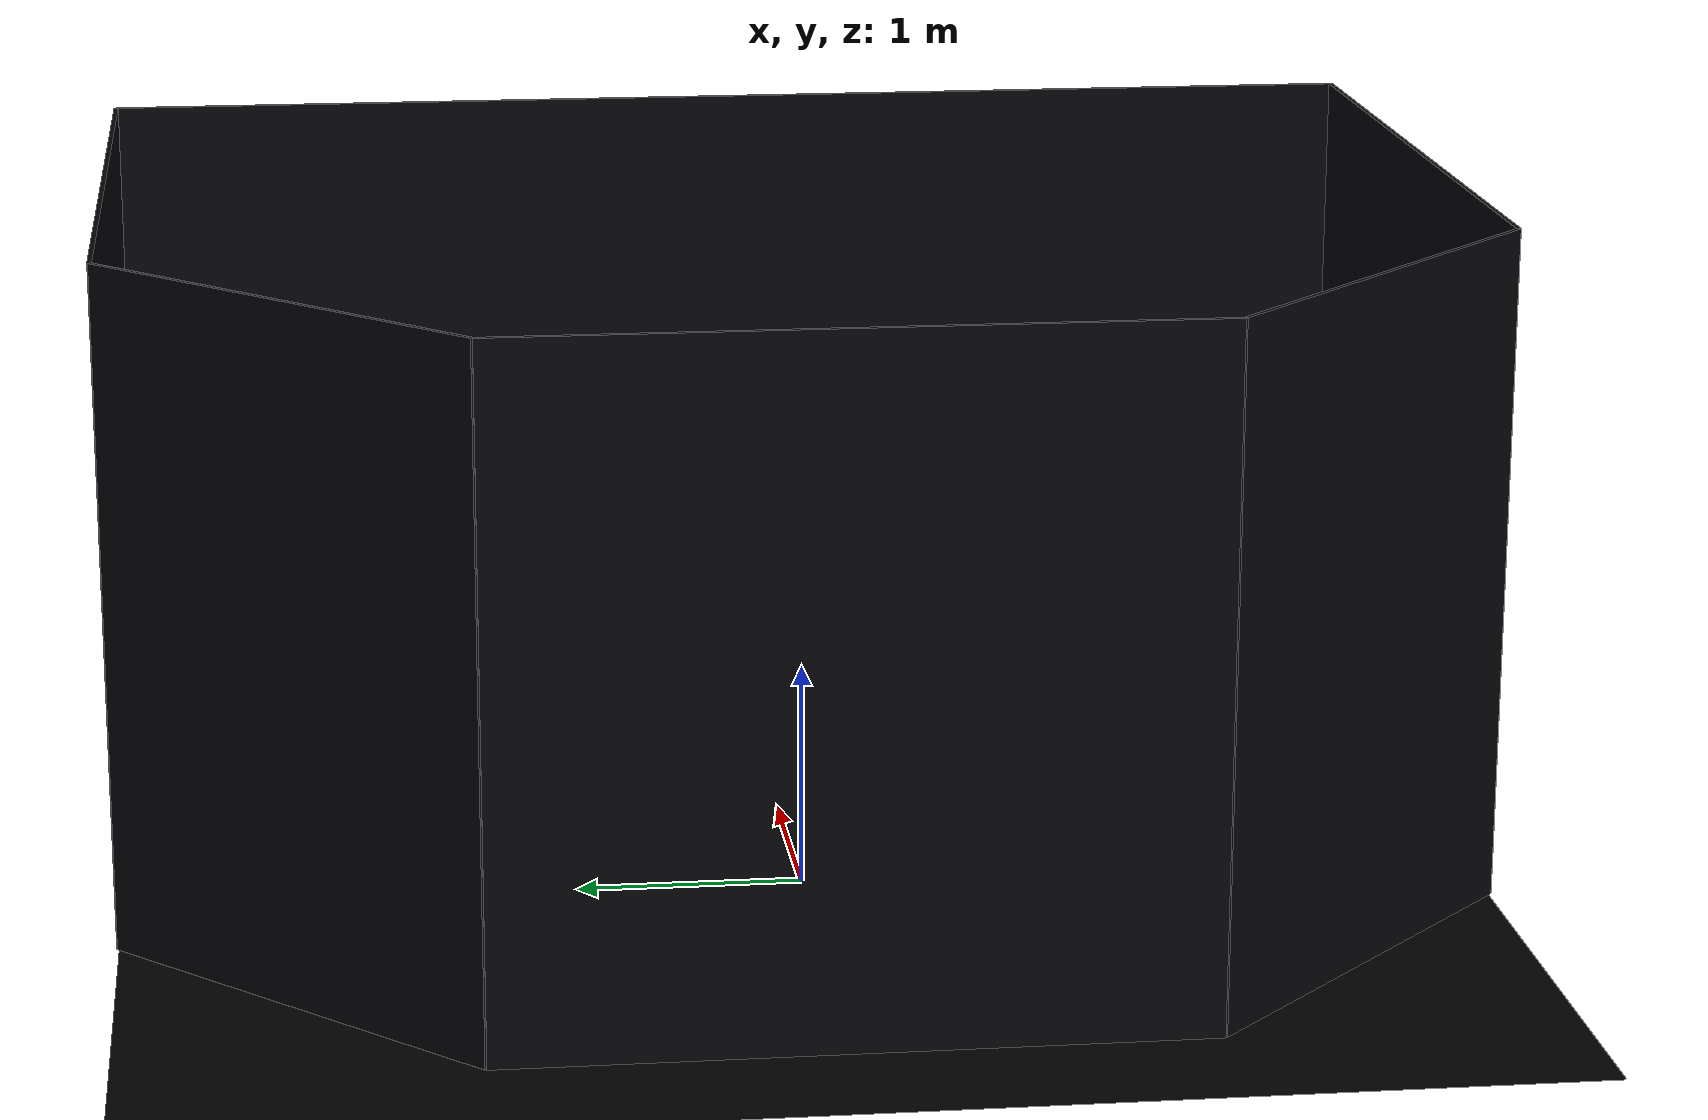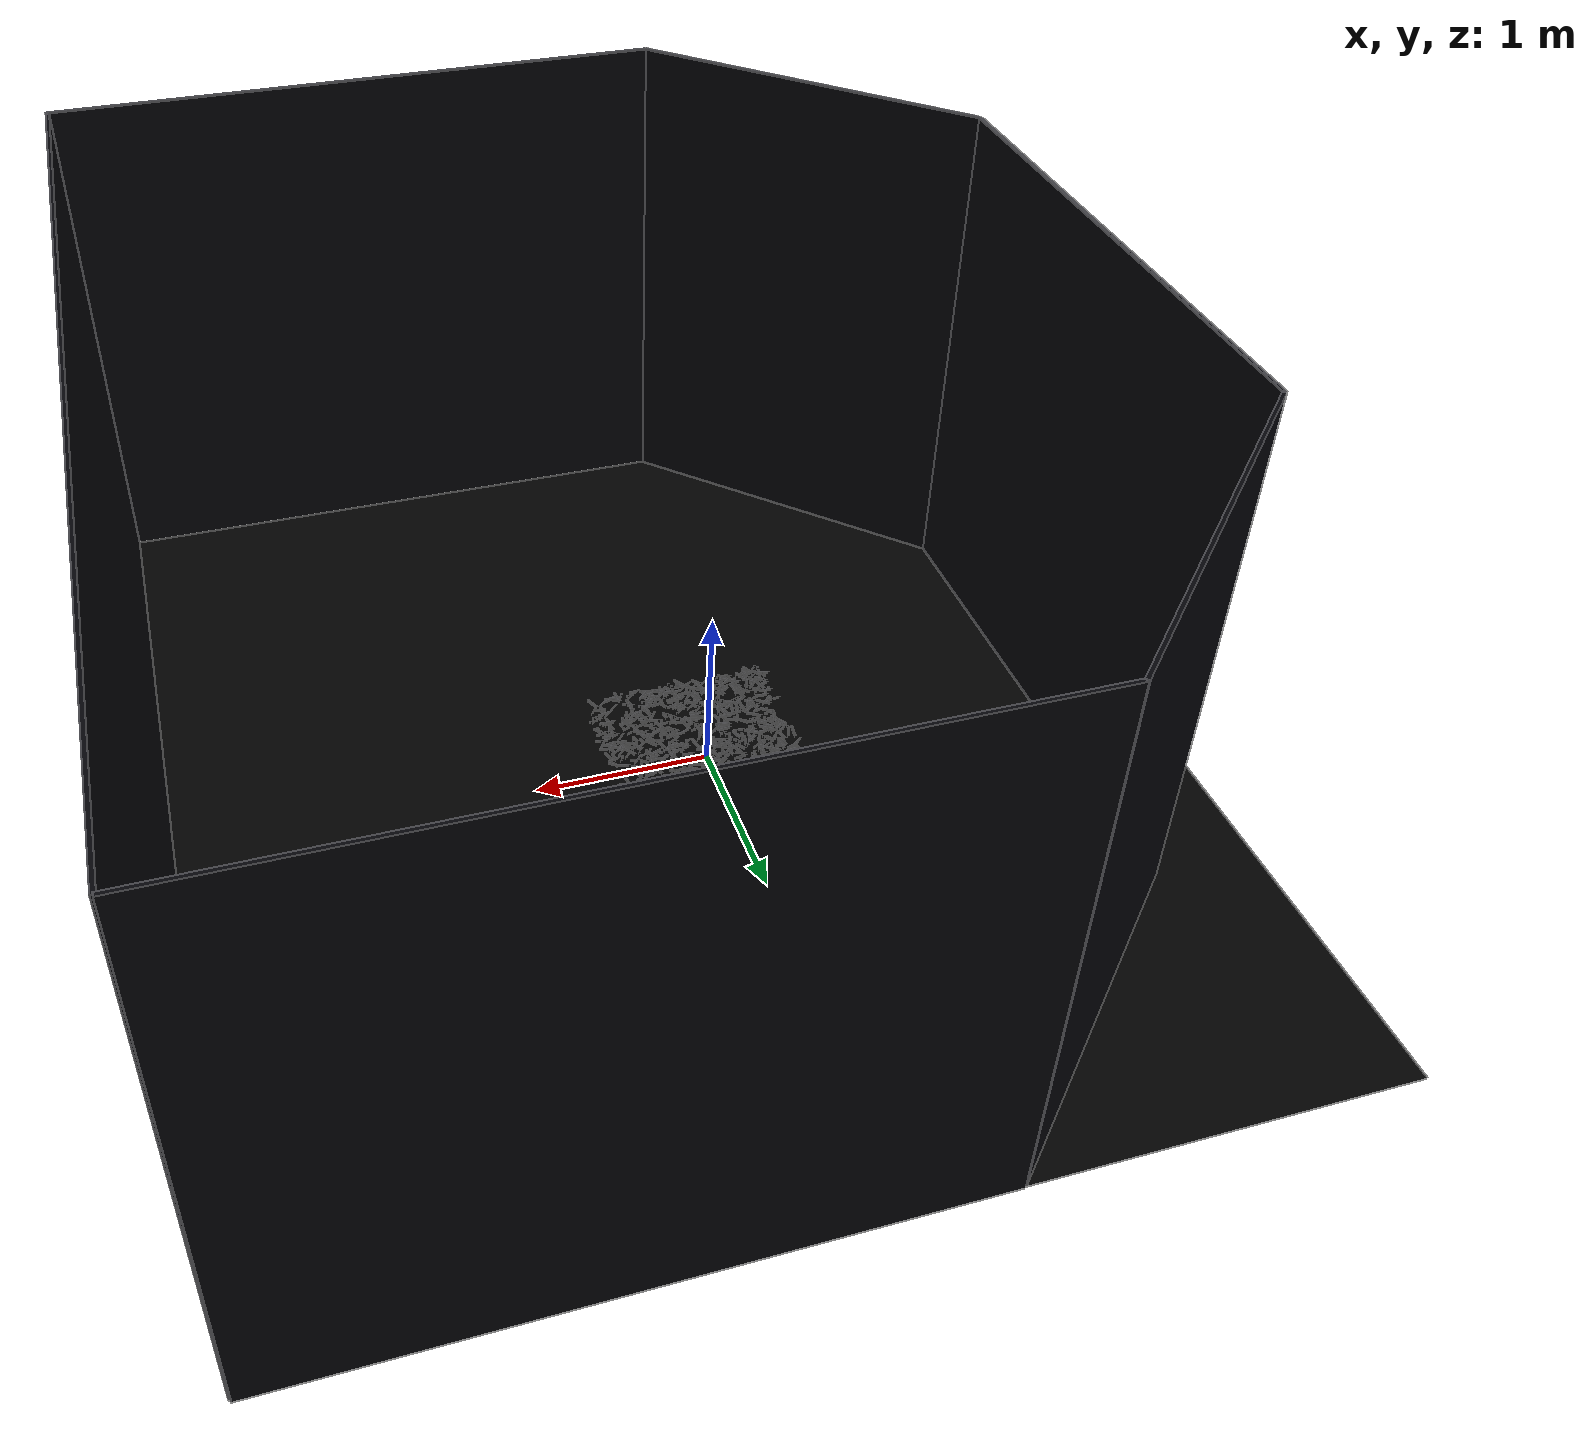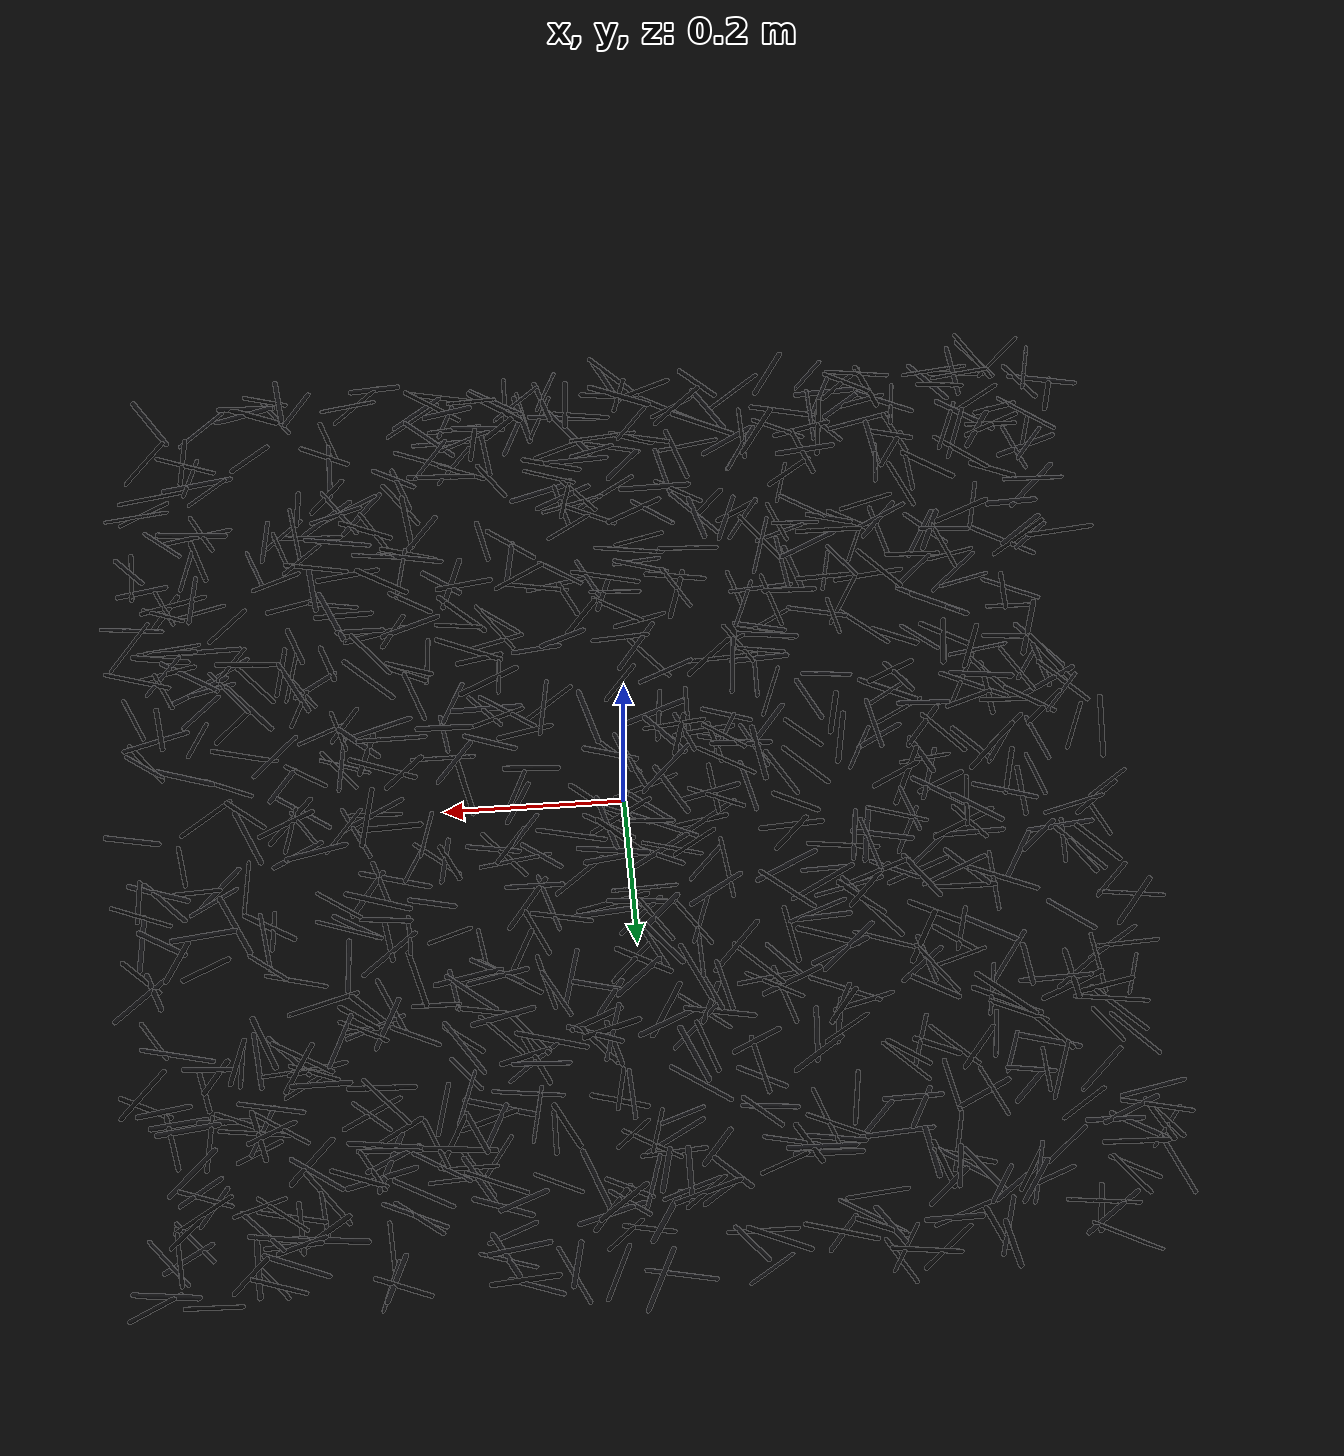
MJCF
<mujoco model="poultry_arena">
  <asset>
    <texture builtin="gradient" height="256" rgb1="0.0 0.0 0.0" rgb2="0.02 0.02 0.05" type="skybox" width="256"/>
    <texture file="../textures/dark_floor_texture.png" type="2d" name="texplane"/>
    <texture file="../textures/dark_blue_wall.png" type="2d" name="tex-wall"/>
    <!-- IR 검은 바닥: flat black (texture 미사용 → EmptyArena의 texplane 덮어쓰기 영향 없음) -->
    <material name="floorplane" rgba="0.0 0.0 0.0 1.0" reflectance="0.0" shininess="0.0" specular="0.0"/>
    <!-- IR 배경 벽: 거의 검정 -->
    <material name="walls_mat" rgba="0.015 0.015 0.030 1.0" reflectance="0.0" shininess="0.0" specular="0.0"/>
    <texture name="textable" builtin="flat" height="512" width="512" rgb1="0.0 0.0 0.0" rgb2="0.0 0.0 0.0"/>
    <material name="table_mat" texture="textable"/>
  </asset>
  <worldbody>
    <body name="floor" pos="0 0 0">
      <!-- contype/conaffinity=5(bit0+bit2): 일반 객체(1)+살아있는 병아리(bit2)와 모두 충돌.
           살아있는 병아리는 바닥하고만 충돌하고 죽은 병아리/바구니와는 안 부딪힘 (배회 시 안 밀어냄). -->
      <geom condim="3" group="1" material="floorplane" name="floor" pos="0 0 0" size="3 3 .125" type="plane" contype="5" conaffinity="5"/>
    <geom name="vstraw_1" type="capsule" size="0.0027 0.0296" pos="0.5016 0.5822 0.0013" quat="0.6541 -0.1937 0.7090 0.1787" rgba="0.033 0.033 0.041 1" contype="0" conaffinity="0" group="1"/>
    <geom name="vstraw_2" type="capsule" size="0.0027 0.0399" pos="0.1165 0.1388 0.0039" quat="0.6265 -0.3347 0.6162 0.3403" rgba="0.018 0.018 0.022 1" contype="0" conaffinity="0" group="1"/>
    <geom name="vstraw_3" type="capsule" size="0.0025 0.0298" pos="0.4943 0.0574 0.0032" quat="0.4960 -0.4976 0.4436 0.5564" rgba="0.001 0.001 0.002 1" contype="0" conaffinity="0" group="1"/>
    <geom name="vstraw_4" type="capsule" size="0.0023 0.0271" pos="-0.1320 0.5093 0.0036" quat="-0.1378 -0.6720 -0.1293 0.7160" rgba="0.001 0.001 0.001 1" contype="0" conaffinity="0" group="1"/>
    <geom name="vstraw_5" type="capsule" size="0.0027 0.0386" pos="0.0112 0.6483 0.0044" quat="0.5661 -0.4000 0.6222 0.3639" rgba="0.036 0.036 0.045 1" contype="0" conaffinity="0" group="1"/>
    <geom name="vstraw_6" type="capsule" size="0.0028 0.0357" pos="0.2892 0.3767 0.0028" quat="-0.6657 -0.0445 -0.7439 0.0398" rgba="0.007 0.007 0.009 1" contype="0" conaffinity="0" group="1"/>
    <geom name="vstraw_7" type="capsule" size="0.0024 0.0382" pos="-0.0425 0.0395 0.0035" quat="-0.6874 -0.1655 -0.6876 0.1654" rgba="0.037 0.037 0.047 1" contype="0" conaffinity="0" group="1"/>
    <geom name="vstraw_8" type="capsule" size="0.0022 0.0299" pos="0.4397 -0.0507 0.0038" quat="-0.6664 -0.1798 -0.7032 0.1704" rgba="0.022 0.022 0.027 1" contype="0" conaffinity="0" group="1"/>
    <geom name="vstraw_9" type="capsule" size="0.0030 0.0356" pos="0.2195 -0.4341 0.0055" quat="0.4469 -0.5531 0.4934 0.5010" rgba="0.014 0.014 0.017 1" contype="0" conaffinity="0" group="1"/>
    <geom name="vstraw_10" type="capsule" size="0.0025 0.0390" pos="0.0047 0.0231 0.0043" quat="-0.1972 -0.6648 -0.1885 0.6955" rgba="0.009 0.009 0.012 1" contype="0" conaffinity="0" group="1"/>
    <geom name="vstraw_11" type="capsule" size="0.0027 0.0259" pos="0.1356 -0.5520 0.0051" quat="-0.4377 -0.5619 -0.4828 0.5094" rgba="0.009 0.009 0.011 1" contype="0" conaffinity="0" group="1"/>
    <geom name="vstraw_12" type="capsule" size="0.0029 0.0287" pos="0.1682 -0.2950 0.0021" quat="-0.6838 -0.2566 -0.6221 0.2820" rgba="0.024 0.024 0.029 1" contype="0" conaffinity="0" group="1"/>
    <geom name="vstraw_13" type="capsule" size="0.0022 0.0351" pos="-0.3185 0.4948 0.0031" quat="-0.4698 -0.5174 -0.4198 0.5791" rgba="0.016 0.016 0.020 1" contype="0" conaffinity="0" group="1"/>
    <geom name="vstraw_14" type="capsule" size="0.0028 0.0274" pos="-0.4588 0.5909 0.0011" quat="-0.4927 -0.4999 -0.4391 0.5609" rgba="0.012 0.012 0.014 1" contype="0" conaffinity="0" group="1"/>
    <geom name="vstraw_15" type="capsule" size="0.0020 0.0302" pos="-0.3479 0.2489 0.0029" quat="0.6582 -0.1010 0.7406 0.0898" rgba="0.007 0.007 0.009 1" contype="0" conaffinity="0" group="1"/>
    <geom name="vstraw_16" type="capsule" size="0.0028 0.0361" pos="0.1268 0.3152 0.0016" quat="0.3650 -0.5810 0.3260 0.6504" rgba="0.020 0.020 0.025 1" contype="0" conaffinity="0" group="1"/>
    <geom name="vstraw_17" type="capsule" size="0.0027 0.0297" pos="0.4422 0.3324 0.0053" quat="-0.4266 -0.5632 -0.4238 0.5668" rgba="0.010 0.010 0.013 1" contype="0" conaffinity="0" group="1"/>
    <geom name="vstraw_18" type="capsule" size="0.0025 0.0272" pos="-0.4377 -0.0678 0.0054" quat="0.6444 -0.2786 0.6577 0.2730" rgba="0.018 0.018 0.022 1" contype="0" conaffinity="0" group="1"/>
    <geom name="vstraw_19" type="capsule" size="0.0021 0.0259" pos="0.5057 -0.3132 0.0040" quat="0.1863 -0.6440 0.1659 0.7232" rgba="0.025 0.025 0.031 1" contype="0" conaffinity="0" group="1"/>
    <geom name="vstraw_20" type="capsule" size="0.0029 0.0399" pos="-0.5131 -0.4405 0.0015" quat="-0.2908 -0.6450 -0.2914 0.6438" rgba="0.044 0.044 0.055 1" contype="0" conaffinity="0" group="1"/>
    <geom name="vstraw_21" type="capsule" size="0.0027 0.0288" pos="-0.2943 -0.0719 0.0023" quat="-0.1969 -0.6883 -0.2029 0.6681" rgba="0.036 0.036 0.045 1" contype="0" conaffinity="0" group="1"/>
    <geom name="vstraw_22" type="capsule" size="0.0027 0.0286" pos="-0.0847 0.0340 0.0010" quat="0.7104 -0.0778 0.6950 0.0796" rgba="0.005 0.005 0.006 1" contype="0" conaffinity="0" group="1"/>
    <geom name="vstraw_23" type="capsule" size="0.0023 0.0346" pos="-0.4402 -0.4137 0.0022" quat="0.5472 -0.4473 0.5499 0.4451" rgba="0.021 0.021 0.026 1" contype="0" conaffinity="0" group="1"/>
    <geom name="vstraw_24" type="capsule" size="0.0026 0.0258" pos="-0.3163 0.5285 0.0058" quat="-0.4695 -0.5277 -0.4621 0.5362" rgba="0.023 0.023 0.029 1" contype="0" conaffinity="0" group="1"/>
    <geom name="vstraw_25" type="capsule" size="0.0025 0.0388" pos="-0.0902 0.0326 0.0019" quat="0.6516 -0.2127 0.7008 0.1977" rgba="0.016 0.016 0.021 1" contype="0" conaffinity="0" group="1"/>
    <geom name="vstraw_26" type="capsule" size="0.0021 0.0296" pos="0.1216 -0.2735 0.0059" quat="0.2918 -0.6123 0.2599 0.6874" rgba="0.031 0.031 0.039 1" contype="0" conaffinity="0" group="1"/>
    <geom name="vstraw_27" type="capsule" size="0.0022 0.0338" pos="0.3747 0.2243 0.0011" quat="0.1086 -0.6914 0.1063 0.7063" rgba="0.022 0.022 0.027 1" contype="0" conaffinity="0" group="1"/>
    <geom name="vstraw_28" type="capsule" size="0.0022 0.0336" pos="-0.4688 -0.2803 0.0029" quat="-0.7268 -0.1354 -0.6565 0.1499" rgba="0.034 0.034 0.042 1" contype="0" conaffinity="0" group="1"/>
    <geom name="vstraw_29" type="capsule" size="0.0021 0.0378" pos="-0.1190 -0.0478 0.0048" quat="0.2391 -0.6380 0.2183 0.6987" rgba="0.005 0.005 0.007 1" contype="0" conaffinity="0" group="1"/>
    <geom name="vstraw_30" type="capsule" size="0.0027 0.0325" pos="0.1551 0.5976 0.0045" quat="0.6914 -0.0558 0.7183 0.0537" rgba="0.035 0.035 0.044 1" contype="0" conaffinity="0" group="1"/>
    <geom name="vstraw_31" type="capsule" size="0.0030 0.0371" pos="-0.1567 -0.0559 0.0050" quat="0.4679 -0.5305 0.4709 0.5272" rgba="0.021 0.021 0.027 1" contype="0" conaffinity="0" group="1"/>
    <geom name="vstraw_32" type="capsule" size="0.0024 0.0352" pos="0.4753 0.4368 0.0025" quat="0.5287 -0.4697 0.5273 0.4710" rgba="0.012 0.012 0.015 1" contype="0" conaffinity="0" group="1"/>
    <geom name="vstraw_33" type="capsule" size="0.0021 0.0313" pos="0.4604 0.1117 0.0051" quat="0.6868 -0.2063 0.6635 0.2135" rgba="0.045 0.045 0.056 1" contype="0" conaffinity="0" group="1"/>
    <geom name="vstraw_34" type="capsule" size="0.0023 0.0285" pos="-0.4765 -0.5380 0.0055" quat="-0.6940 -0.0257 -0.7191 0.0248" rgba="0.006 0.006 0.007 1" contype="0" conaffinity="0" group="1"/>
    <geom name="vstraw_35" type="capsule" size="0.0029 0.0363" pos="0.1878 0.2354 0.0032" quat="-0.0557 -0.6715 -0.0507 0.7371" rgba="0.024 0.024 0.030 1" contype="0" conaffinity="0" group="1"/>
    <geom name="vstraw_36" type="capsule" size="0.0027 0.0311" pos="-0.4442 0.0215 0.0046" quat="0.4648 -0.5349 0.5111 0.4865" rgba="0.021 0.021 0.026 1" contype="0" conaffinity="0" group="1"/>
    <geom name="vstraw_37" type="capsule" size="0.0026 0.0382" pos="0.5446 0.3677 0.0039" quat="0.6397 -0.3084 0.6307 0.3128" rgba="0.001 0.001 0.002 1" contype="0" conaffinity="0" group="1"/>
    <geom name="vstraw_38" type="capsule" size="0.0027 0.0321" pos="-0.3515 0.0132 0.0034" quat="0.2028 -0.6926 0.2133 0.6585" rgba="0.042 0.042 0.053 1" contype="0" conaffinity="0" group="1"/>
    <geom name="vstraw_39" type="capsule" size="0.0022 0.0343" pos="0.5082 -0.2201 0.0047" quat="-0.3269 -0.6405 -0.3481 0.6015" rgba="0.038 0.038 0.048 1" contype="0" conaffinity="0" group="1"/>
    <geom name="vstraw_40" type="capsule" size="0.0027 0.0382" pos="-0.1070 0.2171 0.0059" quat="-0.3072 -0.6057 -0.2731 0.6813" rgba="0.021 0.021 0.026 1" contype="0" conaffinity="0" group="1"/>
    <geom name="vstraw_41" type="capsule" size="0.0029 0.0383" pos="0.1651 0.4109 0.0011" quat="-0.6765 -0.1289 -0.7148 0.1219" rgba="0.027 0.027 0.034 1" contype="0" conaffinity="0" group="1"/>
    <geom name="vstraw_42" type="capsule" size="0.0022 0.0371" pos="-0.4395 0.4103 0.0048" quat="0.5556 -0.4268 0.5892 0.4025" rgba="0.026 0.026 0.033 1" contype="0" conaffinity="0" group="1"/>
    <geom name="vstraw_43" type="capsule" size="0.0022 0.0395" pos="-0.3983 0.1460 0.0032" quat="0.4902 -0.5098 0.4981 0.5017" rgba="0.021 0.021 0.026 1" contype="0" conaffinity="0" group="1"/>
    <geom name="vstraw_44" type="capsule" size="0.0025 0.0351" pos="-0.4699 -0.6461 0.0034" quat="-0.6048 -0.3526 -0.6282 0.3395" rgba="0.034 0.034 0.042 1" contype="0" conaffinity="0" group="1"/>
    <geom name="vstraw_45" type="capsule" size="0.0022 0.0363" pos="-0.1816 -0.3030 0.0035" quat="0.7391 -0.0579 0.6681 0.0641" rgba="0.034 0.034 0.042 1" contype="0" conaffinity="0" group="1"/>
    <geom name="vstraw_46" type="capsule" size="0.0022 0.0307" pos="0.3128 -0.1242 0.0044" quat="-0.5304 -0.4566 -0.5789 0.4184" rgba="0.006 0.006 0.008 1" contype="0" conaffinity="0" group="1"/>
    <geom name="vstraw_47" type="capsule" size="0.0025 0.0307" pos="-0.0389 -0.2667 0.0011" quat="-0.1196 -0.7335 -0.1338 0.6556" rgba="0.016 0.016 0.021 1" contype="0" conaffinity="0" group="1"/>
    <geom name="vstraw_48" type="capsule" size="0.0029 0.0262" pos="-0.0629 0.4816 0.0025" quat="-0.3198 -0.6297 -0.3185 0.6322" rgba="0.024 0.024 0.030 1" contype="0" conaffinity="0" group="1"/>
    <geom name="vstraw_49" type="capsule" size="0.0028 0.0264" pos="0.3568 -0.2546 0.0042" quat="-0.5561 -0.4308 -0.5769 0.4152" rgba="0.018 0.018 0.022 1" contype="0" conaffinity="0" group="1"/>
    <geom name="vstraw_50" type="capsule" size="0.0023 0.0285" pos="0.1466 -0.1415 0.0037" quat="-0.6080 -0.3304 -0.6531 0.3075" rgba="0.028 0.028 0.035 1" contype="0" conaffinity="0" group="1"/>
    <geom name="vstraw_51" type="capsule" size="0.0024 0.0305" pos="-0.0467 -0.3483 0.0024" quat="-0.7328 -0.0891 -0.6675 0.0978" rgba="0.037 0.037 0.046 1" contype="0" conaffinity="0" group="1"/>
    <geom name="vstraw_52" type="capsule" size="0.0029 0.0388" pos="-0.1998 -0.5494 0.0033" quat="0.6168 -0.3508 0.6083 0.3557" rgba="0.013 0.013 0.016 1" contype="0" conaffinity="0" group="1"/>
    <geom name="vstraw_53" type="capsule" size="0.0022 0.0352" pos="-0.0638 0.1815 0.0056" quat="0.3843 -0.5746 0.3491 0.6327" rgba="0.011 0.011 0.013 1" contype="0" conaffinity="0" group="1"/>
    <geom name="vstraw_54" type="capsule" size="0.0024 0.0374" pos="-0.1388 -0.1871 0.0050" quat="0.5059 -0.4901 0.5448 0.4551" rgba="0.028 0.028 0.036 1" contype="0" conaffinity="0" group="1"/>
    <geom name="vstraw_55" type="capsule" size="0.0027 0.0363" pos="-0.1735 0.4922 0.0056" quat="-0.0057 -0.7230 -0.0059 0.6908" rgba="0.043 0.043 0.053 1" contype="0" conaffinity="0" group="1"/>
    <geom name="vstraw_56" type="capsule" size="0.0027 0.0305" pos="0.4062 0.5662 0.0048" quat="-0.7230 -0.0453 -0.6877 0.0476" rgba="0.028 0.028 0.035 1" contype="0" conaffinity="0" group="1"/>
    <geom name="vstraw_57" type="capsule" size="0.0022 0.0394" pos="-0.1153 -0.4228 0.0058" quat="0.3139 -0.6322 0.3122 0.6358" rgba="0.040 0.040 0.050 1" contype="0" conaffinity="0" group="1"/>
    <geom name="vstraw_58" type="capsule" size="0.0028 0.0315" pos="-0.4102 -0.6136 0.0028" quat="0.2872 -0.6702 0.3175 0.6062" rgba="0.040 0.040 0.050 1" contype="0" conaffinity="0" group="1"/>
    <geom name="vstraw_59" type="capsule" size="0.0022 0.0297" pos="0.0470 -0.3422 0.0052" quat="0.2458 -0.6478 0.2334 0.6822" rgba="0.029 0.029 0.036 1" contype="0" conaffinity="0" group="1"/>
    <geom name="vstraw_60" type="capsule" size="0.0023 0.0301" pos="0.4688 -0.5264 0.0017" quat="0.5830 -0.4106 0.5492 0.4359" rgba="0.019 0.019 0.024 1" contype="0" conaffinity="0" group="1"/>
    <geom name="vstraw_61" type="capsule" size="0.0021 0.0272" pos="-0.2789 -0.3379 0.0041" quat="0.3528 -0.6063 0.3422 0.6251" rgba="0.035 0.035 0.043 1" contype="0" conaffinity="0" group="1"/>
    <geom name="vstraw_62" type="capsule" size="0.0023 0.0365" pos="0.3859 -0.0913 0.0049" quat="0.6447 -0.2873 0.6482 0.2857" rgba="0.038 0.038 0.048 1" contype="0" conaffinity="0" group="1"/>
    <geom name="vstraw_63" type="capsule" size="0.0023 0.0376" pos="0.1214 -0.1371 0.0060" quat="0.2354 -0.6649 0.2340 0.6691" rgba="0.028 0.028 0.035 1" contype="0" conaffinity="0" group="1"/>
    <geom name="vstraw_64" type="capsule" size="0.0025 0.0312" pos="0.1073 0.1144 0.0037" quat="-0.6637 -0.0354 -0.7465 0.0314" rgba="0.038 0.038 0.047 1" contype="0" conaffinity="0" group="1"/>
    <geom name="vstraw_65" type="capsule" size="0.0027 0.0387" pos="0.0272 -0.5900 0.0015" quat="-0.7379 -0.0101 -0.6748 0.0110" rgba="0.042 0.042 0.053 1" contype="0" conaffinity="0" group="1"/>
    <geom name="vstraw_66" type="capsule" size="0.0022 0.0272" pos="-0.4649 -0.2524 0.0050" quat="0.7395 -0.0187 0.6726 0.0206" rgba="0.016 0.016 0.020 1" contype="0" conaffinity="0" group="1"/>
    <geom name="vstraw_67" type="capsule" size="0.0022 0.0322" pos="0.1867 -0.5305 0.0059" quat="-0.3366 -0.5957 -0.3020 0.6638" rgba="0.040 0.040 0.051 1" contype="0" conaffinity="0" group="1"/>
    <geom name="vstraw_68" type="capsule" size="0.0028 0.0328" pos="0.0646 -0.4698 0.0035" quat="0.7190 -0.1283 0.6690 0.1379" rgba="0.041 0.041 0.052 1" contype="0" conaffinity="0" group="1"/>
    <geom name="vstraw_69" type="capsule" size="0.0021 0.0282" pos="0.2000 0.4882 0.0017" quat="0.0183 -0.6750 0.0167 0.7374" rgba="0.005 0.005 0.007 1" contype="0" conaffinity="0" group="1"/>
    <geom name="vstraw_70" type="capsule" size="0.0027 0.0326" pos="-0.4915 -0.3702 0.0029" quat="-0.2542 -0.6828 -0.2770 0.6264" rgba="0.041 0.041 0.051 1" contype="0" conaffinity="0" group="1"/>
    <geom name="vstraw_71" type="capsule" size="0.0024 0.0295" pos="0.4587 -0.4381 0.0015" quat="-0.5853 -0.3888 -0.6034 0.3771" rgba="0.009 0.009 0.012 1" contype="0" conaffinity="0" group="1"/>
    <geom name="vstraw_72" type="capsule" size="0.0025 0.0293" pos="-0.0761 -0.0940 0.0030" quat="-0.5474 -0.4351 -0.5900 0.4037" rgba="0.025 0.025 0.032 1" contype="0" conaffinity="0" group="1"/>
    <geom name="vstraw_73" type="capsule" size="0.0020 0.0333" pos="0.2919 0.6330 0.0021" quat="-0.4110 -0.5814 -0.4311 0.5543" rgba="0.030 0.030 0.037 1" contype="0" conaffinity="0" group="1"/>
    <geom name="vstraw_74" type="capsule" size="0.0027 0.0321" pos="-0.3278 -0.3974 0.0039" quat="-0.3065 -0.6444 -0.3159 0.6253" rgba="0.033 0.033 0.042 1" contype="0" conaffinity="0" group="1"/>
    <geom name="vstraw_75" type="capsule" size="0.0022 0.0266" pos="-0.4974 0.3539 0.0051" quat="-0.6075 -0.3535 -0.6219 0.3453" rgba="0.002 0.002 0.002 1" contype="0" conaffinity="0" group="1"/>
    <geom name="vstraw_76" type="capsule" size="0.0025 0.0294" pos="0.1494 0.0576 0.0019" quat="-0.6590 -0.1033 -0.7393 0.0921" rgba="0.040 0.040 0.051 1" contype="0" conaffinity="0" group="1"/>
    <geom name="vstraw_77" type="capsule" size="0.0024 0.0312" pos="-0.3202 0.4214 0.0045" quat="0.4328 -0.5665 0.4767 0.5143" rgba="0.026 0.026 0.032 1" contype="0" conaffinity="0" group="1"/>
    <geom name="vstraw_78" type="capsule" size="0.0029 0.0282" pos="0.2425 -0.0580 0.0043" quat="0.6397 -0.2708 0.6715 0.2580" rgba="0.012 0.012 0.015 1" contype="0" conaffinity="0" group="1"/>
    <geom name="vstraw_79" type="capsule" size="0.0028 0.0354" pos="-0.1835 0.0494 0.0030" quat="-0.0535 -0.7398 -0.0593 0.6681" rgba="0.009 0.009 0.011 1" contype="0" conaffinity="0" group="1"/>
    <geom name="vstraw_80" type="capsule" size="0.0022 0.0321" pos="0.3149 -0.0680 0.0033" quat="0.3303 -0.6238 0.3281 0.6278" rgba="0.011 0.011 0.014 1" contype="0" conaffinity="0" group="1"/>
    <geom name="vstraw_81" type="capsule" size="0.0029 0.0283" pos="-0.3387 -0.0398 0.0039" quat="0.4139 -0.5606 0.3824 0.6068" rgba="0.027 0.027 0.034 1" contype="0" conaffinity="0" group="1"/>
    <geom name="vstraw_82" type="capsule" size="0.0028 0.0295" pos="0.1273 0.2063 0.0054" quat="-0.3916 -0.5806 -0.3740 0.6080" rgba="0.009 0.009 0.012 1" contype="0" conaffinity="0" group="1"/>
    <geom name="vstraw_83" type="capsule" size="0.0027 0.0301" pos="-0.5361 0.4816 0.0020" quat="0.4002 -0.5757 0.3832 0.6013" rgba="0.012 0.012 0.014 1" contype="0" conaffinity="0" group="1"/>
    <geom name="vstraw_84" type="capsule" size="0.0022 0.0341" pos="-0.0654 -0.1048 0.0052" quat="0.6992 -0.0409 0.7127 0.0401" rgba="0.006 0.006 0.007 1" contype="0" conaffinity="0" group="1"/>
    <geom name="vstraw_85" type="capsule" size="0.0028 0.0387" pos="-0.1367 -0.5657 0.0039" quat="-0.6697 -0.1912 -0.6934 0.1846" rgba="0.022 0.022 0.028 1" contype="0" conaffinity="0" group="1"/>
    <geom name="vstraw_86" type="capsule" size="0.0029 0.0339" pos="-0.3836 -0.2609 0.0058" quat="-0.7122 -0.1571 -0.6631 0.1687" rgba="0.032 0.032 0.040 1" contype="0" conaffinity="0" group="1"/>
    <geom name="vstraw_87" type="capsule" size="0.0021 0.0343" pos="0.2224 0.0312 0.0022" quat="0.5829 -0.4151 0.5246 0.4612" rgba="0.030 0.030 0.037 1" contype="0" conaffinity="0" group="1"/>
    <geom name="vstraw_88" type="capsule" size="0.0022 0.0284" pos="-0.1196 -0.0830 0.0059" quat="0.2365 -0.6646 0.2350 0.6687" rgba="0.017 0.017 0.021 1" contype="0" conaffinity="0" group="1"/>
    <geom name="vstraw_89" type="capsule" size="0.0027 0.0310" pos="0.0359 0.4126 0.0015" quat="-0.6821 -0.1227 -0.7113 0.1176" rgba="0.002 0.002 0.003 1" contype="0" conaffinity="0" group="1"/>
    <geom name="vstraw_90" type="capsule" size="0.0027 0.0360" pos="0.0161 -0.5187 0.0036" quat="-0.0427 -0.7292 -0.0457 0.6814" rgba="0.026 0.026 0.033 1" contype="0" conaffinity="0" group="1"/>
    <geom name="vstraw_91" type="capsule" size="0.0025 0.0342" pos="-0.3067 -0.6178 0.0034" quat="0.6769 -0.2672 0.6210 0.2912" rgba="0.014 0.014 0.018 1" contype="0" conaffinity="0" group="1"/>
    <geom name="vstraw_92" type="capsule" size="0.0024 0.0271" pos="0.1610 0.5754 0.0015" quat="-0.1342 -0.6601 -0.1215 0.7290" rgba="0.030 0.030 0.038 1" contype="0" conaffinity="0" group="1"/>
    <geom name="vstraw_93" type="capsule" size="0.0029 0.0341" pos="-0.2084 0.2087 0.0034" quat="-0.7083 -0.1207 -0.6841 0.1250" rgba="0.015 0.015 0.019 1" contype="0" conaffinity="0" group="1"/>
    <geom name="vstraw_94" type="capsule" size="0.0029 0.0326" pos="-0.4323 0.3695 0.0028" quat="-0.6860 -0.1180 -0.7088 0.1142" rgba="0.036 0.036 0.045 1" contype="0" conaffinity="0" group="1"/>
    <geom name="vstraw_95" type="capsule" size="0.0030 0.0357" pos="0.5140 -0.6167 0.0027" quat="-0.6526 -0.3240 -0.5798 0.3647" rgba="0.030 0.030 0.038 1" contype="0" conaffinity="0" group="1"/>
    <geom name="vstraw_96" type="capsule" size="0.0028 0.0274" pos="0.3984 -0.5503 0.0037" quat="-0.2406 -0.6604 -0.2369 0.6707" rgba="0.019 0.019 0.024 1" contype="0" conaffinity="0" group="1"/>
    <geom name="vstraw_97" type="capsule" size="0.0029 0.0256" pos="-0.5005 0.1210 0.0058" quat="-0.5927 -0.3729 -0.6178 0.3577" rgba="0.013 0.013 0.017 1" contype="0" conaffinity="0" group="1"/>
    <geom name="vstraw_98" type="capsule" size="0.0026 0.0260" pos="-0.2787 0.3745 0.0055" quat="0.2018 -0.7067 0.2227 0.6405" rgba="0.005 0.005 0.006 1" contype="0" conaffinity="0" group="1"/>
    <geom name="vstraw_99" type="capsule" size="0.0027 0.0258" pos="-0.2933 -0.4031 0.0010" quat="0.2073 -0.6761 0.2073 0.6760" rgba="0.013 0.013 0.016 1" contype="0" conaffinity="0" group="1"/>
    <geom name="vstraw_100" type="capsule" size="0.0025 0.0306" pos="0.0192 0.0361 0.0030" quat="-0.7118 -0.1784 -0.6507 0.1952" rgba="0.019 0.019 0.024 1" contype="0" conaffinity="0" group="1"/>
    <geom name="vstraw_101" type="capsule" size="0.0028 0.0347" pos="0.5211 0.0934 0.0036" quat="0.1335 -0.6893 0.1315 0.6998" rgba="0.043 0.043 0.053 1" contype="0" conaffinity="0" group="1"/>
    <geom name="vstraw_102" type="capsule" size="0.0030 0.0346" pos="-0.3714 0.1229 0.0016" quat="0.3369 -0.5939 0.3004 0.6661" rgba="0.032 0.032 0.040 1" contype="0" conaffinity="0" group="1"/>
    <geom name="vstraw_103" type="capsule" size="0.0022 0.0363" pos="0.0768 -0.3245 0.0032" quat="0.0796 -0.6962 0.0781 0.7092" rgba="0.012 0.012 0.015 1" contype="0" conaffinity="0" group="1"/>
    <geom name="vstraw_104" type="capsule" size="0.0030 0.0332" pos="0.4977 0.4176 0.0041" quat="0.7209 -0.0604 0.6875 0.0634" rgba="0.038 0.038 0.047 1" contype="0" conaffinity="0" group="1"/>
    <geom name="vstraw_105" type="capsule" size="0.0025 0.0350" pos="0.0758 0.2423 0.0022" quat="-0.4441 -0.5467 -0.4300 0.5647" rgba="0.038 0.038 0.048 1" contype="0" conaffinity="0" group="1"/>
    <geom name="vstraw_106" type="capsule" size="0.0025 0.0385" pos="0.0617 0.0451 0.0033" quat="-0.6774 -0.1090 -0.7202 0.1025" rgba="0.019 0.019 0.024 1" contype="0" conaffinity="0" group="1"/>
    <geom name="vstraw_107" type="capsule" size="0.0025 0.0394" pos="0.2717 0.1990 0.0058" quat="0.6519 -0.2574 0.6675 0.2514" rgba="0.028 0.028 0.035 1" contype="0" conaffinity="0" group="1"/>
    <geom name="vstraw_108" type="capsule" size="0.0028 0.0302" pos="0.5142 -0.1423 0.0041" quat="-0.5116 -0.4857 -0.5363 0.4634" rgba="0.016 0.016 0.020 1" contype="0" conaffinity="0" group="1"/>
    <geom name="vstraw_109" type="capsule" size="0.0028 0.0311" pos="-0.3884 0.2139 0.0042" quat="0.2005 -0.6780 0.2004 0.6782" rgba="0.044 0.044 0.056 1" contype="0" conaffinity="0" group="1"/>
    <geom name="vstraw_110" type="capsule" size="0.0027 0.0350" pos="0.4529 0.0914 0.0030" quat="-0.3039 -0.6544 -0.3253 0.6113" rgba="0.040 0.040 0.050 1" contype="0" conaffinity="0" group="1"/>
    <geom name="vstraw_111" type="capsule" size="0.0026 0.0360" pos="-0.1091 -0.5976 0.0033" quat="0.6260 -0.2613 0.6962 0.2350" rgba="0.016 0.016 0.020 1" contype="0" conaffinity="0" group="1"/>
    <geom name="vstraw_112" type="capsule" size="0.0029 0.0317" pos="-0.3535 0.4336 0.0026" quat="0.6764 -0.1789 0.6928 0.1747" rgba="0.018 0.018 0.023 1" contype="0" conaffinity="0" group="1"/>
    <geom name="vstraw_113" type="capsule" size="0.0023 0.0322" pos="-0.4461 -0.6260 0.0012" quat="0.0141 -0.7249 0.0149 0.6886" rgba="0.002 0.002 0.003 1" contype="0" conaffinity="0" group="1"/>
    <geom name="vstraw_114" type="capsule" size="0.0026 0.0275" pos="0.4373 0.6118 0.0054" quat="-0.2961 -0.6466 -0.3015 0.6351" rgba="0.010 0.010 0.013 1" contype="0" conaffinity="0" group="1"/>
    <geom name="vstraw_115" type="capsule" size="0.0025 0.0336" pos="-0.2165 0.4293 0.0038" quat="-0.4632 -0.5337 -0.4593 0.5382" rgba="0.013 0.013 0.016 1" contype="0" conaffinity="0" group="1"/>
    <geom name="vstraw_116" type="capsule" size="0.0027 0.0284" pos="-0.2841 0.4491 0.0059" quat="0.6137 -0.3692 0.5769 0.3928" rgba="0.037 0.037 0.046 1" contype="0" conaffinity="0" group="1"/>
    <geom name="vstraw_117" type="capsule" size="0.0024 0.0321" pos="0.0946 -0.3404 0.0053" quat="-0.1916 -0.6815 -0.1921 0.6797" rgba="0.007 0.007 0.009 1" contype="0" conaffinity="0" group="1"/>
    <geom name="vstraw_118" type="capsule" size="0.0026 0.0369" pos="-0.1520 -0.4162 0.0020" quat="-0.3943 -0.6002 -0.4367 0.5419" rgba="0.038 0.038 0.047 1" contype="0" conaffinity="0" group="1"/>
    <geom name="vstraw_119" type="capsule" size="0.0022 0.0278" pos="-0.4030 -0.3770 0.0045" quat="0.7415 -0.0031 0.6709 0.0034" rgba="0.035 0.035 0.044 1" contype="0" conaffinity="0" group="1"/>
    <geom name="vstraw_120" type="capsule" size="0.0025 0.0268" pos="-0.1150 0.4379 0.0011" quat="-0.6705 -0.2592 -0.6398 0.2716" rgba="0.026 0.026 0.032 1" contype="0" conaffinity="0" group="1"/>
    <geom name="vstraw_121" type="capsule" size="0.0021 0.0272" pos="0.5042 -0.4214 0.0050" quat="-0.6602 -0.2610 -0.6530 0.2639" rgba="0.043 0.043 0.054 1" contype="0" conaffinity="0" group="1"/>
    <geom name="vstraw_122" type="capsule" size="0.0020 0.0384" pos="-0.0179 -0.5529 0.0050" quat="-0.0568 -0.7295 -0.0610 0.6789" rgba="0.013 0.013 0.016 1" contype="0" conaffinity="0" group="1"/>
    <geom name="vstraw_123" type="capsule" size="0.0020 0.0301" pos="-0.3208 -0.1079 0.0016" quat="-0.1914 -0.6780 -0.1897 0.6839" rgba="0.009 0.009 0.011 1" contype="0" conaffinity="0" group="1"/>
    <geom name="vstraw_124" type="capsule" size="0.0026 0.0377" pos="0.3119 -0.4498 0.0021" quat="-0.2533 -0.6692 -0.2616 0.6478" rgba="0.036 0.036 0.045 1" contype="0" conaffinity="0" group="1"/>
    <geom name="vstraw_125" type="capsule" size="0.0025 0.0388" pos="-0.3791 0.5486 0.0011" quat="0.6888 -0.2456 0.6262 0.2702" rgba="0.035 0.035 0.044 1" contype="0" conaffinity="0" group="1"/>
    <geom name="vstraw_126" type="capsule" size="0.0022 0.0333" pos="0.5223 0.5879 0.0041" quat="0.3004 -0.6651 0.3353 0.5958" rgba="0.033 0.033 0.041 1" contype="0" conaffinity="0" group="1"/>
    <geom name="vstraw_127" type="capsule" size="0.0021 0.0361" pos="-0.5276 -0.6273 0.0042" quat="-0.4298 -0.5688 -0.4687 0.5216" rgba="0.034 0.034 0.042 1" contype="0" conaffinity="0" group="1"/>
    <geom name="vstraw_128" type="capsule" size="0.0030 0.0267" pos="0.5293 0.2299 0.0034" quat="0.4463 -0.5350 0.4019 0.5942" rgba="0.028 0.028 0.035 1" contype="0" conaffinity="0" group="1"/>
    <geom name="vstraw_129" type="capsule" size="0.0026 0.0382" pos="0.3529 0.5171 0.0028" quat="-0.6511 -0.3153 -0.5994 0.3425" rgba="0.014 0.014 0.017 1" contype="0" conaffinity="0" group="1"/>
    <geom name="vstraw_130" type="capsule" size="0.0023 0.0264" pos="0.0393 -0.5339 0.0056" quat="-0.1523 -0.7120 -0.1629 0.6658" rgba="0.010 0.010 0.013 1" contype="0" conaffinity="0" group="1"/>
    <geom name="vstraw_131" type="capsule" size="0.0029 0.0348" pos="-0.3446 -0.0818 0.0031" quat="-0.3207 -0.6475 -0.3475 0.5976" rgba="0.015 0.015 0.019 1" contype="0" conaffinity="0" group="1"/>
    <geom name="vstraw_132" type="capsule" size="0.0024 0.0313" pos="-0.1707 -0.4098 0.0058" quat="-0.3522 -0.5880 -0.3155 0.6563" rgba="0.031 0.031 0.039 1" contype="0" conaffinity="0" group="1"/>
    <geom name="vstraw_133" type="capsule" size="0.0028 0.0358" pos="0.2921 -0.3599 0.0023" quat="-0.0848 -0.7347 -0.0935 0.6666" rgba="0.004 0.004 0.005 1" contype="0" conaffinity="0" group="1"/>
    <geom name="vstraw_134" type="capsule" size="0.0025 0.0286" pos="-0.3550 0.2103 0.0041" quat="-0.4309 -0.5616 -0.4348 0.5567" rgba="0.014 0.014 0.018 1" contype="0" conaffinity="0" group="1"/>
    <geom name="vstraw_135" type="capsule" size="0.0026 0.0362" pos="-0.0491 -0.1221 0.0015" quat="0.5371 -0.4622 0.5174 0.4798" rgba="0.018 0.018 0.022 1" contype="0" conaffinity="0" group="1"/>
    <geom name="vstraw_136" type="capsule" size="0.0029 0.0375" pos="-0.2650 0.0711 0.0027" quat="0.5579 -0.4416 0.5117 0.4816" rgba="0.043 0.043 0.054 1" contype="0" conaffinity="0" group="1"/>
    <geom name="vstraw_137" type="capsule" size="0.0024 0.0353" pos="-0.3613 -0.4537 0.0015" quat="0.4185 -0.5676 0.4111 0.5777" rgba="0.000 0.000 0.000 1" contype="0" conaffinity="0" group="1"/>
    <geom name="vstraw_138" type="capsule" size="0.0022 0.0290" pos="0.3674 -0.4032 0.0010" quat="-0.5735 -0.4185 -0.5572 0.4307" rgba="0.014 0.014 0.018 1" contype="0" conaffinity="0" group="1"/>
    <geom name="vstraw_139" type="capsule" size="0.0024 0.0323" pos="-0.2571 -0.3160 0.0022" quat="-0.0373 -0.7321 -0.0402 0.6790" rgba="0.014 0.014 0.017 1" contype="0" conaffinity="0" group="1"/>
    <geom name="vstraw_140" type="capsule" size="0.0026 0.0329" pos="0.3765 0.3464 0.0059" quat="0.5824 -0.3792 0.6268 0.3524" rgba="0.013 0.013 0.017 1" contype="0" conaffinity="0" group="1"/>
    <geom name="vstraw_141" type="capsule" size="0.0025 0.0263" pos="0.0822 -0.2316 0.0014" quat="0.6697 -0.0184 0.7422 0.0166" rgba="0.040 0.040 0.050 1" contype="0" conaffinity="0" group="1"/>
    <geom name="vstraw_142" type="capsule" size="0.0028 0.0360" pos="0.3719 0.0022 0.0034" quat="-0.3110 -0.6139 -0.2864 0.6666" rgba="0.010 0.010 0.012 1" contype="0" conaffinity="0" group="1"/>
    <geom name="vstraw_143" type="capsule" size="0.0022 0.0261" pos="0.5321 -0.0866 0.0059" quat="-0.6640 -0.2417 -0.6652 0.2413" rgba="0.040 0.040 0.050 1" contype="0" conaffinity="0" group="1"/>
    <geom name="vstraw_144" type="capsule" size="0.0028 0.0256" pos="0.3455 -0.4662 0.0036" quat="-0.4686 -0.5312 -0.4892 0.5088" rgba="0.010 0.010 0.012 1" contype="0" conaffinity="0" group="1"/>
    <geom name="vstraw_145" type="capsule" size="0.0028 0.0384" pos="0.0682 0.5170 0.0037" quat="0.3858 -0.6087 0.4348 0.5401" rgba="0.033 0.033 0.041 1" contype="0" conaffinity="0" group="1"/>
    <geom name="vstraw_146" type="capsule" size="0.0023 0.0254" pos="0.4785 0.0963 0.0051" quat="-0.0043 -0.6860 -0.0041 0.7276" rgba="0.013 0.013 0.016 1" contype="0" conaffinity="0" group="1"/>
    <geom name="vstraw_147" type="capsule" size="0.0023 0.0294" pos="0.1319 -0.1296 0.0056" quat="0.6739 -0.1168 0.7213 0.1091" rgba="0.009 0.009 0.011 1" contype="0" conaffinity="0" group="1"/>
    <geom name="vstraw_148" type="capsule" size="0.0030 0.0317" pos="0.5030 0.1897 0.0033" quat="0.6232 -0.3653 0.5589 0.4073" rgba="0.017 0.017 0.021 1" contype="0" conaffinity="0" group="1"/>
    <geom name="vstraw_149" type="capsule" size="0.0024 0.0352" pos="0.1930 0.4945 0.0012" quat="0.3809 -0.5922 0.3734 0.6040" rgba="0.010 0.010 0.013 1" contype="0" conaffinity="0" group="1"/>
    <geom name="vstraw_150" type="capsule" size="0.0024 0.0375" pos="-0.4019 0.2526 0.0025" quat="-0.3481 -0.5977 -0.3219 0.6465" rgba="0.036 0.036 0.044 1" contype="0" conaffinity="0" group="1"/>
    <geom name="vstraw_151" type="capsule" size="0.0028 0.0321" pos="0.5143 0.1056 0.0011" quat="0.2718 -0.6813 0.3047 0.6076" rgba="0.029 0.029 0.037 1" contype="0" conaffinity="0" group="1"/>
    <geom name="vstraw_152" type="capsule" size="0.0022 0.0358" pos="0.4846 0.5291 0.0041" quat="-0.2058 -0.6461 -0.1871 0.7108" rgba="0.000 0.000 0.000 1" contype="0" conaffinity="0" group="1"/>
    <geom name="vstraw_153" type="capsule" size="0.0020 0.0338" pos="0.3820 0.3507 0.0054" quat="0.7425 -0.0637 0.6629 0.0713" rgba="0.011 0.011 0.014 1" contype="0" conaffinity="0" group="1"/>
    <geom name="vstraw_154" type="capsule" size="0.0024 0.0285" pos="0.4726 0.5186 0.0015" quat="-0.3415 -0.6276 -0.3558 0.6024" rgba="0.030 0.030 0.037 1" contype="0" conaffinity="0" group="1"/>
    <geom name="vstraw_155" type="capsule" size="0.0022 0.0286" pos="0.4248 0.5247 0.0046" quat="-0.1021 -0.6601 -0.0912 0.7386" rgba="0.012 0.012 0.016 1" contype="0" conaffinity="0" group="1"/>
    <geom name="vstraw_156" type="capsule" size="0.0030 0.0337" pos="-0.3124 0.2185 0.0044" quat="0.5721 -0.3887 0.6301 0.3529" rgba="0.000 0.000 0.000 1" contype="0" conaffinity="0" group="1"/>
    <geom name="vstraw_157" type="capsule" size="0.0028 0.0287" pos="0.1598 -0.2840 0.0045" quat="-0.6772 -0.2581 -0.6309 0.2770" rgba="0.006 0.006 0.007 1" contype="0" conaffinity="0" group="1"/>
    <geom name="vstraw_158" type="capsule" size="0.0028 0.0335" pos="-0.4339 -0.0105 0.0019" quat="0.5681 -0.4279 0.5394 0.4508" rgba="0.004 0.004 0.005 1" contype="0" conaffinity="0" group="1"/>
    <geom name="vstraw_159" type="capsule" size="0.0023 0.0263" pos="0.1686 -0.2704 0.0049" quat="-0.6585 -0.0914 -0.7426 0.0811" rgba="0.002 0.002 0.002 1" contype="0" conaffinity="0" group="1"/>
    <geom name="vstraw_160" type="capsule" size="0.0030 0.0314" pos="-0.0277 0.2048 0.0040" quat="0.2943 -0.6688 0.3290 0.5982" rgba="0.028 0.028 0.035 1" contype="0" conaffinity="0" group="1"/>
    <geom name="vstraw_161" type="capsule" size="0.0021 0.0319" pos="0.1593 -0.5210 0.0037" quat="-0.3238 -0.6130 -0.3037 0.6536" rgba="0.028 0.028 0.035 1" contype="0" conaffinity="0" group="1"/>
    <geom name="vstraw_162" type="capsule" size="0.0024 0.0280" pos="0.1178 -0.0262 0.0018" quat="0.5933 -0.3918 0.5758 0.4037" rgba="0.029 0.029 0.037 1" contype="0" conaffinity="0" group="1"/>
    <geom name="vstraw_163" type="capsule" size="0.0020 0.0387" pos="-0.1783 -0.2489 0.0017" quat="-0.1959 -0.6773 -0.1945 0.6820" rgba="0.015 0.015 0.018 1" contype="0" conaffinity="0" group="1"/>
    <geom name="vstraw_164" type="capsule" size="0.0022 0.0376" pos="-0.5001 -0.5003 0.0025" quat="-0.5278 -0.4568 -0.5862 0.4112" rgba="0.034 0.034 0.043 1" contype="0" conaffinity="0" group="1"/>
    <geom name="vstraw_165" type="capsule" size="0.0029 0.0363" pos="-0.5143 -0.5041 0.0016" quat="-0.1381 -0.7009 -0.1413 0.6853" rgba="0.028 0.028 0.035 1" contype="0" conaffinity="0" group="1"/>
    <geom name="vstraw_166" type="capsule" size="0.0027 0.0328" pos="0.2681 -0.4252 0.0056" quat="-0.6568 -0.1850 -0.7107 0.1710" rgba="0.004 0.004 0.005 1" contype="0" conaffinity="0" group="1"/>
    <geom name="vstraw_167" type="capsule" size="0.0027 0.0263" pos="0.0408 -0.3018 0.0049" quat="-0.5616 -0.4163 -0.5992 0.3902" rgba="0.014 0.014 0.017 1" contype="0" conaffinity="0" group="1"/>
    <geom name="vstraw_168" type="capsule" size="0.0025 0.0347" pos="0.1987 -0.6104 0.0010" quat="0.6571 -0.2317 0.6817 0.2233" rgba="0.044 0.044 0.055 1" contype="0" conaffinity="0" group="1"/>
    <geom name="vstraw_169" type="capsule" size="0.0029 0.0292" pos="0.0949 0.4438 0.0058" quat="-0.6063 -0.3751 -0.5823 0.3906" rgba="0.003 0.003 0.004 1" contype="0" conaffinity="0" group="1"/>
    <geom name="vstraw_170" type="capsule" size="0.0029 0.0399" pos="0.2845 0.4745 0.0018" quat="0.5852 -0.4009 0.5744 0.4085" rgba="0.038 0.038 0.047 1" contype="0" conaffinity="0" group="1"/>
    <geom name="vstraw_171" type="capsule" size="0.0029 0.0316" pos="-0.2496 0.1597 0.0054" quat="0.2645 -0.6614 0.2701 0.6478" rgba="0.010 0.010 0.013 1" contype="0" conaffinity="0" group="1"/>
    <geom name="vstraw_172" type="capsule" size="0.0027 0.0350" pos="-0.0151 0.2027 0.0026" quat="-0.5912 -0.3903 -0.5855 0.3941" rgba="0.019 0.019 0.024 1" contype="0" conaffinity="0" group="1"/>
    <geom name="vstraw_173" type="capsule" size="0.0021 0.0349" pos="0.2306 0.4874 0.0050" quat="0.1989 -0.6891 0.2059 0.6657" rgba="0.039 0.039 0.049 1" contype="0" conaffinity="0" group="1"/>
    <geom name="vstraw_174" type="capsule" size="0.0030 0.0363" pos="0.0302 -0.1259 0.0016" quat="0.4233 -0.5726 0.4495 0.5393" rgba="0.040 0.040 0.050 1" contype="0" conaffinity="0" group="1"/>
    <geom name="vstraw_175" type="capsule" size="0.0023 0.0355" pos="0.4182 0.4240 0.0018" quat="-0.3801 -0.6097 -0.4154 0.5579" rgba="0.034 0.034 0.042 1" contype="0" conaffinity="0" group="1"/>
    <geom name="vstraw_176" type="capsule" size="0.0021 0.0281" pos="-0.1212 -0.0876 0.0047" quat="-0.3874 -0.5748 -0.3550 0.6273" rgba="0.029 0.029 0.036 1" contype="0" conaffinity="0" group="1"/>
    <geom name="vstraw_177" type="capsule" size="0.0023 0.0263" pos="0.3573 0.5368 0.0023" quat="-0.5416 -0.4583 -0.5018 0.4947" rgba="0.022 0.022 0.028 1" contype="0" conaffinity="0" group="1"/>
    <geom name="vstraw_178" type="capsule" size="0.0022 0.0290" pos="-0.0735 0.0676 0.0053" quat="0.6874 -0.2186 0.6532 0.2301" rgba="0.000 0.000 0.000 1" contype="0" conaffinity="0" group="1"/>
    <geom name="vstraw_179" type="capsule" size="0.0030 0.0393" pos="0.3521 0.5703 0.0021" quat="0.0391 -0.7080 0.0394 0.7040" rgba="0.022 0.022 0.028 1" contype="0" conaffinity="0" group="1"/>
    <geom name="vstraw_180" type="capsule" size="0.0021 0.0319" pos="-0.5076 -0.1195 0.0036" quat="-0.3198 -0.6323 -0.3222 0.6277" rgba="0.037 0.037 0.046 1" contype="0" conaffinity="0" group="1"/>
    <geom name="vstraw_181" type="capsule" size="0.0021 0.0278" pos="0.3634 -0.4281 0.0019" quat="-0.2636 -0.6316 -0.2420 0.6878" rgba="0.025 0.025 0.031 1" contype="0" conaffinity="0" group="1"/>
    <geom name="vstraw_182" type="capsule" size="0.0030 0.0339" pos="-0.1823 0.3680 0.0041" quat="-0.2324 -0.6767 -0.2396 0.6563" rgba="0.018 0.018 0.022 1" contype="0" conaffinity="0" group="1"/>
    <geom name="vstraw_183" type="capsule" size="0.0021 0.0371" pos="0.1415 -0.5625 0.0022" quat="-0.1779 -0.7178 -0.1985 0.6432" rgba="0.032 0.032 0.040 1" contype="0" conaffinity="0" group="1"/>
    <geom name="vstraw_184" type="capsule" size="0.0026 0.0356" pos="-0.3165 0.1241 0.0020" quat="0.6709 -0.1400 0.7163 0.1311" rgba="0.022 0.022 0.027 1" contype="0" conaffinity="0" group="1"/>
    <geom name="vstraw_185" type="capsule" size="0.0028 0.0301" pos="0.1033 -0.1085 0.0026" quat="-0.0687 -0.6822 -0.0646 0.7251" rgba="0.012 0.012 0.015 1" contype="0" conaffinity="0" group="1"/>
    <geom name="vstraw_186" type="capsule" size="0.0028 0.0362" pos="0.2431 0.2334 0.0033" quat="-0.5637 -0.4322 -0.5412 0.4501" rgba="0.000 0.000 0.000 1" contype="0" conaffinity="0" group="1"/>
    <geom name="vstraw_187" type="capsule" size="0.0023 0.0364" pos="0.2621 0.5461 0.0030" quat="0.1602 -0.6974 0.1646 0.6788" rgba="0.039 0.039 0.049 1" contype="0" conaffinity="0" group="1"/>
    <geom name="vstraw_188" type="capsule" size="0.0029 0.0264" pos="0.5028 -0.3194 0.0011" quat="0.6064 -0.3509 0.6280 0.3388" rgba="0.010 0.010 0.012 1" contype="0" conaffinity="0" group="1"/>
    <geom name="vstraw_189" type="capsule" size="0.0023 0.0391" pos="0.4343 -0.1898 0.0056" quat="0.3583 -0.5890 0.3263 0.6467" rgba="0.030 0.030 0.038 1" contype="0" conaffinity="0" group="1"/>
    <geom name="vstraw_190" type="capsule" size="0.0026 0.0328" pos="0.3550 -0.3168 0.0035" quat="-0.1077 -0.7208 -0.1150 0.6750" rgba="0.012 0.012 0.015 1" contype="0" conaffinity="0" group="1"/>
    <geom name="vstraw_191" type="capsule" size="0.0025 0.0266" pos="0.0968 0.0721 0.0032" quat="0.2486 -0.6547 0.2424 0.6714" rgba="0.045 0.045 0.056 1" contype="0" conaffinity="0" group="1"/>
    <geom name="vstraw_192" type="capsule" size="0.0028 0.0290" pos="-0.1170 0.3458 0.0044" quat="0.6916 -0.1756 0.6773 0.1793" rgba="0.020 0.020 0.025 1" contype="0" conaffinity="0" group="1"/>
    <geom name="vstraw_193" type="capsule" size="0.0029 0.0280" pos="0.4578 0.4079 0.0011" quat="0.0057 -0.7099 0.0057 0.7043" rgba="0.028 0.028 0.035 1" contype="0" conaffinity="0" group="1"/>
    <geom name="vstraw_194" type="capsule" size="0.0030 0.0349" pos="0.3613 -0.6384 0.0052" quat="0.5077 -0.4879 0.4530 0.5468" rgba="0.037 0.037 0.046 1" contype="0" conaffinity="0" group="1"/>
    <geom name="vstraw_195" type="capsule" size="0.0024 0.0291" pos="0.3059 -0.1338 0.0022" quat="-0.3363 -0.6371 -0.3621 0.5915" rgba="0.012 0.012 0.015 1" contype="0" conaffinity="0" group="1"/>
    <geom name="vstraw_196" type="capsule" size="0.0026 0.0364" pos="-0.2587 0.4761 0.0010" quat="0.7317 -0.0468 0.6782 0.0505" rgba="0.035 0.035 0.044 1" contype="0" conaffinity="0" group="1"/>
    <geom name="vstraw_197" type="capsule" size="0.0021 0.0297" pos="0.2154 0.5047 0.0039" quat="0.7383 -0.0461 0.6710 0.0507" rgba="0.019 0.019 0.023 1" contype="0" conaffinity="0" group="1"/>
    <geom name="vstraw_198" type="capsule" size="0.0021 0.0318" pos="-0.2479 0.6284 0.0058" quat="-0.3690 -0.5995 -0.3621 0.6110" rgba="0.019 0.019 0.023 1" contype="0" conaffinity="0" group="1"/>
    <geom name="vstraw_199" type="capsule" size="0.0029 0.0314" pos="-0.3922 0.0418 0.0051" quat="0.2113 -0.6895 0.2221 0.6562" rgba="0.037 0.037 0.046 1" contype="0" conaffinity="0" group="1"/>
    <geom name="vstraw_200" type="capsule" size="0.0030 0.0306" pos="-0.2892 0.5065 0.0035" quat="0.4524 -0.5464 0.4727 0.5229" rgba="0.039 0.039 0.049 1" contype="0" conaffinity="0" group="1"/>
    <geom name="vstraw_201" type="capsule" size="0.0021 0.0264" pos="-0.2586 -0.3248 0.0025" quat="0.5200 -0.4684 0.5752 0.4235" rgba="0.029 0.029 0.036 1" contype="0" conaffinity="0" group="1"/>
    <geom name="vstraw_202" type="capsule" size="0.0029 0.0261" pos="-0.3463 0.6089 0.0027" quat="-0.5990 -0.3906 -0.5607 0.4173" rgba="0.009 0.009 0.011 1" contype="0" conaffinity="0" group="1"/>
    <geom name="vstraw_203" type="capsule" size="0.0023 0.0323" pos="0.0009 0.0381 0.0027" quat="-0.4874 -0.5106 -0.5308 0.4690" rgba="0.010 0.010 0.013 1" contype="0" conaffinity="0" group="1"/>
    <geom name="vstraw_204" type="capsule" size="0.0020 0.0313" pos="-0.0224 0.1721 0.0049" quat="0.3237 -0.6506 0.3599 0.5852" rgba="0.021 0.021 0.026 1" contype="0" conaffinity="0" group="1"/>
    <geom name="vstraw_205" type="capsule" size="0.0021 0.0291" pos="0.0328 -0.4121 0.0054" quat="-0.2108 -0.6764 -0.2118 0.6732" rgba="0.013 0.013 0.016 1" contype="0" conaffinity="0" group="1"/>
    <geom name="vstraw_206" type="capsule" size="0.0027 0.0328" pos="0.1556 0.2377 0.0044" quat="0.6797 -0.0732 0.7266 0.0685" rgba="0.031 0.031 0.039 1" contype="0" conaffinity="0" group="1"/>
    <geom name="vstraw_207" type="capsule" size="0.0027 0.0366" pos="0.3891 0.6012 0.0039" quat="0.1485 -0.6946 0.1500 0.6877" rgba="0.036 0.036 0.045 1" contype="0" conaffinity="0" group="1"/>
    <geom name="vstraw_208" type="capsule" size="0.0027 0.0387" pos="-0.2100 0.1326 0.0022" quat="-0.1793 -0.6453 -0.1596 0.7252" rgba="0.024 0.024 0.030 1" contype="0" conaffinity="0" group="1"/>
    <geom name="vstraw_209" type="capsule" size="0.0024 0.0340" pos="-0.0164 0.4844 0.0020" quat="0.7021 -0.0261 0.7111 0.0258" rgba="0.015 0.015 0.019 1" contype="0" conaffinity="0" group="1"/>
    <geom name="vstraw_210" type="capsule" size="0.0026 0.0320" pos="0.2813 0.4710 0.0026" quat="-0.1781 -0.6941 -0.1838 0.6728" rgba="0.031 0.031 0.039 1" contype="0" conaffinity="0" group="1"/>
    <geom name="vstraw_211" type="capsule" size="0.0025 0.0301" pos="0.3403 -0.6241 0.0049" quat="0.6348 -0.3406 0.5881 0.3676" rgba="0.030 0.030 0.038 1" contype="0" conaffinity="0" group="1"/>
    <geom name="vstraw_212" type="capsule" size="0.0024 0.0313" pos="-0.4639 -0.5832 0.0023" quat="0.6588 -0.2157 0.6907 0.2058" rgba="0.009 0.009 0.011 1" contype="0" conaffinity="0" group="1"/>
    <geom name="vstraw_213" type="capsule" size="0.0024 0.0359" pos="0.2251 0.4113 0.0042" quat="0.5721 -0.4262 0.5243 0.4650" rgba="0.025 0.025 0.031 1" contype="0" conaffinity="0" group="1"/>
    <geom name="vstraw_214" type="capsule" size="0.0025 0.0332" pos="-0.3124 0.2478 0.0028" quat="0.4674 -0.5238 0.4329 0.5656" rgba="0.034 0.034 0.042 1" contype="0" conaffinity="0" group="1"/>
    <geom name="vstraw_215" type="capsule" size="0.0022 0.0311" pos="0.3656 -0.6150 0.0037" quat="0.3735 -0.5881 0.3512 0.6255" rgba="0.037 0.037 0.047 1" contype="0" conaffinity="0" group="1"/>
    <geom name="vstraw_216" type="capsule" size="0.0030 0.0394" pos="-0.0727 -0.4705 0.0025" quat="0.7070 -0.0083 0.7071 0.0083" rgba="0.028 0.028 0.035 1" contype="0" conaffinity="0" group="1"/>
    <geom name="vstraw_217" type="capsule" size="0.0026 0.0255" pos="-0.1848 0.6022 0.0015" quat="0.6291 -0.3196 0.6336 0.3173" rgba="0.031 0.031 0.038 1" contype="0" conaffinity="0" group="1"/>
    <geom name="vstraw_218" type="capsule" size="0.0025 0.0355" pos="-0.1014 -0.0099 0.0029" quat="-0.5018 -0.4961 -0.5322 0.4678" rgba="0.004 0.004 0.005 1" contype="0" conaffinity="0" group="1"/>
    <geom name="vstraw_219" type="capsule" size="0.0026 0.0340" pos="0.3171 0.2120 0.0059" quat="-0.4901 -0.5089 -0.4777 0.5221" rgba="0.038 0.038 0.047 1" contype="0" conaffinity="0" group="1"/>
    <geom name="vstraw_220" type="capsule" size="0.0027 0.0387" pos="0.1030 0.3284 0.0045" quat="0.0892 -0.7248 0.0955 0.6765" rgba="0.019 0.019 0.024 1" contype="0" conaffinity="0" group="1"/>
    <geom name="vstraw_221" type="capsule" size="0.0024 0.0310" pos="0.0328 -0.4575 0.0055" quat="0.5739 -0.4227 0.5354 0.4531" rgba="0.002 0.002 0.003 1" contype="0" conaffinity="0" group="1"/>
    <geom name="vstraw_222" type="capsule" size="0.0021 0.0366" pos="0.3501 -0.4263 0.0029" quat="-0.5594 -0.4406 -0.4988 0.4941" rgba="0.019 0.019 0.023 1" contype="0" conaffinity="0" group="1"/>
    <geom name="vstraw_223" type="capsule" size="0.0020 0.0286" pos="-0.2209 -0.4666 0.0016" quat="0.5463 -0.4420 0.5736 0.4210" rgba="0.005 0.005 0.007 1" contype="0" conaffinity="0" group="1"/>
    <geom name="vstraw_224" type="capsule" size="0.0027 0.0286" pos="-0.5038 0.3002 0.0048" quat="-0.0736 -0.6892 -0.0708 0.7173" rgba="0.002 0.002 0.002 1" contype="0" conaffinity="0" group="1"/>
    <geom name="vstraw_225" type="capsule" size="0.0024 0.0355" pos="0.0541 0.6343 0.0022" quat="-0.3965 -0.5830 -0.3907 0.5918" rgba="0.024 0.024 0.030 1" contype="0" conaffinity="0" group="1"/>
    <geom name="vstraw_226" type="capsule" size="0.0026 0.0364" pos="0.0226 -0.6079 0.0051" quat="0.5265 -0.4733 0.5080 0.4906" rgba="0.022 0.022 0.027 1" contype="0" conaffinity="0" group="1"/>
    <geom name="vstraw_227" type="capsule" size="0.0030 0.0347" pos="-0.4195 -0.1521 0.0041" quat="0.0670 -0.6821 0.0630 0.7255" rgba="0.036 0.036 0.045 1" contype="0" conaffinity="0" group="1"/>
    <geom name="vstraw_228" type="capsule" size="0.0024 0.0296" pos="0.0383 -0.4489 0.0034" quat="-0.5637 -0.4325 -0.5393 0.4520" rgba="0.020 0.020 0.025 1" contype="0" conaffinity="0" group="1"/>
    <geom name="vstraw_229" type="capsule" size="0.0020 0.0372" pos="0.1279 -0.2648 0.0056" quat="-0.6321 -0.3357 -0.6035 0.3515" rgba="0.003 0.003 0.004 1" contype="0" conaffinity="0" group="1"/>
    <geom name="vstraw_230" type="capsule" size="0.0024 0.0344" pos="-0.0844 -0.4939 0.0012" quat="-0.5647 -0.4335 -0.5262 0.4652" rgba="0.041 0.041 0.052 1" contype="0" conaffinity="0" group="1"/>
    <geom name="vstraw_231" type="capsule" size="0.0026 0.0399" pos="-0.1686 0.2019 0.0017" quat="0.4929 -0.5021 0.4502 0.5498" rgba="0.003 0.003 0.004 1" contype="0" conaffinity="0" group="1"/>
    <geom name="vstraw_232" type="capsule" size="0.0021 0.0324" pos="-0.5427 0.4920 0.0024" quat="0.6533 -0.3212 0.5837 0.3596" rgba="0.016 0.016 0.020 1" contype="0" conaffinity="0" group="1"/>
    <geom name="vstraw_233" type="capsule" size="0.0027 0.0354" pos="-0.0455 -0.4326 0.0054" quat="-0.1777 -0.7038 -0.1891 0.6613" rgba="0.011 0.011 0.014 1" contype="0" conaffinity="0" group="1"/>
    <geom name="vstraw_234" type="capsule" size="0.0023 0.0384" pos="0.3016 -0.4088 0.0057" quat="0.1018 -0.6643 0.0920 0.7348" rgba="0.041 0.041 0.052 1" contype="0" conaffinity="0" group="1"/>
    <geom name="vstraw_235" type="capsule" size="0.0024 0.0364" pos="-0.3215 -0.5557 0.0036" quat="-0.1054 -0.7133 -0.1099 0.6841" rgba="0.029 0.029 0.036 1" contype="0" conaffinity="0" group="1"/>
    <geom name="vstraw_236" type="capsule" size="0.0023 0.0290" pos="0.0165 -0.4619 0.0039" quat="0.3150 -0.6356 0.3185 0.6287" rgba="0.007 0.007 0.009 1" contype="0" conaffinity="0" group="1"/>
    <geom name="vstraw_237" type="capsule" size="0.0025 0.0372" pos="0.1800 -0.6194 0.0031" quat="0.2049 -0.7032 0.2242 0.6428" rgba="0.006 0.006 0.007 1" contype="0" conaffinity="0" group="1"/>
    <geom name="vstraw_238" type="capsule" size="0.0021 0.0367" pos="-0.1010 0.5929 0.0023" quat="0.0113 -0.6903 0.0108 0.7233" rgba="0.013 0.013 0.016 1" contype="0" conaffinity="0" group="1"/>
    <geom name="vstraw_239" type="capsule" size="0.0026 0.0289" pos="0.1695 0.4373 0.0034" quat="0.5829 -0.3903 0.6058 0.3755" rgba="0.042 0.042 0.053 1" contype="0" conaffinity="0" group="1"/>
    <geom name="vstraw_240" type="capsule" size="0.0021 0.0252" pos="0.0251 0.4598 0.0051" quat="-0.2666 -0.6702 -0.2825 0.6324" rgba="0.001 0.001 0.002 1" contype="0" conaffinity="0" group="1"/>
    <geom name="vstraw_241" type="capsule" size="0.0030 0.0365" pos="-0.0546 -0.0134 0.0011" quat="-0.5933 -0.3815 -0.6001 0.3772" rgba="0.033 0.033 0.041 1" contype="0" conaffinity="0" group="1"/>
    <geom name="vstraw_242" type="capsule" size="0.0028 0.0272" pos="0.2716 0.1797 0.0036" quat="-0.5090 -0.4869 -0.5448 0.4550" rgba="0.013 0.013 0.017 1" contype="0" conaffinity="0" group="1"/>
    <geom name="vstraw_243" type="capsule" size="0.0022 0.0258" pos="0.0355 0.5464 0.0021" quat="-0.6673 -0.2370 -0.6648 0.2379" rgba="0.033 0.033 0.041 1" contype="0" conaffinity="0" group="1"/>
    <geom name="vstraw_244" type="capsule" size="0.0025 0.0357" pos="-0.2739 0.1242 0.0055" quat="-0.1421 -0.6945 -0.1428 0.6908" rgba="0.017 0.017 0.021 1" contype="0" conaffinity="0" group="1"/>
    <geom name="vstraw_245" type="capsule" size="0.0024 0.0341" pos="0.4037 -0.1997 0.0044" quat="0.3370 -0.6079 0.3176 0.6450" rgba="0.002 0.002 0.003 1" contype="0" conaffinity="0" group="1"/>
    <geom name="vstraw_246" type="capsule" size="0.0029 0.0300" pos="0.0101 -0.0674 0.0048" quat="0.1011 -0.7153 0.1059 0.6833" rgba="0.025 0.025 0.031 1" contype="0" conaffinity="0" group="1"/>
    <geom name="vstraw_247" type="capsule" size="0.0025 0.0334" pos="-0.0638 0.3481 0.0025" quat="-0.5767 -0.4162 -0.5529 0.4341" rgba="0.007 0.007 0.009 1" contype="0" conaffinity="0" group="1"/>
    <geom name="vstraw_248" type="capsule" size="0.0026 0.0293" pos="-0.2140 -0.2950 0.0060" quat="-0.0086 -0.7247 -0.0090 0.6890" rgba="0.019 0.019 0.024 1" contype="0" conaffinity="0" group="1"/>
    <geom name="vstraw_249" type="capsule" size="0.0021 0.0342" pos="-0.3641 0.4328 0.0044" quat="0.4125 -0.5710 0.4034 0.5840" rgba="0.025 0.025 0.031 1" contype="0" conaffinity="0" group="1"/>
    <geom name="vstraw_250" type="capsule" size="0.0027 0.0382" pos="0.5445 0.2405 0.0033" quat="0.6539 -0.2628 0.6600 0.2603" rgba="0.026 0.026 0.033 1" contype="0" conaffinity="0" group="1"/>
    <geom name="vstraw_251" type="capsule" size="0.0029 0.0340" pos="-0.2539 -0.5136 0.0058" quat="-0.0725 -0.7349 -0.0796 0.6696" rgba="0.027 0.027 0.034 1" contype="0" conaffinity="0" group="1"/>
    <geom name="vstraw_252" type="capsule" size="0.0022 0.0280" pos="0.2487 0.1745 0.0058" quat="-0.4723 -0.5259 -0.5293 0.4693" rgba="0.019 0.019 0.023 1" contype="0" conaffinity="0" group="1"/>
    <geom name="vstraw_253" type="capsule" size="0.0020 0.0329" pos="-0.0481 0.0734 0.0044" quat="0.0730 -0.7409 0.0817 0.6626" rgba="0.018 0.018 0.023 1" contype="0" conaffinity="0" group="1"/>
    <geom name="vstraw_254" type="capsule" size="0.0030 0.0342" pos="0.1733 -0.3354 0.0047" quat="0.5479 -0.4288 0.6037 0.3892" rgba="0.020 0.020 0.025 1" contype="0" conaffinity="0" group="1"/>
    <geom name="vstraw_255" type="capsule" size="0.0022 0.0382" pos="0.2462 -0.3827 0.0054" quat="-0.7358 -0.0209 -0.6765 0.0227" rgba="0.026 0.026 0.033 1" contype="0" conaffinity="0" group="1"/>
    <geom name="vstraw_256" type="capsule" size="0.0021 0.0333" pos="0.4012 0.5350 0.0048" quat="0.2405 -0.6739 0.2482 0.6530" rgba="0.003 0.003 0.003 1" contype="0" conaffinity="0" group="1"/>
    <geom name="vstraw_257" type="capsule" size="0.0029 0.0354" pos="0.2650 -0.2678 0.0011" quat="0.7142 -0.0977 0.6856 0.1018" rgba="0.017 0.017 0.021 1" contype="0" conaffinity="0" group="1"/>
    <geom name="vstraw_258" type="capsule" size="0.0026 0.0347" pos="0.4203 0.3322 0.0045" quat="-0.5376 -0.4623 -0.5029 0.4943" rgba="0.034 0.034 0.043 1" contype="0" conaffinity="0" group="1"/>
    <geom name="vstraw_259" type="capsule" size="0.0025 0.0259" pos="-0.0046 -0.0682 0.0052" quat="-0.5923 -0.4006 -0.5502 0.4312" rgba="0.039 0.039 0.048 1" contype="0" conaffinity="0" group="1"/>
    <geom name="vstraw_260" type="capsule" size="0.0025 0.0316" pos="0.3188 0.4942 0.0032" quat="0.1597 -0.6706 0.1511 0.7085" rgba="0.009 0.009 0.011 1" contype="0" conaffinity="0" group="1"/>
    <geom name="vstraw_261" type="capsule" size="0.0022 0.0342" pos="0.1688 0.2053 0.0020" quat="-0.5335 -0.4648 -0.5273 0.4703" rgba="0.018 0.018 0.023 1" contype="0" conaffinity="0" group="1"/>
    <geom name="vstraw_262" type="capsule" size="0.0024 0.0252" pos="0.1977 0.3669 0.0051" quat="0.3207 -0.6328 0.3242 0.6258" rgba="0.028 0.028 0.035 1" contype="0" conaffinity="0" group="1"/>
    <geom name="vstraw_263" type="capsule" size="0.0024 0.0346" pos="0.2517 0.5191 0.0034" quat="-0.7217 -0.1628 -0.6479 0.1814" rgba="0.026 0.026 0.033 1" contype="0" conaffinity="0" group="1"/>
    <geom name="vstraw_264" type="capsule" size="0.0024 0.0391" pos="-0.1536 0.2845 0.0020" quat="0.4437 -0.5484 0.4344 0.5601" rgba="0.019 0.019 0.023 1" contype="0" conaffinity="0" group="1"/>
    <geom name="vstraw_265" type="capsule" size="0.0030 0.0339" pos="0.0152 0.0795 0.0016" quat="-0.0675 -0.7253 -0.0718 0.6813" rgba="0.032 0.032 0.040 1" contype="0" conaffinity="0" group="1"/>
    <geom name="vstraw_266" type="capsule" size="0.0022 0.0290" pos="-0.1414 0.4821 0.0059" quat="-0.7360 -0.0606 -0.6709 0.0664" rgba="0.030 0.030 0.038 1" contype="0" conaffinity="0" group="1"/>
    <geom name="vstraw_267" type="capsule" size="0.0023 0.0281" pos="0.3041 0.4857 0.0040" quat="0.3793 -0.5961 0.3780 0.5982" rgba="0.014 0.014 0.017 1" contype="0" conaffinity="0" group="1"/>
    <geom name="vstraw_268" type="capsule" size="0.0023 0.0330" pos="0.4941 0.5620 0.0019" quat="-0.6078 -0.3369 -0.6452 0.3174" rgba="0.033 0.033 0.041 1" contype="0" conaffinity="0" group="1"/>
    <geom name="vstraw_269" type="capsule" size="0.0024 0.0398" pos="0.3467 0.2614 0.0057" quat="0.7104 -0.1199 0.6822 0.1248" rgba="0.017 0.017 0.021 1" contype="0" conaffinity="0" group="1"/>
    <geom name="vstraw_270" type="capsule" size="0.0026 0.0398" pos="0.5149 0.4314 0.0043" quat="-0.5138 -0.4792 -0.5587 0.4407" rgba="0.010 0.010 0.012 1" contype="0" conaffinity="0" group="1"/>
    <geom name="vstraw_271" type="capsule" size="0.0024 0.0347" pos="-0.3671 -0.0712 0.0028" quat="-0.6370 -0.3114 -0.6314 0.3141" rgba="0.006 0.006 0.008 1" contype="0" conaffinity="0" group="1"/>
    <geom name="vstraw_272" type="capsule" size="0.0027 0.0341" pos="0.0495 -0.6144 0.0051" quat="0.4677 -0.5191 0.4183 0.5804" rgba="0.028 0.028 0.035 1" contype="0" conaffinity="0" group="1"/>
    <geom name="vstraw_273" type="capsule" size="0.0021 0.0321" pos="-0.4489 -0.6231 0.0046" quat="-0.0198 -0.6642 -0.0176 0.7471" rgba="0.025 0.025 0.031 1" contype="0" conaffinity="0" group="1"/>
    <geom name="vstraw_274" type="capsule" size="0.0021 0.0356" pos="0.2306 -0.3571 0.0030" quat="-0.4619 -0.5306 -0.4377 0.5599" rgba="0.028 0.028 0.035 1" contype="0" conaffinity="0" group="1"/>
    <geom name="vstraw_275" type="capsule" size="0.0024 0.0324" pos="-0.2902 -0.0878 0.0060" quat="-0.5619 -0.4369 -0.5209 0.4713" rgba="0.036 0.036 0.045 1" contype="0" conaffinity="0" group="1"/>
    <geom name="vstraw_276" type="capsule" size="0.0021 0.0312" pos="-0.2421 -0.4241 0.0059" quat="0.2486 -0.6412 0.2317 0.6880" rgba="0.036 0.036 0.045 1" contype="0" conaffinity="0" group="1"/>
    <geom name="vstraw_277" type="capsule" size="0.0024 0.0259" pos="-0.4234 -0.6051 0.0059" quat="0.0248 -0.7195 0.0257 0.6935" rgba="0.007 0.007 0.008 1" contype="0" conaffinity="0" group="1"/>
    <geom name="vstraw_278" type="capsule" size="0.0022 0.0254" pos="0.3770 -0.6399 0.0057" quat="-0.7268 -0.0824 -0.6761 0.0886" rgba="0.013 0.013 0.016 1" contype="0" conaffinity="0" group="1"/>
    <geom name="vstraw_279" type="capsule" size="0.0022 0.0255" pos="-0.0271 0.0333 0.0054" quat="0.0404 -0.6779 0.0373 0.7331" rgba="0.019 0.019 0.024 1" contype="0" conaffinity="0" group="1"/>
    <geom name="vstraw_280" type="capsule" size="0.0026 0.0296" pos="-0.1236 0.4320 0.0014" quat="-0.6753 -0.0606 -0.7329 0.0559" rgba="0.045 0.045 0.056 1" contype="0" conaffinity="0" group="1"/>
    <geom name="vstraw_281" type="capsule" size="0.0022 0.0379" pos="0.2973 -0.4568 0.0036" quat="-0.6083 -0.3574 -0.6137 0.3543" rgba="0.034 0.034 0.043 1" contype="0" conaffinity="0" group="1"/>
    <geom name="vstraw_282" type="capsule" size="0.0028 0.0287" pos="-0.3842 -0.2170 0.0040" quat="-0.7139 -0.1728 -0.6516 0.1893" rgba="0.013 0.013 0.016 1" contype="0" conaffinity="0" group="1"/>
    <geom name="vstraw_283" type="capsule" size="0.0029 0.0298" pos="-0.1172 -0.4154 0.0060" quat="-0.5629 -0.4318 -0.5468 0.4445" rgba="0.045 0.045 0.056 1" contype="0" conaffinity="0" group="1"/>
    <geom name="vstraw_284" type="capsule" size="0.0029 0.0352" pos="-0.4674 0.2817 0.0042" quat="0.5037 -0.4908 0.4475 0.5524" rgba="0.013 0.013 0.016 1" contype="0" conaffinity="0" group="1"/>
    <geom name="vstraw_285" type="capsule" size="0.0026 0.0352" pos="0.1857 0.2563 0.0024" quat="-0.6594 -0.2600 -0.6550 0.2618" rgba="0.042 0.042 0.052 1" contype="0" conaffinity="0" group="1"/>
    <geom name="vstraw_286" type="capsule" size="0.0023 0.0306" pos="0.4090 0.6258 0.0046" quat="-0.7036 -0.1219 -0.6889 0.1245" rgba="0.014 0.014 0.018 1" contype="0" conaffinity="0" group="1"/>
    <geom name="vstraw_287" type="capsule" size="0.0024 0.0273" pos="0.4345 -0.2250 0.0022" quat="0.6601 -0.2053 0.6959 0.1947" rgba="0.042 0.042 0.052 1" contype="0" conaffinity="0" group="1"/>
    <geom name="vstraw_288" type="capsule" size="0.0027 0.0389" pos="0.2890 0.4531 0.0030" quat="0.0603 -0.6939 0.0585 0.7152" rgba="0.024 0.024 0.030 1" contype="0" conaffinity="0" group="1"/>
    <geom name="vstraw_289" type="capsule" size="0.0025 0.0387" pos="-0.1829 0.6018 0.0041" quat="0.0882 -0.7294 0.0958 0.6716" rgba="0.011 0.011 0.013 1" contype="0" conaffinity="0" group="1"/>
    <geom name="vstraw_290" type="capsule" size="0.0030 0.0370" pos="0.3677 0.4689 0.0036" quat="-0.3005 -0.6560 -0.3215 0.6132" rgba="0.011 0.011 0.014 1" contype="0" conaffinity="0" group="1"/>
    <geom name="vstraw_291" type="capsule" size="0.0020 0.0355" pos="-0.0131 0.1282 0.0057" quat="0.7254 -0.0295 0.6870 0.0311" rgba="0.040 0.040 0.049 1" contype="0" conaffinity="0" group="1"/>
    <geom name="vstraw_292" type="capsule" size="0.0028 0.0340" pos="-0.2223 -0.3322 0.0012" quat="0.4495 -0.5426 0.4353 0.5604" rgba="0.029 0.029 0.037 1" contype="0" conaffinity="0" group="1"/>
    <geom name="vstraw_293" type="capsule" size="0.0023 0.0331" pos="-0.3813 0.0317 0.0056" quat="0.5106 -0.4869 0.5354 0.4643" rgba="0.010 0.010 0.012 1" contype="0" conaffinity="0" group="1"/>
    <geom name="vstraw_294" type="capsule" size="0.0026 0.0300" pos="0.3661 0.0497 0.0020" quat="-0.1720 -0.6501 -0.1544 0.7239" rgba="0.033 0.033 0.041 1" contype="0" conaffinity="0" group="1"/>
    <geom name="vstraw_295" type="capsule" size="0.0030 0.0377" pos="0.1398 -0.1862 0.0035" quat="-0.1828 -0.7052 -0.1964 0.6562" rgba="0.009 0.009 0.011 1" contype="0" conaffinity="0" group="1"/>
    <geom name="vstraw_296" type="capsule" size="0.0029 0.0334" pos="-0.3427 0.5339 0.0023" quat="-0.6474 -0.3169 -0.6043 0.3395" rgba="0.039 0.039 0.048 1" contype="0" conaffinity="0" group="1"/>
    <geom name="vstraw_297" type="capsule" size="0.0025 0.0379" pos="0.1975 0.3312 0.0042" quat="0.3384 -0.6340 0.3611 0.5942" rgba="0.041 0.041 0.051 1" contype="0" conaffinity="0" group="1"/>
    <geom name="vstraw_298" type="capsule" size="0.0022 0.0310" pos="-0.1524 -0.0677 0.0044" quat="0.3687 -0.6152 0.3952 0.5739" rgba="0.036 0.036 0.045 1" contype="0" conaffinity="0" group="1"/>
    <geom name="vstraw_299" type="capsule" size="0.0029 0.0365" pos="0.4199 0.0206 0.0012" quat="-0.6048 -0.3846 -0.5604 0.4151" rgba="0.021 0.021 0.026 1" contype="0" conaffinity="0" group="1"/>
    <geom name="vstraw_300" type="capsule" size="0.0022 0.0357" pos="0.2690 -0.6281 0.0022" quat="0.6223 -0.2638 0.6985 0.2350" rgba="0.010 0.010 0.012 1" contype="0" conaffinity="0" group="1"/>
    <geom name="vstraw_301" type="capsule" size="0.0028 0.0251" pos="0.3093 0.2818 0.0037" quat="-0.6569 -0.2433 -0.6729 0.2375" rgba="0.002 0.002 0.002 1" contype="0" conaffinity="0" group="1"/>
    <geom name="vstraw_302" type="capsule" size="0.0026 0.0259" pos="0.5432 0.1046 0.0041" quat="0.4958 -0.5008 0.5409 0.4591" rgba="0.016 0.016 0.020 1" contype="0" conaffinity="0" group="1"/>
    <geom name="vstraw_303" type="capsule" size="0.0028 0.0278" pos="0.1910 0.4449 0.0041" quat="-0.5773 -0.4047 -0.5870 0.3980" rgba="0.025 0.025 0.031 1" contype="0" conaffinity="0" group="1"/>
    <geom name="vstraw_304" type="capsule" size="0.0026 0.0284" pos="-0.1183 0.3950 0.0047" quat="-0.6605 -0.2012 -0.6978 0.1905" rgba="0.030 0.030 0.038 1" contype="0" conaffinity="0" group="1"/>
    <geom name="vstraw_305" type="capsule" size="0.0021 0.0269" pos="0.3016 0.4132 0.0022" quat="0.2735 -0.6476 0.2691 0.6583" rgba="0.033 0.033 0.041 1" contype="0" conaffinity="0" group="1"/>
    <geom name="vstraw_306" type="capsule" size="0.0029 0.0263" pos="0.4658 0.3491 0.0030" quat="0.6468 -0.3334 0.5740 0.3756" rgba="0.007 0.007 0.009 1" contype="0" conaffinity="0" group="1"/>
    <geom name="vstraw_307" type="capsule" size="0.0025 0.0286" pos="0.3852 -0.4165 0.0050" quat="0.5216 -0.4737 0.5478 0.4510" rgba="0.035 0.035 0.043 1" contype="0" conaffinity="0" group="1"/>
    <geom name="vstraw_308" type="capsule" size="0.0024 0.0385" pos="-0.0045 -0.3318 0.0059" quat="0.0876 -0.7077 0.0892 0.6954" rgba="0.014 0.014 0.018 1" contype="0" conaffinity="0" group="1"/>
    <geom name="vstraw_309" type="capsule" size="0.0021 0.0376" pos="0.4264 0.4283 0.0057" quat="-0.7467 -0.0201 -0.6645 0.0225" rgba="0.013 0.013 0.016 1" contype="0" conaffinity="0" group="1"/>
    <geom name="vstraw_310" type="capsule" size="0.0022 0.0278" pos="-0.3904 0.3805 0.0020" quat="0.5827 -0.4084 0.5587 0.4260" rgba="0.040 0.040 0.050 1" contype="0" conaffinity="0" group="1"/>
    <geom name="vstraw_311" type="capsule" size="0.0022 0.0269" pos="0.3105 -0.3136 0.0039" quat="0.0491 -0.7226 0.0516 0.6876" rgba="0.022 0.022 0.028 1" contype="0" conaffinity="0" group="1"/>
    <geom name="vstraw_312" type="capsule" size="0.0023 0.0301" pos="0.3748 -0.3560 0.0023" quat="-0.1621 -0.7218 -0.1806 0.6481" rgba="0.016 0.016 0.020 1" contype="0" conaffinity="0" group="1"/>
    <geom name="vstraw_313" type="capsule" size="0.0025 0.0371" pos="-0.0480 0.5396 0.0039" quat="-0.1129 -0.6827 -0.1080 0.7138" rgba="0.015 0.015 0.019 1" contype="0" conaffinity="0" group="1"/>
    <geom name="vstraw_314" type="capsule" size="0.0025 0.0265" pos="0.4426 0.4093 0.0021" quat="-0.7080 -0.1427 -0.6753 0.1496" rgba="0.015 0.015 0.018 1" contype="0" conaffinity="0" group="1"/>
    <geom name="vstraw_315" type="capsule" size="0.0025 0.0264" pos="0.0178 0.5809 0.0016" quat="-0.7111 -0.0708 -0.6957 0.0724" rgba="0.011 0.011 0.014 1" contype="0" conaffinity="0" group="1"/>
    <geom name="vstraw_316" type="capsule" size="0.0027 0.0336" pos="-0.1827 0.3409 0.0025" quat="-0.4953 -0.5029 -0.4701 0.5298" rgba="0.034 0.034 0.042 1" contype="0" conaffinity="0" group="1"/>
    <geom name="vstraw_317" type="capsule" size="0.0021 0.0263" pos="-0.0428 -0.3569 0.0015" quat="-0.0263 -0.6934 -0.0253 0.7197" rgba="0.038 0.038 0.047 1" contype="0" conaffinity="0" group="1"/>
    <geom name="vstraw_318" type="capsule" size="0.0027 0.0267" pos="-0.1820 0.0624 0.0047" quat="-0.2932 -0.6279 -0.2765 0.6658" rgba="0.004 0.004 0.004 1" contype="0" conaffinity="0" group="1"/>
    <geom name="vstraw_319" type="capsule" size="0.0021 0.0378" pos="0.3138 0.1618 0.0055" quat="0.1372 -0.6904 0.1359 0.6971" rgba="0.029 0.029 0.036 1" contype="0" conaffinity="0" group="1"/>
    <geom name="vstraw_320" type="capsule" size="0.0024 0.0389" pos="0.1036 0.2470 0.0013" quat="0.4671 -0.5231 0.4294 0.5690" rgba="0.015 0.015 0.018 1" contype="0" conaffinity="0" group="1"/>
    <geom name="vstraw_321" type="capsule" size="0.0025 0.0281" pos="-0.0343 0.0822 0.0031" quat="0.2032 -0.6441 0.1832 0.7144" rgba="0.031 0.031 0.038 1" contype="0" conaffinity="0" group="1"/>
    <geom name="vstraw_322" type="capsule" size="0.0021 0.0322" pos="0.2794 -0.6240 0.0054" quat="-0.0862 -0.7291 -0.0935 0.6725" rgba="0.023 0.023 0.028 1" contype="0" conaffinity="0" group="1"/>
    <geom name="vstraw_323" type="capsule" size="0.0023 0.0351" pos="-0.3116 0.0649 0.0010" quat="-0.3787 -0.6083 -0.4065 0.5668" rgba="0.025 0.025 0.032 1" contype="0" conaffinity="0" group="1"/>
    <geom name="vstraw_324" type="capsule" size="0.0029 0.0350" pos="-0.1172 0.6067 0.0055" quat="0.1404 -0.7167 0.1511 0.6661" rgba="0.011 0.011 0.014 1" contype="0" conaffinity="0" group="1"/>
    <geom name="vstraw_325" type="capsule" size="0.0029 0.0336" pos="-0.5494 0.1855 0.0029" quat="-0.3305 -0.6027 -0.3014 0.6609" rgba="0.015 0.015 0.019 1" contype="0" conaffinity="0" group="1"/>
    <geom name="vstraw_326" type="capsule" size="0.0025 0.0332" pos="0.0086 0.2270 0.0016" quat="0.6497 -0.2922 0.6349 0.2990" rgba="0.016 0.016 0.020 1" contype="0" conaffinity="0" group="1"/>
    <geom name="vstraw_327" type="capsule" size="0.0027 0.0264" pos="-0.4595 -0.2759 0.0051" quat="-0.4890 -0.5110 -0.5046 0.4952" rgba="0.002 0.002 0.003 1" contype="0" conaffinity="0" group="1"/>
    <geom name="vstraw_328" type="capsule" size="0.0024 0.0368" pos="-0.3210 -0.3206 0.0059" quat="0.3280 -0.6157 0.3135 0.6442" rgba="0.004 0.004 0.006 1" contype="0" conaffinity="0" group="1"/>
    <geom name="vstraw_329" type="capsule" size="0.0028 0.0320" pos="-0.1725 -0.1014 0.0016" quat="0.6495 -0.3217 0.5914 0.3533" rgba="0.037 0.037 0.047 1" contype="0" conaffinity="0" group="1"/>
    <geom name="vstraw_330" type="capsule" size="0.0023 0.0399" pos="0.0804 -0.1413 0.0044" quat="0.5468 -0.4515 0.5273 0.4681" rgba="0.033 0.033 0.041 1" contype="0" conaffinity="0" group="1"/>
    <geom name="vstraw_331" type="capsule" size="0.0026 0.0382" pos="-0.0375 -0.6500 0.0034" quat="-0.6711 -0.2748 -0.6212 0.2969" rgba="0.020 0.020 0.025 1" contype="0" conaffinity="0" group="1"/>
    <geom name="vstraw_332" type="capsule" size="0.0020 0.0291" pos="-0.5339 0.2849 0.0014" quat="-0.4059 -0.5909 -0.4510 0.5317" rgba="0.029 0.029 0.036 1" contype="0" conaffinity="0" group="1"/>
    <geom name="vstraw_333" type="capsule" size="0.0030 0.0343" pos="-0.0305 0.5169 0.0032" quat="0.4885 -0.5108 0.5183 0.4814" rgba="0.033 0.033 0.041 1" contype="0" conaffinity="0" group="1"/>
    <geom name="vstraw_334" type="capsule" size="0.0029 0.0377" pos="0.2948 0.4948 0.0020" quat="0.6747 -0.0862 0.7287 0.0798" rgba="0.028 0.028 0.035 1" contype="0" conaffinity="0" group="1"/>
    <geom name="vstraw_335" type="capsule" size="0.0020 0.0288" pos="-0.4160 -0.2958 0.0053" quat="-0.1169 -0.7202 -0.1252 0.6723" rgba="0.041 0.041 0.051 1" contype="0" conaffinity="0" group="1"/>
    <geom name="vstraw_336" type="capsule" size="0.0024 0.0393" pos="-0.4691 -0.3549 0.0029" quat="-0.7052 -0.1786 -0.6590 0.1912" rgba="0.022 0.022 0.028 1" contype="0" conaffinity="0" group="1"/>
    <geom name="vstraw_337" type="capsule" size="0.0023 0.0277" pos="0.1944 -0.1132 0.0014" quat="0.4939 -0.5013 0.4512 0.5488" rgba="0.045 0.045 0.056 1" contype="0" conaffinity="0" group="1"/>
    <geom name="vstraw_338" type="capsule" size="0.0022 0.0340" pos="-0.5155 -0.4487 0.0040" quat="0.0016 -0.7141 0.0016 0.7001" rgba="0.032 0.032 0.041 1" contype="0" conaffinity="0" group="1"/>
    <geom name="vstraw_339" type="capsule" size="0.0028 0.0295" pos="0.0966 0.6211 0.0031" quat="0.5656 -0.4321 0.5295 0.4615" rgba="0.032 0.032 0.040 1" contype="0" conaffinity="0" group="1"/>
    <geom name="vstraw_340" type="capsule" size="0.0030 0.0309" pos="0.3571 0.5611 0.0029" quat="0.6407 -0.2179 0.7095 0.1967" rgba="0.011 0.011 0.014 1" contype="0" conaffinity="0" group="1"/>
    <geom name="vstraw_341" type="capsule" size="0.0021 0.0341" pos="-0.0004 -0.0652 0.0014" quat="0.3227 -0.6044 0.2923 0.6672" rgba="0.022 0.022 0.027 1" contype="0" conaffinity="0" group="1"/>
    <geom name="vstraw_342" type="capsule" size="0.0028 0.0343" pos="0.0421 0.5471 0.0051" quat="-0.2424 -0.6838 -0.2602 0.6371" rgba="0.018 0.018 0.022 1" contype="0" conaffinity="0" group="1"/>
    <geom name="vstraw_343" type="capsule" size="0.0025 0.0326" pos="0.3630 0.4860 0.0044" quat="-0.7121 -0.2013 -0.6334 0.2263" rgba="0.042 0.042 0.052 1" contype="0" conaffinity="0" group="1"/>
    <geom name="vstraw_344" type="capsule" size="0.0022 0.0399" pos="-0.2934 -0.2354 0.0038" quat="0.3174 -0.6013 0.2819 0.6769" rgba="0.015 0.015 0.019 1" contype="0" conaffinity="0" group="1"/>
    <geom name="vstraw_345" type="capsule" size="0.0026 0.0384" pos="-0.4494 0.2864 0.0048" quat="-0.6870 -0.0020 -0.7267 0.0019" rgba="0.033 0.033 0.041 1" contype="0" conaffinity="0" group="1"/>
    <geom name="vstraw_346" type="capsule" size="0.0026 0.0333" pos="0.3772 0.0077 0.0058" quat="-0.1680 -0.6798 -0.1644 0.6947" rgba="0.013 0.013 0.016 1" contype="0" conaffinity="0" group="1"/>
    <geom name="vstraw_347" type="capsule" size="0.0025 0.0332" pos="-0.2077 -0.0353 0.0031" quat="-0.6788 -0.2654 -0.6200 0.2906" rgba="0.003 0.003 0.004 1" contype="0" conaffinity="0" group="1"/>
    <geom name="vstraw_348" type="capsule" size="0.0022 0.0323" pos="-0.5156 -0.0709 0.0016" quat="0.5618 -0.4158 0.6000 0.3893" rgba="0.001 0.001 0.001 1" contype="0" conaffinity="0" group="1"/>
    <geom name="vstraw_349" type="capsule" size="0.0028 0.0316" pos="0.3538 0.3680 0.0036" quat="-0.0224 -0.7325 -0.0242 0.6800" rgba="0.024 0.024 0.030 1" contype="0" conaffinity="0" group="1"/>
    <geom name="vstraw_350" type="capsule" size="0.0024 0.0259" pos="-0.4133 0.5468 0.0021" quat="-0.1531 -0.7039 -0.1596 0.6750" rgba="0.022 0.022 0.028 1" contype="0" conaffinity="0" group="1"/>
    <geom name="vstraw_351" type="capsule" size="0.0024 0.0291" pos="-0.0669 -0.5477 0.0037" quat="0.1286 -0.6596 0.1160 0.7314" rgba="0.016 0.016 0.020 1" contype="0" conaffinity="0" group="1"/>
    <geom name="vstraw_352" type="capsule" size="0.0020 0.0317" pos="0.4968 -0.2633 0.0014" quat="0.7384 -0.0751 0.6650 0.0833" rgba="0.019 0.019 0.024 1" contype="0" conaffinity="0" group="1"/>
    <geom name="vstraw_353" type="capsule" size="0.0020 0.0316" pos="0.4663 -0.3135 0.0045" quat="-0.0822 -0.6747 -0.0761 0.7296" rgba="0.020 0.020 0.025 1" contype="0" conaffinity="0" group="1"/>
    <geom name="vstraw_354" type="capsule" size="0.0023 0.0394" pos="-0.4362 -0.4981 0.0033" quat="0.2853 -0.6264 0.2646 0.6755" rgba="0.007 0.007 0.009 1" contype="0" conaffinity="0" group="1"/>
    <geom name="vstraw_355" type="capsule" size="0.0030 0.0313" pos="0.5108 -0.2485 0.0011" quat="0.0352 -0.7381 0.0386 0.6726" rgba="0.011 0.011 0.014 1" contype="0" conaffinity="0" group="1"/>
    <geom name="vstraw_356" type="capsule" size="0.0027 0.0325" pos="-0.2528 -0.5498 0.0024" quat="-0.0755 -0.6853 -0.0718 0.7208" rgba="0.017 0.017 0.022 1" contype="0" conaffinity="0" group="1"/>
    <geom name="vstraw_357" type="capsule" size="0.0030 0.0328" pos="-0.4602 -0.5333 0.0053" quat="0.6134 -0.3602 0.5978 0.3696" rgba="0.031 0.031 0.039 1" contype="0" conaffinity="0" group="1"/>
    <geom name="vstraw_358" type="capsule" size="0.0026 0.0273" pos="0.2730 0.1507 0.0050" quat="0.0624 -0.6802 0.0583 0.7280" rgba="0.024 0.024 0.030 1" contype="0" conaffinity="0" group="1"/>
    <geom name="vstraw_359" type="capsule" size="0.0030 0.0298" pos="0.0997 -0.0546 0.0029" quat="0.0290 -0.6951 0.0281 0.7178" rgba="0.016 0.016 0.021 1" contype="0" conaffinity="0" group="1"/>
    <geom name="vstraw_360" type="capsule" size="0.0029 0.0354" pos="-0.0281 -0.6445 0.0025" quat="-0.5842 -0.3982 -0.5847 0.3978" rgba="0.031 0.031 0.038 1" contype="0" conaffinity="0" group="1"/>
    <geom name="vstraw_361" type="capsule" size="0.0029 0.0359" pos="0.4945 0.4732 0.0020" quat="-0.2913 -0.6127 -0.2597 0.6873" rgba="0.029 0.029 0.036 1" contype="0" conaffinity="0" group="1"/>
    <geom name="vstraw_362" type="capsule" size="0.0021 0.0366" pos="0.4240 0.0932 0.0049" quat="0.5381 -0.4616 0.5107 0.4864" rgba="0.004 0.004 0.005 1" contype="0" conaffinity="0" group="1"/>
    <geom name="vstraw_363" type="capsule" size="0.0026 0.0350" pos="-0.4359 0.3542 0.0023" quat="-0.5882 -0.3503 -0.6583 0.3130" rgba="0.002 0.002 0.002 1" contype="0" conaffinity="0" group="1"/>
    <geom name="vstraw_364" type="capsule" size="0.0025 0.0254" pos="-0.0419 -0.6195 0.0035" quat="-0.4213 -0.5686 -0.4235 0.5656" rgba="0.007 0.007 0.009 1" contype="0" conaffinity="0" group="1"/>
    <geom name="vstraw_365" type="capsule" size="0.0021 0.0274" pos="-0.3562 -0.2142 0.0034" quat="0.2872 -0.6306 0.2710 0.6682" rgba="0.042 0.042 0.053 1" contype="0" conaffinity="0" group="1"/>
    <geom name="vstraw_366" type="capsule" size="0.0024 0.0362" pos="0.2714 -0.2354 0.0053" quat="-0.6260 -0.3283 -0.6266 0.3280" rgba="0.029 0.029 0.036 1" contype="0" conaffinity="0" group="1"/>
    <geom name="vstraw_367" type="capsule" size="0.0030 0.0284" pos="0.5192 0.1632 0.0028" quat="-0.7225 -0.1711 -0.6415 0.1927" rgba="0.034 0.034 0.042 1" contype="0" conaffinity="0" group="1"/>
    <geom name="vstraw_368" type="capsule" size="0.0022 0.0273" pos="0.1508 -0.5101 0.0030" quat="-0.7295 -0.1190 -0.6606 0.1314" rgba="0.008 0.008 0.011 1" contype="0" conaffinity="0" group="1"/>
    <geom name="vstraw_369" type="capsule" size="0.0030 0.0301" pos="-0.3032 0.5937 0.0040" quat="-0.0260 -0.7320 -0.0279 0.6802" rgba="0.030 0.030 0.037 1" contype="0" conaffinity="0" group="1"/>
    <geom name="vstraw_370" type="capsule" size="0.0024 0.0268" pos="0.0344 0.5277 0.0025" quat="-0.6954 -0.1709 -0.6755 0.1759" rgba="0.020 0.020 0.026 1" contype="0" conaffinity="0" group="1"/>
    <geom name="vstraw_371" type="capsule" size="0.0027 0.0343" pos="-0.1630 0.2684 0.0052" quat="-0.1447 -0.6559 -0.1302 0.7293" rgba="0.026 0.026 0.033 1" contype="0" conaffinity="0" group="1"/>
    <geom name="vstraw_372" type="capsule" size="0.0021 0.0364" pos="-0.2653 -0.5707 0.0036" quat="0.4747 -0.5249 0.5133 0.4855" rgba="0.039 0.039 0.048 1" contype="0" conaffinity="0" group="1"/>
    <geom name="vstraw_373" type="capsule" size="0.0029 0.0315" pos="-0.0537 -0.0915 0.0033" quat="-0.6738 -0.2791 -0.6110 0.3078" rgba="0.042 0.042 0.053 1" contype="0" conaffinity="0" group="1"/>
    <geom name="vstraw_374" type="capsule" size="0.0028 0.0285" pos="0.5226 0.3916 0.0044" quat="-0.0738 -0.7210 -0.0778 0.6846" rgba="0.026 0.026 0.032 1" contype="0" conaffinity="0" group="1"/>
    <geom name="vstraw_375" type="capsule" size="0.0028 0.0359" pos="-0.0843 -0.3031 0.0010" quat="-0.4209 -0.5713 -0.4318 0.5568" rgba="0.011 0.011 0.013 1" contype="0" conaffinity="0" group="1"/>
    <geom name="vstraw_376" type="capsule" size="0.0028 0.0326" pos="0.2909 0.1114 0.0025" quat="-0.3463 -0.6034 -0.3266 0.6398" rgba="0.024 0.024 0.030 1" contype="0" conaffinity="0" group="1"/>
    <geom name="vstraw_377" type="capsule" size="0.0021 0.0375" pos="0.3993 0.4216 0.0033" quat="0.2423 -0.6485 0.2296 0.6842" rgba="0.021 0.021 0.026 1" contype="0" conaffinity="0" group="1"/>
    <geom name="vstraw_378" type="capsule" size="0.0023 0.0283" pos="-0.2808 -0.5518 0.0017" quat="0.3301 -0.6159 0.3170 0.6413" rgba="0.028 0.028 0.035 1" contype="0" conaffinity="0" group="1"/>
    <geom name="vstraw_379" type="capsule" size="0.0024 0.0355" pos="-0.0266 0.0101 0.0036" quat="0.2556 -0.6624 0.2585 0.6550" rgba="0.044 0.044 0.055 1" contype="0" conaffinity="0" group="1"/>
    <geom name="vstraw_380" type="capsule" size="0.0027 0.0258" pos="-0.0755 0.2762 0.0030" quat="-0.5390 -0.4369 -0.6066 0.3882" rgba="0.032 0.032 0.040 1" contype="0" conaffinity="0" group="1"/>
    <geom name="vstraw_381" type="capsule" size="0.0024 0.0277" pos="0.2040 0.2507 0.0018" quat="-0.5101 -0.4846 -0.5511 0.4486" rgba="0.041 0.041 0.052 1" contype="0" conaffinity="0" group="1"/>
    <geom name="vstraw_382" type="capsule" size="0.0021 0.0365" pos="-0.3275 -0.6333 0.0035" quat="-0.7165 -0.0447 -0.6946 0.0461" rgba="0.024 0.024 0.029 1" contype="0" conaffinity="0" group="1"/>
    <geom name="vstraw_383" type="capsule" size="0.0021 0.0356" pos="-0.1594 -0.2787 0.0051" quat="-0.4040 -0.5829 -0.4113 0.5725" rgba="0.032 0.032 0.040 1" contype="0" conaffinity="0" group="1"/>
    <geom name="vstraw_384" type="capsule" size="0.0025 0.0335" pos="0.0805 0.1595 0.0026" quat="0.1141 -0.6637 0.1035 0.7319" rgba="0.021 0.021 0.026 1" contype="0" conaffinity="0" group="1"/>
    <geom name="vstraw_385" type="capsule" size="0.0027 0.0368" pos="-0.0086 0.1452 0.0037" quat="-0.7354 -0.0080 -0.6776 0.0086" rgba="0.029 0.029 0.036 1" contype="0" conaffinity="0" group="1"/>
    <geom name="vstraw_386" type="capsule" size="0.0024 0.0289" pos="-0.3600 -0.3150 0.0045" quat="-0.2789 -0.6382 -0.2673 0.6659" rgba="0.037 0.037 0.046 1" contype="0" conaffinity="0" group="1"/>
    <geom name="vstraw_387" type="capsule" size="0.0021 0.0392" pos="-0.0350 -0.3722 0.0047" quat="-0.6842 -0.0757 -0.7218 0.0718" rgba="0.026 0.026 0.032 1" contype="0" conaffinity="0" group="1"/>
    <geom name="vstraw_388" type="capsule" size="0.0026 0.0282" pos="0.4089 0.4287 0.0046" quat="0.7007 -0.1684 0.6706 0.1760" rgba="0.022 0.022 0.027 1" contype="0" conaffinity="0" group="1"/>
    <geom name="vstraw_389" type="capsule" size="0.0026 0.0268" pos="0.4219 -0.0100 0.0046" quat="-0.6804 -0.2429 -0.6416 0.2576" rgba="0.009 0.009 0.011 1" contype="0" conaffinity="0" group="1"/>
    <geom name="vstraw_390" type="capsule" size="0.0026 0.0296" pos="-0.5188 -0.6043 0.0049" quat="-0.6295 -0.3335 -0.6123 0.3429" rgba="0.021 0.021 0.026 1" contype="0" conaffinity="0" group="1"/>
    <geom name="vstraw_391" type="capsule" size="0.0021 0.0362" pos="-0.1787 -0.1475 0.0023" quat="-0.4102 -0.5778 -0.4157 0.5702" rgba="0.005 0.005 0.006 1" contype="0" conaffinity="0" group="1"/>
    <geom name="vstraw_392" type="capsule" size="0.0025 0.0362" pos="-0.0190 0.4660 0.0046" quat="-0.1930 -0.6614 -0.1820 0.7015" rgba="0.027 0.027 0.034 1" contype="0" conaffinity="0" group="1"/>
    <geom name="vstraw_393" type="capsule" size="0.0024 0.0365" pos="-0.2692 0.6331 0.0057" quat="-0.7155 -0.0412 -0.6961 0.0423" rgba="0.009 0.009 0.011 1" contype="0" conaffinity="0" group="1"/>
    <geom name="vstraw_394" type="capsule" size="0.0026 0.0367" pos="0.1684 -0.6330 0.0021" quat="-0.6990 -0.0862 -0.7047 0.0855" rgba="0.003 0.003 0.004 1" contype="0" conaffinity="0" group="1"/>
    <geom name="vstraw_395" type="capsule" size="0.0020 0.0276" pos="0.4499 -0.4995 0.0046" quat="0.6543 -0.2430 0.6765 0.2350" rgba="0.024 0.024 0.030 1" contype="0" conaffinity="0" group="1"/>
    <geom name="vstraw_396" type="capsule" size="0.0025 0.0339" pos="-0.0892 0.2694 0.0059" quat="0.4677 -0.5261 0.4433 0.5550" rgba="0.031 0.031 0.039 1" contype="0" conaffinity="0" group="1"/>
    <geom name="vstraw_397" type="capsule" size="0.0027 0.0323" pos="0.3864 0.3276 0.0031" quat="0.2872 -0.6577 0.3007 0.6281" rgba="0.027 0.027 0.034 1" contype="0" conaffinity="0" group="1"/>
    <geom name="vstraw_398" type="capsule" size="0.0028 0.0335" pos="0.2535 -0.3455 0.0051" quat="0.2153 -0.6678 0.2113 0.6805" rgba="0.002 0.002 0.003 1" contype="0" conaffinity="0" group="1"/>
    <geom name="vstraw_399" type="capsule" size="0.0028 0.0255" pos="0.1482 -0.2219 0.0013" quat="-0.0762 -0.7039 -0.0764 0.7020" rgba="0.009 0.009 0.011 1" contype="0" conaffinity="0" group="1"/>
    <geom name="vstraw_400" type="capsule" size="0.0024 0.0372" pos="0.3916 0.5371 0.0015" quat="-0.6607 -0.1160 -0.7343 0.1044" rgba="0.016 0.016 0.020 1" contype="0" conaffinity="0" group="1"/>
    <geom name="vstraw_401" type="capsule" size="0.0027 0.0331" pos="-0.4833 0.4105 0.0011" quat="-0.2885 -0.6154 -0.2587 0.6864" rgba="0.020 0.020 0.025 1" contype="0" conaffinity="0" group="1"/>
    <geom name="vstraw_402" type="capsule" size="0.0021 0.0279" pos="-0.1518 -0.3066 0.0015" quat="0.4565 -0.5329 0.4262 0.5709" rgba="0.011 0.011 0.013 1" contype="0" conaffinity="0" group="1"/>
    <geom name="vstraw_403" type="capsule" size="0.0027 0.0360" pos="-0.1024 -0.5187 0.0046" quat="0.4129 -0.5818 0.4412 0.5444" rgba="0.025 0.025 0.032 1" contype="0" conaffinity="0" group="1"/>
    <geom name="vstraw_404" type="capsule" size="0.0023 0.0274" pos="-0.1567 0.2349 0.0012" quat="-0.6131 -0.3296 -0.6463 0.3126" rgba="0.042 0.042 0.052 1" contype="0" conaffinity="0" group="1"/>
    <geom name="vstraw_405" type="capsule" size="0.0023 0.0371" pos="0.2553 -0.4157 0.0054" quat="0.3427 -0.6353 0.3738 0.5825" rgba="0.003 0.003 0.004 1" contype="0" conaffinity="0" group="1"/>
    <geom name="vstraw_406" type="capsule" size="0.0029 0.0358" pos="-0.4665 0.2961 0.0030" quat="-0.1460 -0.6656 -0.1351 0.7193" rgba="0.011 0.011 0.014 1" contype="0" conaffinity="0" group="1"/>
    <geom name="vstraw_407" type="capsule" size="0.0023 0.0391" pos="-0.4246 -0.5429 0.0015" quat="0.5911 -0.3990 0.5610 0.4203" rgba="0.024 0.024 0.030 1" contype="0" conaffinity="0" group="1"/>
    <geom name="vstraw_408" type="capsule" size="0.0022 0.0293" pos="-0.4630 -0.0016 0.0041" quat="-0.5610 -0.4313 -0.5579 0.4337" rgba="0.028 0.028 0.035 1" contype="0" conaffinity="0" group="1"/>
    <geom name="vstraw_409" type="capsule" size="0.0030 0.0320" pos="0.3929 -0.6194 0.0037" quat="-0.6481 -0.1899 -0.7173 0.1716" rgba="0.009 0.009 0.011 1" contype="0" conaffinity="0" group="1"/>
    <geom name="vstraw_410" type="capsule" size="0.0023 0.0256" pos="-0.4074 0.4063 0.0037" quat="-0.7374 -0.0328 -0.6737 0.0359" rgba="0.038 0.038 0.047 1" contype="0" conaffinity="0" group="1"/>
    <geom name="vstraw_411" type="capsule" size="0.0023 0.0307" pos="-0.3750 0.3573 0.0056" quat="-0.4566 -0.5422 -0.4743 0.5220" rgba="0.019 0.019 0.024 1" contype="0" conaffinity="0" group="1"/>
    <geom name="vstraw_412" type="capsule" size="0.0030 0.0272" pos="-0.4702 -0.4679 0.0022" quat="-0.6466 -0.1995 -0.7137 0.1807" rgba="0.013 0.013 0.016 1" contype="0" conaffinity="0" group="1"/>
    <geom name="vstraw_413" type="capsule" size="0.0027 0.0375" pos="0.1759 -0.5043 0.0039" quat="-0.6860 -0.0357 -0.7260 0.0337" rgba="0.031 0.031 0.038 1" contype="0" conaffinity="0" group="1"/>
    <geom name="vstraw_414" type="capsule" size="0.0030 0.0259" pos="-0.0058 0.5087 0.0046" quat="-0.4536 -0.5358 -0.4258 0.5708" rgba="0.036 0.036 0.044 1" contype="0" conaffinity="0" group="1"/>
    <geom name="vstraw_415" type="capsule" size="0.0027 0.0396" pos="-0.0604 0.2495 0.0050" quat="-0.5965 -0.3901 -0.5709 0.4076" rgba="0.021 0.021 0.026 1" contype="0" conaffinity="0" group="1"/>
    <geom name="vstraw_416" type="capsule" size="0.0020 0.0388" pos="-0.4195 -0.6296 0.0053" quat="0.7368 -0.0753 0.6667 0.0832" rgba="0.016 0.016 0.021 1" contype="0" conaffinity="0" group="1"/>
    <geom name="vstraw_417" type="capsule" size="0.0020 0.0391" pos="-0.5204 -0.5535 0.0035" quat="0.2253 -0.6876 0.2392 0.6475" rgba="0.039 0.039 0.049 1" contype="0" conaffinity="0" group="1"/>
    <geom name="vstraw_418" type="capsule" size="0.0023 0.0301" pos="-0.4753 -0.1690 0.0022" quat="0.6375 -0.3430 0.5762 0.3795" rgba="0.036 0.036 0.045 1" contype="0" conaffinity="0" group="1"/>
    <geom name="vstraw_419" type="capsule" size="0.0027 0.0305" pos="0.4305 -0.1424 0.0017" quat="0.6525 -0.2917 0.6309 0.3017" rgba="0.003 0.003 0.003 1" contype="0" conaffinity="0" group="1"/>
    <geom name="vstraw_420" type="capsule" size="0.0021 0.0347" pos="0.1975 -0.0782 0.0013" quat="-0.6855 -0.0181 -0.7277 0.0171" rgba="0.026 0.026 0.033 1" contype="0" conaffinity="0" group="1"/>
    <geom name="vstraw_421" type="capsule" size="0.0027 0.0279" pos="0.0354 0.2733 0.0013" quat="-0.3338 -0.6446 -0.3719 0.5786" rgba="0.036 0.036 0.045 1" contype="0" conaffinity="0" group="1"/>
    <geom name="vstraw_422" type="capsule" size="0.0025 0.0386" pos="0.1421 0.2375 0.0022" quat="-0.6925 -0.2040 -0.6577 0.2148" rgba="0.003 0.003 0.004 1" contype="0" conaffinity="0" group="1"/>
    <geom name="vstraw_423" type="capsule" size="0.0025 0.0291" pos="0.2221 -0.3120 0.0030" quat="-0.6305 -0.2487 -0.7004 0.2239" rgba="0.020 0.020 0.025 1" contype="0" conaffinity="0" group="1"/>
    <geom name="vstraw_424" type="capsule" size="0.0027 0.0345" pos="0.1917 0.5072 0.0027" quat="-0.6002 -0.3739 -0.6000 0.3740" rgba="0.031 0.031 0.039 1" contype="0" conaffinity="0" group="1"/>
    <geom name="vstraw_425" type="capsule" size="0.0025 0.0397" pos="-0.3587 0.6059 0.0012" quat="0.5858 -0.4108 0.5335 0.4511" rgba="0.030 0.030 0.038 1" contype="0" conaffinity="0" group="1"/>
    <geom name="vstraw_426" type="capsule" size="0.0025 0.0294" pos="-0.3626 -0.5363 0.0011" quat="0.3858 -0.6038 0.4158 0.5601" rgba="0.016 0.016 0.020 1" contype="0" conaffinity="0" group="1"/>
    <geom name="vstraw_427" type="capsule" size="0.0025 0.0347" pos="-0.2382 0.2995 0.0010" quat="-0.1178 -0.7320 -0.1310 0.6582" rgba="0.014 0.014 0.018 1" contype="0" conaffinity="0" group="1"/>
    <geom name="vstraw_428" type="capsule" size="0.0021 0.0256" pos="-0.2310 -0.3993 0.0052" quat="0.7295 -0.0055 0.6840 0.0059" rgba="0.021 0.021 0.027 1" contype="0" conaffinity="0" group="1"/>
    <geom name="vstraw_429" type="capsule" size="0.0024 0.0360" pos="0.4082 0.3949 0.0036" quat="-0.6722 -0.1046 -0.7265 0.0968" rgba="0.033 0.033 0.041 1" contype="0" conaffinity="0" group="1"/>
    <geom name="vstraw_430" type="capsule" size="0.0028 0.0312" pos="-0.1705 -0.1979 0.0019" quat="0.6815 -0.0017 0.7318 0.0016" rgba="0.035 0.035 0.044 1" contype="0" conaffinity="0" group="1"/>
    <geom name="vstraw_431" type="capsule" size="0.0027 0.0256" pos="0.2212 0.1290 0.0024" quat="0.1182 -0.6646 0.1076 0.7299" rgba="0.037 0.037 0.046 1" contype="0" conaffinity="0" group="1"/>
    <geom name="vstraw_432" type="capsule" size="0.0024 0.0251" pos="0.2248 0.2693 0.0013" quat="-0.6635 -0.0369 -0.7466 0.0328" rgba="0.022 0.022 0.027 1" contype="0" conaffinity="0" group="1"/>
    <geom name="vstraw_433" type="capsule" size="0.0023 0.0339" pos="0.2920 0.2947 0.0021" quat="0.6992 -0.1474 0.6831 0.1508" rgba="0.036 0.036 0.045 1" contype="0" conaffinity="0" group="1"/>
    <geom name="vstraw_434" type="capsule" size="0.0029 0.0315" pos="0.2051 -0.4135 0.0039" quat="0.6102 -0.3253 0.6560 0.3026" rgba="0.021 0.021 0.027 1" contype="0" conaffinity="0" group="1"/>
    <geom name="vstraw_435" type="capsule" size="0.0026 0.0273" pos="-0.1088 -0.0765 0.0032" quat="-0.5621 -0.4347 -0.5358 0.4561" rgba="0.001 0.001 0.001 1" contype="0" conaffinity="0" group="1"/>
    <geom name="vstraw_436" type="capsule" size="0.0029 0.0292" pos="-0.3825 -0.2060 0.0034" quat="0.4997 -0.4949 0.5517 0.4483" rgba="0.014 0.014 0.017 1" contype="0" conaffinity="0" group="1"/>
    <geom name="vstraw_437" type="capsule" size="0.0024 0.0353" pos="-0.5346 0.4405 0.0030" quat="0.6930 -0.0760 0.7131 0.0739" rgba="0.035 0.035 0.044 1" contype="0" conaffinity="0" group="1"/>
    <geom name="vstraw_438" type="capsule" size="0.0021 0.0351" pos="0.5423 -0.2931 0.0041" quat="-0.7240 -0.0261 -0.6888 0.0274" rgba="0.038 0.038 0.047 1" contype="0" conaffinity="0" group="1"/>
    <geom name="vstraw_439" type="capsule" size="0.0025 0.0353" pos="0.0367 0.3218 0.0036" quat="-0.4500 -0.5340 -0.4092 0.5872" rgba="0.039 0.039 0.049 1" contype="0" conaffinity="0" group="1"/>
    <geom name="vstraw_440" type="capsule" size="0.0027 0.0385" pos="0.2869 0.0044 0.0053" quat="-0.4634 -0.5288 -0.4369 0.5609" rgba="0.004 0.004 0.005 1" contype="0" conaffinity="0" group="1"/>
    <geom name="vstraw_441" type="capsule" size="0.0025 0.0323" pos="-0.1807 -0.2329 0.0044" quat="-0.6889 -0.1108 -0.7082 0.1077" rgba="0.004 0.004 0.004 1" contype="0" conaffinity="0" group="1"/>
    <geom name="vstraw_442" type="capsule" size="0.0029 0.0302" pos="-0.3289 0.1850 0.0038" quat="0.1753 -0.6933 0.1799 0.6754" rgba="0.005 0.005 0.007 1" contype="0" conaffinity="0" group="1"/>
    <geom name="vstraw_443" type="capsule" size="0.0030 0.0354" pos="-0.1797 0.4993 0.0039" quat="-0.6820 -0.0250 -0.7306 0.0234" rgba="0.034 0.034 0.042 1" contype="0" conaffinity="0" group="1"/>
    <geom name="vstraw_444" type="capsule" size="0.0027 0.0374" pos="-0.4815 0.0740 0.0034" quat="-0.0697 -0.7425 -0.0782 0.6616" rgba="0.044 0.044 0.055 1" contype="0" conaffinity="0" group="1"/>
    <geom name="vstraw_445" type="capsule" size="0.0028 0.0399" pos="-0.5460 -0.0665 0.0033" quat="0.4920 -0.5041 0.5444 0.4555" rgba="0.001 0.001 0.002 1" contype="0" conaffinity="0" group="1"/>
    <geom name="vstraw_446" type="capsule" size="0.0022 0.0357" pos="-0.1782 -0.6152 0.0032" quat="0.6335 -0.2353 0.7062 0.2111" rgba="0.023 0.023 0.029 1" contype="0" conaffinity="0" group="1"/>
    <geom name="vstraw_447" type="capsule" size="0.0028 0.0391" pos="0.0172 0.0697 0.0021" quat="-0.6706 -0.0792 -0.7341 0.0723" rgba="0.040 0.040 0.050 1" contype="0" conaffinity="0" group="1"/>
    <geom name="vstraw_448" type="capsule" size="0.0023 0.0328" pos="-0.2936 0.3578 0.0030" quat="0.5509 -0.4352 0.5798 0.4134" rgba="0.023 0.023 0.029 1" contype="0" conaffinity="0" group="1"/>
    <geom name="vstraw_449" type="capsule" size="0.0022 0.0393" pos="-0.1063 0.1056 0.0048" quat="-0.5375 -0.4622 -0.5101 0.4870" rgba="0.016 0.016 0.020 1" contype="0" conaffinity="0" group="1"/>
    <geom name="vstraw_450" type="capsule" size="0.0027 0.0282" pos="0.5294 -0.3514 0.0028" quat="-0.0417 -0.6724 -0.0380 0.7380" rgba="0.029 0.029 0.036 1" contype="0" conaffinity="0" group="1"/>
    <geom name="vstraw_451" type="capsule" size="0.0027 0.0399" pos="-0.2288 0.2269 0.0057" quat="0.6364 -0.2758 0.6712 0.2615" rgba="0.039 0.039 0.049 1" contype="0" conaffinity="0" group="1"/>
    <geom name="vstraw_452" type="capsule" size="0.0026 0.0253" pos="-0.2706 -0.4028 0.0058" quat="0.0925 -0.7162 0.0967 0.6850" rgba="0.024 0.024 0.030 1" contype="0" conaffinity="0" group="1"/>
    <geom name="vstraw_453" type="capsule" size="0.0026 0.0350" pos="-0.4766 -0.5367 0.0053" quat="0.6980 -0.1626 0.6769 0.1677" rgba="0.006 0.006 0.007 1" contype="0" conaffinity="0" group="1"/>
    <geom name="vstraw_454" type="capsule" size="0.0024 0.0374" pos="0.3309 0.3132 0.0048" quat="0.5871 -0.3969 0.5798 0.4019" rgba="0.044 0.044 0.054 1" contype="0" conaffinity="0" group="1"/>
    <geom name="vstraw_455" type="capsule" size="0.0028 0.0259" pos="0.0513 -0.2422 0.0056" quat="0.6831 -0.1319 0.7069 0.1274" rgba="0.034 0.034 0.043 1" contype="0" conaffinity="0" group="1"/>
    <geom name="vstraw_456" type="capsule" size="0.0023 0.0292" pos="0.1256 -0.2438 0.0043" quat="0.7017 -0.1052 0.6966 0.1060" rgba="0.022 0.022 0.028 1" contype="0" conaffinity="0" group="1"/>
    <geom name="vstraw_457" type="capsule" size="0.0027 0.0390" pos="0.2600 0.0938 0.0029" quat="0.0997 -0.7102 0.1027 0.6893" rgba="0.027 0.027 0.034 1" contype="0" conaffinity="0" group="1"/>
    <geom name="vstraw_458" type="capsule" size="0.0022 0.0310" pos="0.5244 -0.4719 0.0034" quat="-0.1649 -0.6576 -0.1507 0.7195" rgba="0.012 0.012 0.015 1" contype="0" conaffinity="0" group="1"/>
    <geom name="vstraw_459" type="capsule" size="0.0023 0.0359" pos="-0.1817 -0.5462 0.0045" quat="-0.5198 -0.4798 -0.4868 0.5124" rgba="0.007 0.007 0.009 1" contype="0" conaffinity="0" group="1"/>
    <geom name="vstraw_460" type="capsule" size="0.0028 0.0279" pos="-0.4212 0.2663 0.0057" quat="0.4978 -0.5000 0.4664 0.5336" rgba="0.026 0.026 0.033 1" contype="0" conaffinity="0" group="1"/>
    <geom name="vstraw_461" type="capsule" size="0.0027 0.0290" pos="-0.4850 -0.0996 0.0030" quat="0.6284 -0.2822 0.6758 0.2624" rgba="0.003 0.003 0.004 1" contype="0" conaffinity="0" group="1"/>
    <geom name="vstraw_462" type="capsule" size="0.0023 0.0280" pos="-0.4276 -0.1545 0.0030" quat="0.3072 -0.6445 0.3172 0.6242" rgba="0.021 0.021 0.026 1" contype="0" conaffinity="0" group="1"/>
    <geom name="vstraw_463" type="capsule" size="0.0026 0.0260" pos="0.1080 0.4518 0.0052" quat="0.4930 -0.5066 0.5144 0.4855" rgba="0.016 0.016 0.019 1" contype="0" conaffinity="0" group="1"/>
    <geom name="vstraw_464" type="capsule" size="0.0030 0.0284" pos="0.2913 -0.1050 0.0047" quat="-0.6899 -0.2394 -0.6310 0.2617" rgba="0.038 0.038 0.047 1" contype="0" conaffinity="0" group="1"/>
    <geom name="vstraw_465" type="capsule" size="0.0022 0.0310" pos="0.1710 0.4779 0.0012" quat="-0.3514 -0.6036 -0.3356 0.6320" rgba="0.022 0.022 0.027 1" contype="0" conaffinity="0" group="1"/>
    <geom name="vstraw_466" type="capsule" size="0.0024 0.0312" pos="0.4329 -0.2917 0.0030" quat="0.6545 -0.2864 0.6343 0.2955" rgba="0.009 0.009 0.011 1" contype="0" conaffinity="0" group="1"/>
    <geom name="vstraw_467" type="capsule" size="0.0029 0.0347" pos="0.0302 0.1576 0.0041" quat="0.7070 -0.0384 0.7051 0.0386" rgba="0.045 0.045 0.056 1" contype="0" conaffinity="0" group="1"/>
    <geom name="vstraw_468" type="capsule" size="0.0025 0.0295" pos="0.2074 -0.2222 0.0012" quat="0.4928 -0.5027 0.5472 0.4528" rgba="0.018 0.018 0.022 1" contype="0" conaffinity="0" group="1"/>
    <geom name="vstraw_469" type="capsule" size="0.0022 0.0258" pos="-0.5264 0.0643 0.0014" quat="-0.5761 -0.4062 -0.5864 0.3991" rgba="0.005 0.005 0.007 1" contype="0" conaffinity="0" group="1"/>
    <geom name="vstraw_470" type="capsule" size="0.0024 0.0399" pos="-0.3717 -0.2710 0.0029" quat="0.2323 -0.6348 0.2086 0.7068" rgba="0.042 0.042 0.053 1" contype="0" conaffinity="0" group="1"/>
    <geom name="vstraw_471" type="capsule" size="0.0027 0.0276" pos="-0.3468 0.2250 0.0053" quat="0.2203 -0.6891 0.2337 0.6496" rgba="0.012 0.012 0.015 1" contype="0" conaffinity="0" group="1"/>
    <geom name="vstraw_472" type="capsule" size="0.0026 0.0310" pos="0.3824 0.5529 0.0024" quat="0.4746 -0.5254 0.4995 0.4992" rgba="0.015 0.015 0.018 1" contype="0" conaffinity="0" group="1"/>
    <geom name="vstraw_473" type="capsule" size="0.0029 0.0362" pos="0.4722 0.1576 0.0054" quat="-0.0526 -0.7114 -0.0535 0.6988" rgba="0.036 0.036 0.045 1" contype="0" conaffinity="0" group="1"/>
    <geom name="vstraw_474" type="capsule" size="0.0023 0.0360" pos="-0.0718 0.1745 0.0047" quat="0.5944 -0.4002 0.5425 0.4384" rgba="0.028 0.028 0.035 1" contype="0" conaffinity="0" group="1"/>
    <geom name="vstraw_475" type="capsule" size="0.0021 0.0340" pos="-0.5343 0.2421 0.0012" quat="0.7333 -0.0397 0.6774 0.0430" rgba="0.016 0.016 0.019 1" contype="0" conaffinity="0" group="1"/>
    <geom name="vstraw_476" type="capsule" size="0.0030 0.0341" pos="0.4010 0.1485 0.0020" quat="-0.6289 -0.2445 -0.7050 0.2182" rgba="0.018 0.018 0.023 1" contype="0" conaffinity="0" group="1"/>
    <geom name="vstraw_477" type="capsule" size="0.0027 0.0390" pos="-0.5462 -0.6077 0.0018" quat="-0.7306 -0.0515 -0.6786 0.0555" rgba="0.040 0.040 0.050 1" contype="0" conaffinity="0" group="1"/>
    <geom name="vstraw_478" type="capsule" size="0.0028 0.0313" pos="0.1588 -0.3332 0.0049" quat="0.7170 -0.0678 0.6902 0.0704" rgba="0.016 0.016 0.020 1" contype="0" conaffinity="0" group="1"/>
    <geom name="vstraw_479" type="capsule" size="0.0030 0.0340" pos="-0.3955 -0.4819 0.0019" quat="0.2232 -0.6728 0.2245 0.6686" rgba="0.000 0.000 0.000 1" contype="0" conaffinity="0" group="1"/>
    <geom name="vstraw_480" type="capsule" size="0.0026 0.0387" pos="-0.2607 0.1427 0.0060" quat="0.6658 -0.2965 0.6007 0.3286" rgba="0.012 0.012 0.014 1" contype="0" conaffinity="0" group="1"/>
    <geom name="vstraw_481" type="capsule" size="0.0026 0.0342" pos="0.0456 -0.5134 0.0045" quat="-0.6826 -0.1235 -0.7105 0.1186" rgba="0.009 0.009 0.011 1" contype="0" conaffinity="0" group="1"/>
    <geom name="vstraw_482" type="capsule" size="0.0027 0.0389" pos="0.1595 -0.2347 0.0038" quat="0.1402 -0.7117 0.1485 0.6721" rgba="0.007 0.007 0.008 1" contype="0" conaffinity="0" group="1"/>
    <geom name="vstraw_483" type="capsule" size="0.0022 0.0319" pos="-0.0846 -0.3125 0.0023" quat="0.3672 -0.6096 0.3779 0.5922" rgba="0.023 0.023 0.029 1" contype="0" conaffinity="0" group="1"/>
    <geom name="vstraw_484" type="capsule" size="0.0020 0.0279" pos="-0.2963 -0.3633 0.0028" quat="-0.4077 -0.5758 -0.4024 0.5834" rgba="0.011 0.011 0.013 1" contype="0" conaffinity="0" group="1"/>
    <geom name="vstraw_485" type="capsule" size="0.0026 0.0328" pos="0.1096 0.1764 0.0021" quat="0.3880 -0.5976 0.4043 0.5735" rgba="0.005 0.005 0.006 1" contype="0" conaffinity="0" group="1"/>
    <geom name="vstraw_486" type="capsule" size="0.0024 0.0386" pos="-0.2376 0.0819 0.0017" quat="0.0597 -0.6930 0.0578 0.7161" rgba="0.008 0.008 0.010 1" contype="0" conaffinity="0" group="1"/>
    <geom name="vstraw_487" type="capsule" size="0.0023 0.0310" pos="0.3724 0.0164 0.0050" quat="-0.4413 -0.5521 -0.4397 0.5542" rgba="0.010 0.010 0.013 1" contype="0" conaffinity="0" group="1"/>
    <geom name="vstraw_488" type="capsule" size="0.0027 0.0333" pos="-0.4301 0.1101 0.0035" quat="-0.3831 -0.5716 -0.3424 0.6397" rgba="0.041 0.041 0.051 1" contype="0" conaffinity="0" group="1"/>
    <geom name="vstraw_489" type="capsule" size="0.0023 0.0396" pos="-0.2196 0.2816 0.0020" quat="-0.7184 -0.1351 -0.6666 0.1456" rgba="0.022 0.022 0.028 1" contype="0" conaffinity="0" group="1"/>
    <geom name="vstraw_490" type="capsule" size="0.0021 0.0292" pos="-0.2911 0.1202 0.0014" quat="-0.6431 -0.2068 -0.7134 0.1864" rgba="0.031 0.031 0.039 1" contype="0" conaffinity="0" group="1"/>
    <geom name="vstraw_491" type="capsule" size="0.0025 0.0282" pos="-0.4009 -0.1164 0.0053" quat="0.7231 -0.1455 0.6559 0.1604" rgba="0.017 0.017 0.021 1" contype="0" conaffinity="0" group="1"/>
    <geom name="vstraw_492" type="capsule" size="0.0024 0.0378" pos="-0.0527 0.3975 0.0033" quat="0.2160 -0.6891 0.2279 0.6531" rgba="0.031 0.031 0.039 1" contype="0" conaffinity="0" group="1"/>
    <geom name="vstraw_493" type="capsule" size="0.0026 0.0339" pos="0.2787 0.2924 0.0038" quat="0.5757 -0.3963 0.6094 0.3744" rgba="0.034 0.034 0.042 1" contype="0" conaffinity="0" group="1"/>
    <geom name="vstraw_494" type="capsule" size="0.0027 0.0251" pos="0.0496 0.2566 0.0023" quat="0.0711 -0.7372 0.0785 0.6673" rgba="0.041 0.041 0.051 1" contype="0" conaffinity="0" group="1"/>
    <geom name="vstraw_495" type="capsule" size="0.0021 0.0330" pos="-0.0542 -0.5724 0.0055" quat="-0.3181 -0.6446 -0.3373 0.6079" rgba="0.027 0.027 0.034 1" contype="0" conaffinity="0" group="1"/>
    <geom name="vstraw_496" type="capsule" size="0.0021 0.0306" pos="0.3437 -0.3860 0.0048" quat="0.6687 -0.2683 0.6328 0.2835" rgba="0.020 0.020 0.026 1" contype="0" conaffinity="0" group="1"/>
    <geom name="vstraw_497" type="capsule" size="0.0026 0.0371" pos="0.0212 0.0343 0.0055" quat="-0.5733 -0.4225 -0.5398 0.4487" rgba="0.040 0.040 0.051 1" contype="0" conaffinity="0" group="1"/>
    <geom name="vstraw_498" type="capsule" size="0.0023 0.0268" pos="-0.4415 -0.1144 0.0027" quat="-0.0118 -0.7397 -0.0129 0.6727" rgba="0.003 0.003 0.004 1" contype="0" conaffinity="0" group="1"/>
    <geom name="vstraw_499" type="capsule" size="0.0026 0.0373" pos="0.2800 0.0002 0.0036" quat="-0.1773 -0.6606 -0.1648 0.7107" rgba="0.026 0.026 0.032 1" contype="0" conaffinity="0" group="1"/>
    <geom name="vstraw_500" type="capsule" size="0.0027 0.0288" pos="-0.3069 -0.0138 0.0034" quat="0.6621 -0.1758 0.7098 0.1640" rgba="0.009 0.009 0.011 1" contype="0" conaffinity="0" group="1"/>
    <geom name="vstraw_501" type="capsule" size="0.0022 0.0309" pos="0.2884 0.5842 0.0014" quat="0.4754 -0.5246 0.5034 0.4954" rgba="0.011 0.011 0.014 1" contype="0" conaffinity="0" group="1"/>
    <geom name="vstraw_502" type="capsule" size="0.0026 0.0360" pos="0.2171 0.4552 0.0042" quat="0.5955 -0.3826 0.5925 0.3846" rgba="0.002 0.002 0.003 1" contype="0" conaffinity="0" group="1"/>
    <geom name="vstraw_503" type="capsule" size="0.0029 0.0362" pos="-0.3359 -0.6112 0.0043" quat="-0.5304 -0.4534 -0.5881 0.4089" rgba="0.001 0.001 0.001 1" contype="0" conaffinity="0" group="1"/>
    <geom name="vstraw_504" type="capsule" size="0.0026 0.0272" pos="-0.3272 -0.5868 0.0052" quat="0.7052 -0.0996 0.6946 0.1011" rgba="0.016 0.016 0.020 1" contype="0" conaffinity="0" group="1"/>
    <geom name="vstraw_505" type="capsule" size="0.0029 0.0295" pos="0.0528 0.3023 0.0030" quat="0.6825 -0.1511 0.6997 0.1474" rgba="0.014 0.014 0.018 1" contype="0" conaffinity="0" group="1"/>
    <geom name="vstraw_506" type="capsule" size="0.0029 0.0270" pos="-0.3559 0.0007 0.0029" quat="0.6805 -0.1616 0.6971 0.1577" rgba="0.013 0.013 0.017 1" contype="0" conaffinity="0" group="1"/>
    <geom name="vstraw_507" type="capsule" size="0.0025 0.0364" pos="-0.4257 0.0202 0.0047" quat="-0.6776 -0.1370 -0.7106 0.1307" rgba="0.041 0.041 0.051 1" contype="0" conaffinity="0" group="1"/>
    <geom name="vstraw_508" type="capsule" size="0.0028 0.0321" pos="-0.0982 -0.0033 0.0049" quat="0.6844 -0.0859 0.7194 0.0817" rgba="0.022 0.022 0.028 1" contype="0" conaffinity="0" group="1"/>
    <geom name="vstraw_509" type="capsule" size="0.0024 0.0360" pos="-0.5176 0.2403 0.0011" quat="-0.2250 -0.6966 -0.2468 0.6350" rgba="0.024 0.024 0.030 1" contype="0" conaffinity="0" group="1"/>
    <geom name="vstraw_510" type="capsule" size="0.0024 0.0331" pos="-0.3226 0.5231 0.0011" quat="-0.7111 -0.1995 -0.6363 0.2229" rgba="0.040 0.040 0.050 1" contype="0" conaffinity="0" group="1"/>
    <geom name="vstraw_511" type="capsule" size="0.0028 0.0259" pos="-0.2154 0.3070 0.0058" quat="0.6247 -0.3274 0.6303 0.3245" rgba="0.007 0.007 0.008 1" contype="0" conaffinity="0" group="1"/>
    <geom name="vstraw_512" type="capsule" size="0.0021 0.0395" pos="-0.1873 -0.3676 0.0047" quat="0.5375 -0.4454 0.5899 0.4058" rgba="0.036 0.036 0.045 1" contype="0" conaffinity="0" group="1"/>
    <geom name="vstraw_513" type="capsule" size="0.0030 0.0370" pos="0.4126 0.3085 0.0046" quat="0.4295 -0.5531 0.4033 0.5890" rgba="0.014 0.014 0.018 1" contype="0" conaffinity="0" group="1"/>
    <geom name="vstraw_514" type="capsule" size="0.0023 0.0298" pos="-0.3615 -0.3410 0.0043" quat="0.0310 -0.6856 0.0292 0.7267" rgba="0.006 0.006 0.007 1" contype="0" conaffinity="0" group="1"/>
    <geom name="vstraw_515" type="capsule" size="0.0022 0.0261" pos="-0.2609 -0.2535 0.0041" quat="-0.5367 -0.4586 -0.5468 0.4501" rgba="0.015 0.015 0.018 1" contype="0" conaffinity="0" group="1"/>
    <geom name="vstraw_516" type="capsule" size="0.0026 0.0256" pos="0.5436 -0.3827 0.0041" quat="0.3365 -0.5986 0.3054 0.6597" rgba="0.030 0.030 0.038 1" contype="0" conaffinity="0" group="1"/>
    <geom name="vstraw_517" type="capsule" size="0.0029 0.0320" pos="0.1691 0.5423 0.0028" quat="0.1061 -0.7354 0.1185 0.6588" rgba="0.033 0.033 0.041 1" contype="0" conaffinity="0" group="1"/>
    <geom name="vstraw_518" type="capsule" size="0.0029 0.0262" pos="0.3210 -0.2277 0.0019" quat="0.4414 -0.5452 0.4157 0.5789" rgba="0.012 0.012 0.015 1" contype="0" conaffinity="0" group="1"/>
    <geom name="vstraw_519" type="capsule" size="0.0028 0.0260" pos="0.2816 -0.2726 0.0030" quat="-0.6996 -0.0083 -0.7144 0.0081" rgba="0.029 0.029 0.036 1" contype="0" conaffinity="0" group="1"/>
    <geom name="vstraw_520" type="capsule" size="0.0021 0.0322" pos="-0.1750 -0.5164 0.0053" quat="-0.3596 -0.6236 -0.3910 0.5735" rgba="0.025 0.025 0.032 1" contype="0" conaffinity="0" group="1"/>
    <geom name="vstraw_521" type="capsule" size="0.0026 0.0264" pos="0.3825 0.5769 0.0053" quat="0.6651 -0.1021 0.7339 0.0925" rgba="0.022 0.022 0.028 1" contype="0" conaffinity="0" group="1"/>
    <geom name="vstraw_522" type="capsule" size="0.0023 0.0270" pos="0.5308 0.2962 0.0038" quat="-0.6184 -0.3532 -0.6003 0.3639" rgba="0.016 0.016 0.019 1" contype="0" conaffinity="0" group="1"/>
    <geom name="vstraw_523" type="capsule" size="0.0025 0.0288" pos="0.2762 0.0979 0.0043" quat="-0.5639 -0.4288 -0.5554 0.4354" rgba="0.021 0.021 0.027 1" contype="0" conaffinity="0" group="1"/>
    <geom name="vstraw_524" type="capsule" size="0.0024 0.0284" pos="0.4376 0.3337 0.0024" quat="0.4995 -0.4966 0.5441 0.4559" rgba="0.012 0.012 0.015 1" contype="0" conaffinity="0" group="1"/>
    <geom name="vstraw_525" type="capsule" size="0.0023 0.0383" pos="-0.0156 -0.4664 0.0026" quat="0.6655 -0.2103 0.6866 0.2038" rgba="0.028 0.028 0.035 1" contype="0" conaffinity="0" group="1"/>
    <geom name="vstraw_526" type="capsule" size="0.0024 0.0384" pos="0.5112 0.5805 0.0023" quat="-0.4998 -0.4987 -0.5275 0.4725" rgba="0.005 0.005 0.007 1" contype="0" conaffinity="0" group="1"/>
    <geom name="vstraw_527" type="capsule" size="0.0030 0.0293" pos="0.1279 -0.5803 0.0014" quat="0.0035 -0.7412 0.0038 0.6712" rgba="0.036 0.036 0.045 1" contype="0" conaffinity="0" group="1"/>
    <geom name="vstraw_528" type="capsule" size="0.0030 0.0256" pos="-0.3102 0.3674 0.0032" quat="-0.6708 -0.1766 -0.7002 0.1692" rgba="0.014 0.014 0.018 1" contype="0" conaffinity="0" group="1"/>
    <geom name="vstraw_529" type="capsule" size="0.0025 0.0260" pos="0.5019 0.5511 0.0040" quat="0.6675 -0.2793 0.6217 0.2999" rgba="0.002 0.002 0.003 1" contype="0" conaffinity="0" group="1"/>
    <geom name="vstraw_530" type="capsule" size="0.0020 0.0266" pos="0.3580 0.0143 0.0054" quat="0.3595 -0.6074 0.3570 0.6118" rgba="0.023 0.023 0.029 1" contype="0" conaffinity="0" group="1"/>
    <geom name="vstraw_531" type="capsule" size="0.0027 0.0274" pos="0.1336 -0.3983 0.0053" quat="-0.5610 -0.4371 -0.5275 0.4648" rgba="0.024 0.024 0.030 1" contype="0" conaffinity="0" group="1"/>
    <geom name="vstraw_532" type="capsule" size="0.0021 0.0383" pos="0.2039 -0.5991 0.0010" quat="-0.2289 -0.6631 -0.2243 0.6764" rgba="0.028 0.028 0.035 1" contype="0" conaffinity="0" group="1"/>
    <geom name="vstraw_533" type="capsule" size="0.0025 0.0397" pos="-0.1178 0.3792 0.0054" quat="0.4745 -0.5186 0.4412 0.5578" rgba="0.018 0.018 0.022 1" contype="0" conaffinity="0" group="1"/>
    <geom name="vstraw_534" type="capsule" size="0.0023 0.0308" pos="-0.0667 -0.4286 0.0050" quat="-0.6200 -0.2818 -0.6866 0.2544" rgba="0.040 0.040 0.050 1" contype="0" conaffinity="0" group="1"/>
    <geom name="vstraw_535" type="capsule" size="0.0020 0.0339" pos="-0.2747 0.3866 0.0054" quat="0.2871 -0.6525 0.2942 0.6366" rgba="0.001 0.001 0.002 1" contype="0" conaffinity="0" group="1"/>
    <geom name="vstraw_536" type="capsule" size="0.0023 0.0269" pos="-0.2444 -0.1685 0.0017" quat="-0.6787 -0.0587 -0.7300 0.0546" rgba="0.039 0.039 0.048 1" contype="0" conaffinity="0" group="1"/>
    <geom name="vstraw_537" type="capsule" size="0.0022 0.0370" pos="-0.3986 0.5417 0.0034" quat="0.5235 -0.4640 0.5781 0.4202" rgba="0.040 0.040 0.050 1" contype="0" conaffinity="0" group="1"/>
    <geom name="vstraw_538" type="capsule" size="0.0028 0.0280" pos="-0.3550 -0.5100 0.0020" quat="-0.3563 -0.6086 -0.3526 0.6150" rgba="0.017 0.017 0.021 1" contype="0" conaffinity="0" group="1"/>
    <geom name="vstraw_539" type="capsule" size="0.0021 0.0253" pos="0.2996 0.2959 0.0025" quat="0.7211 -0.0651 0.6863 0.0684" rgba="0.014 0.014 0.018 1" contype="0" conaffinity="0" group="1"/>
    <geom name="vstraw_540" type="capsule" size="0.0029 0.0280" pos="0.2468 -0.6489 0.0059" quat="0.7202 -0.0422 0.6911 0.0440" rgba="0.026 0.026 0.032 1" contype="0" conaffinity="0" group="1"/>
    <geom name="vstraw_541" type="capsule" size="0.0024 0.0353" pos="-0.2923 0.6302 0.0044" quat="0.6383 -0.2644 0.6788 0.2486" rgba="0.006 0.006 0.007 1" contype="0" conaffinity="0" group="1"/>
    <geom name="vstraw_542" type="capsule" size="0.0026 0.0347" pos="-0.2311 0.4635 0.0012" quat="0.6290 -0.3038 0.6529 0.2927" rgba="0.044 0.044 0.055 1" contype="0" conaffinity="0" group="1"/>
    <geom name="vstraw_543" type="capsule" size="0.0025 0.0299" pos="0.1829 -0.1549 0.0029" quat="-0.3925 -0.5695 -0.3557 0.6286" rgba="0.044 0.044 0.055 1" contype="0" conaffinity="0" group="1"/>
    <geom name="vstraw_544" type="capsule" size="0.0022 0.0388" pos="-0.3220 0.2629 0.0050" quat="0.3602 -0.6015 0.3482 0.6223" rgba="0.022 0.022 0.027 1" contype="0" conaffinity="0" group="1"/>
    <geom name="vstraw_545" type="capsule" size="0.0020 0.0369" pos="-0.4977 0.2695 0.0052" quat="-0.5532 -0.4468 -0.4982 0.4962" rgba="0.010 0.010 0.012 1" contype="0" conaffinity="0" group="1"/>
    <geom name="vstraw_546" type="capsule" size="0.0030 0.0290" pos="0.1701 0.6035 0.0015" quat="-0.6069 -0.3735 -0.5849 0.3875" rgba="0.030 0.030 0.037 1" contype="0" conaffinity="0" group="1"/>
    <geom name="vstraw_547" type="capsule" size="0.0026 0.0285" pos="0.2312 -0.5081 0.0012" quat="0.2269 -0.6430 0.2080 0.7013" rgba="0.034 0.034 0.042 1" contype="0" conaffinity="0" group="1"/>
    <geom name="vstraw_548" type="capsule" size="0.0028 0.0297" pos="-0.4274 -0.0469 0.0052" quat="-0.3437 -0.6345 -0.3746 0.5822" rgba="0.020 0.020 0.026 1" contype="0" conaffinity="0" group="1"/>
    <geom name="vstraw_549" type="capsule" size="0.0022 0.0314" pos="0.5428 -0.1575 0.0054" quat="-0.5716 -0.4113 -0.5854 0.4017" rgba="0.016 0.016 0.021 1" contype="0" conaffinity="0" group="1"/>
    <geom name="vstraw_550" type="capsule" size="0.0021 0.0265" pos="0.4046 0.2057 0.0043" quat="0.2648 -0.6430 0.2532 0.6725" rgba="0.033 0.033 0.041 1" contype="0" conaffinity="0" group="1"/>
    <geom name="vstraw_551" type="capsule" size="0.0028 0.0333" pos="0.0538 0.5511 0.0010" quat="0.6265 -0.3191 0.6385 0.3131" rgba="0.017 0.017 0.021 1" contype="0" conaffinity="0" group="1"/>
    <geom name="vstraw_552" type="capsule" size="0.0020 0.0377" pos="0.0733 -0.5949 0.0026" quat="0.4626 -0.5344 0.4597 0.5377" rgba="0.010 0.010 0.013 1" contype="0" conaffinity="0" group="1"/>
    <geom name="vstraw_553" type="capsule" size="0.0029 0.0367" pos="-0.0464 -0.1272 0.0022" quat="0.7099 -0.1548 0.6671 0.1647" rgba="0.035 0.035 0.044 1" contype="0" conaffinity="0" group="1"/>
    <geom name="vstraw_554" type="capsule" size="0.0024 0.0345" pos="0.4228 0.5548 0.0037" quat="0.3247 -0.6064 0.2974 0.6621" rgba="0.038 0.038 0.047 1" contype="0" conaffinity="0" group="1"/>
    <geom name="vstraw_555" type="capsule" size="0.0030 0.0351" pos="-0.3110 -0.1404 0.0011" quat="0.2083 -0.6461 0.1897 0.7094" rgba="0.021 0.021 0.027 1" contype="0" conaffinity="0" group="1"/>
    <geom name="vstraw_556" type="capsule" size="0.0023 0.0345" pos="-0.1781 -0.5243 0.0015" quat="-0.3624 -0.5809 -0.3220 0.6538" rgba="0.045 0.045 0.056 1" contype="0" conaffinity="0" group="1"/>
    <geom name="vstraw_557" type="capsule" size="0.0028 0.0307" pos="-0.3159 0.2873 0.0046" quat="-0.6500 -0.2265 -0.6937 0.2122" rgba="0.023 0.023 0.029 1" contype="0" conaffinity="0" group="1"/>
    <geom name="vstraw_558" type="capsule" size="0.0028 0.0389" pos="-0.4478 -0.5579 0.0016" quat="0.2361 -0.6634 0.2336 0.6705" rgba="0.041 0.041 0.051 1" contype="0" conaffinity="0" group="1"/>
    <geom name="vstraw_559" type="capsule" size="0.0027 0.0350" pos="-0.3546 -0.5844 0.0038" quat="0.1596 -0.6991 0.1647 0.6773" rgba="0.039 0.039 0.049 1" contype="0" conaffinity="0" group="1"/>
    <geom name="vstraw_560" type="capsule" size="0.0024 0.0392" pos="-0.5129 0.3299 0.0013" quat="-0.6600 -0.2817 -0.6311 0.2946" rgba="0.014 0.014 0.018 1" contype="0" conaffinity="0" group="1"/>
    <geom name="vstraw_561" type="capsule" size="0.0021 0.0290" pos="-0.2155 0.3377 0.0060" quat="0.6722 -0.2153 0.6751 0.2144" rgba="0.003 0.003 0.004 1" contype="0" conaffinity="0" group="1"/>
    <geom name="vstraw_562" type="capsule" size="0.0026 0.0305" pos="0.5419 0.3829 0.0010" quat="-0.6808 -0.1811 -0.6866 0.1795" rgba="0.000 0.000 0.000 1" contype="0" conaffinity="0" group="1"/>
    <geom name="vstraw_563" type="capsule" size="0.0022 0.0380" pos="0.1006 0.6336 0.0017" quat="0.3938 -0.5882 0.3960 0.5849" rgba="0.033 0.033 0.041 1" contype="0" conaffinity="0" group="1"/>
    <geom name="vstraw_564" type="capsule" size="0.0028 0.0301" pos="-0.1359 -0.6304 0.0059" quat="0.3210 -0.6089 0.2949 0.6627" rgba="0.027 0.027 0.033 1" contype="0" conaffinity="0" group="1"/>
    <geom name="vstraw_565" type="capsule" size="0.0022 0.0391" pos="-0.2382 0.1425 0.0045" quat="-0.1021 -0.7139 -0.1065 0.6845" rgba="0.035 0.035 0.043 1" contype="0" conaffinity="0" group="1"/>
    <geom name="vstraw_566" type="capsule" size="0.0022 0.0364" pos="0.2999 0.0230 0.0014" quat="0.3869 -0.5962 0.3973 0.5805" rgba="0.026 0.026 0.033 1" contype="0" conaffinity="0" group="1"/>
    <geom name="vstraw_567" type="capsule" size="0.0022 0.0290" pos="-0.5015 0.5416 0.0022" quat="-0.6721 -0.1994 -0.6858 0.1954" rgba="0.007 0.007 0.009 1" contype="0" conaffinity="0" group="1"/>
    <geom name="vstraw_568" type="capsule" size="0.0028 0.0366" pos="-0.4938 -0.1369 0.0035" quat="0.6913 -0.1944 0.6661 0.2018" rgba="0.030 0.030 0.037 1" contype="0" conaffinity="0" group="1"/>
    <geom name="vstraw_569" type="capsule" size="0.0026 0.0289" pos="-0.4897 -0.1626 0.0027" quat="0.4164 -0.5822 0.4663 0.5199" rgba="0.026 0.026 0.032 1" contype="0" conaffinity="0" group="1"/>
    <geom name="vstraw_570" type="capsule" size="0.0030 0.0272" pos="-0.1600 0.4853 0.0044" quat="-0.5930 -0.3801 -0.6037 0.3734" rgba="0.002 0.002 0.003 1" contype="0" conaffinity="0" group="1"/>
    <geom name="vstraw_571" type="capsule" size="0.0021 0.0280" pos="-0.3102 -0.1332 0.0041" quat="-0.2124 -0.6745 -0.2124 0.6744" rgba="0.032 0.032 0.040 1" contype="0" conaffinity="0" group="1"/>
    <geom name="vstraw_572" type="capsule" size="0.0028 0.0275" pos="-0.2085 0.3254 0.0035" quat="0.5228 -0.4720 0.5503 0.4484" rgba="0.015 0.015 0.019 1" contype="0" conaffinity="0" group="1"/>
    <geom name="vstraw_573" type="capsule" size="0.0021 0.0368" pos="-0.5256 0.3655 0.0017" quat="-0.6272 -0.3151 -0.6425 0.3076" rgba="0.020 0.020 0.025 1" contype="0" conaffinity="0" group="1"/>
    <geom name="vstraw_574" type="capsule" size="0.0024 0.0257" pos="-0.5280 0.1542 0.0027" quat="-0.2991 -0.6139 -0.2706 0.6786" rgba="0.023 0.023 0.029 1" contype="0" conaffinity="0" group="1"/>
    <geom name="vstraw_575" type="capsule" size="0.0026 0.0391" pos="-0.5366 -0.3646 0.0038" quat="0.7360 -0.0673 0.6695 0.0740" rgba="0.007 0.007 0.008 1" contype="0" conaffinity="0" group="1"/>
    <geom name="vstraw_576" type="capsule" size="0.0025 0.0387" pos="-0.3443 -0.0133 0.0017" quat="0.5847 -0.4106 0.5406 0.4441" rgba="0.029 0.029 0.037 1" contype="0" conaffinity="0" group="1"/>
    <geom name="vstraw_577" type="capsule" size="0.0025 0.0368" pos="0.1864 -0.5640 0.0058" quat="0.2514 -0.6820 0.2718 0.6307" rgba="0.044 0.044 0.055 1" contype="0" conaffinity="0" group="1"/>
    <geom name="vstraw_578" type="capsule" size="0.0025 0.0315" pos="0.3054 -0.5717 0.0041" quat="-0.5367 -0.4492 -0.5819 0.4143" rgba="0.001 0.001 0.001 1" contype="0" conaffinity="0" group="1"/>
    <geom name="vstraw_579" type="capsule" size="0.0022 0.0357" pos="0.4740 -0.5461 0.0027" quat="0.1361 -0.6972 0.1375 0.6902" rgba="0.011 0.011 0.014 1" contype="0" conaffinity="0" group="1"/>
    <geom name="vstraw_580" type="capsule" size="0.0027 0.0400" pos="0.4784 -0.2178 0.0039" quat="0.2429 -0.6426 0.2260 0.6907" rgba="0.044 0.044 0.055 1" contype="0" conaffinity="0" group="1"/>
    <geom name="vstraw_581" type="capsule" size="0.0025 0.0380" pos="0.4657 -0.0081 0.0045" quat="-0.2487 -0.6921 -0.2788 0.6176" rgba="0.002 0.002 0.003 1" contype="0" conaffinity="0" group="1"/>
    <geom name="vstraw_582" type="capsule" size="0.0022 0.0293" pos="-0.1029 -0.5956 0.0029" quat="-0.1978 -0.7112 -0.2206 0.6375" rgba="0.008 0.008 0.010 1" contype="0" conaffinity="0" group="1"/>
    <geom name="vstraw_583" type="capsule" size="0.0025 0.0277" pos="-0.3487 -0.1146 0.0053" quat="0.0284 -0.6884 0.0270 0.7243" rgba="0.042 0.042 0.053 1" contype="0" conaffinity="0" group="1"/>
    <geom name="vstraw_584" type="capsule" size="0.0023 0.0304" pos="0.3011 -0.4524 0.0043" quat="0.6924 -0.1184 0.7021 0.1167" rgba="0.034 0.034 0.043 1" contype="0" conaffinity="0" group="1"/>
    <geom name="vstraw_585" type="capsule" size="0.0024 0.0269" pos="0.2489 0.3120 0.0049" quat="0.1400 -0.7270 0.1556 0.6540" rgba="0.023 0.023 0.029 1" contype="0" conaffinity="0" group="1"/>
    <geom name="vstraw_586" type="capsule" size="0.0027 0.0384" pos="0.2661 -0.0653 0.0049" quat="-0.7105 -0.1267 -0.6794 0.1325" rgba="0.018 0.018 0.022 1" contype="0" conaffinity="0" group="1"/>
    <geom name="vstraw_587" type="capsule" size="0.0023 0.0312" pos="0.4665 -0.1657 0.0022" quat="-0.2855 -0.6655 -0.3080 0.6170" rgba="0.039 0.039 0.049 1" contype="0" conaffinity="0" group="1"/>
    <geom name="vstraw_588" type="capsule" size="0.0023 0.0327" pos="0.0530 -0.3281 0.0013" quat="-0.0576 -0.6840 -0.0544 0.7252" rgba="0.025 0.025 0.032 1" contype="0" conaffinity="0" group="1"/>
    <geom name="vstraw_589" type="capsule" size="0.0028 0.0397" pos="0.4612 -0.5143 0.0025" quat="0.6937 -0.0531 0.7164 0.0515" rgba="0.038 0.038 0.048 1" contype="0" conaffinity="0" group="1"/>
    <geom name="vstraw_590" type="capsule" size="0.0022 0.0313" pos="-0.3341 -0.4873 0.0042" quat="-0.4549 -0.5451 -0.4975 0.4985" rgba="0.030 0.030 0.038 1" contype="0" conaffinity="0" group="1"/>
    <geom name="vstraw_591" type="capsule" size="0.0027 0.0313" pos="0.0562 0.3243 0.0052" quat="-0.6523 -0.1701 -0.7225 0.1536" rgba="0.029 0.029 0.037 1" contype="0" conaffinity="0" group="1"/>
    <geom name="vstraw_592" type="capsule" size="0.0025 0.0350" pos="0.2249 -0.1681 0.0055" quat="0.4225 -0.5678 0.4249 0.5644" rgba="0.015 0.015 0.019 1" contype="0" conaffinity="0" group="1"/>
    <geom name="vstraw_593" type="capsule" size="0.0021 0.0316" pos="-0.2702 -0.0554 0.0038" quat="-0.3785 -0.6012 -0.3874 0.5875" rgba="0.033 0.033 0.041 1" contype="0" conaffinity="0" group="1"/>
    <geom name="vstraw_594" type="capsule" size="0.0022 0.0290" pos="-0.0010 0.4565 0.0042" quat="0.5742 -0.4214 0.5413 0.4470" rgba="0.006 0.006 0.007 1" contype="0" conaffinity="0" group="1"/>
    <geom name="vstraw_595" type="capsule" size="0.0029 0.0304" pos="0.1938 -0.1192 0.0054" quat="-0.0151 -0.7319 -0.0162 0.6811" rgba="0.030 0.030 0.037 1" contype="0" conaffinity="0" group="1"/>
    <geom name="vstraw_596" type="capsule" size="0.0022 0.0337" pos="-0.1924 0.4642 0.0042" quat="0.1411 -0.7183 0.1526 0.6640" rgba="0.010 0.010 0.012 1" contype="0" conaffinity="0" group="1"/>
    <geom name="vstraw_597" type="capsule" size="0.0020 0.0300" pos="0.3322 -0.1236 0.0010" quat="-0.1761 -0.7142 -0.1937 0.6492" rgba="0.027 0.027 0.034 1" contype="0" conaffinity="0" group="1"/>
    <geom name="vstraw_598" type="capsule" size="0.0020 0.0399" pos="0.5456 -0.2666 0.0044" quat="0.6112 -0.3423 0.6322 0.3309" rgba="0.023 0.023 0.028 1" contype="0" conaffinity="0" group="1"/>
    <geom name="vstraw_599" type="capsule" size="0.0029 0.0398" pos="-0.3187 -0.0125 0.0023" quat="-0.4039 -0.5688 -0.3772 0.6091" rgba="0.005 0.005 0.006 1" contype="0" conaffinity="0" group="1"/>
    <geom name="vstraw_600" type="capsule" size="0.0027 0.0333" pos="-0.3222 0.5131 0.0013" quat="-0.7327 -0.0870 -0.6682 0.0954" rgba="0.008 0.008 0.010 1" contype="0" conaffinity="0" group="1"/>
    <geom name="vstraw_601" type="capsule" size="0.0030 0.0363" pos="-0.0485 0.3594 0.0058" quat="-0.6014 -0.3881 -0.5608 0.4162" rgba="0.038 0.038 0.047 1" contype="0" conaffinity="0" group="1"/>
    <geom name="vstraw_602" type="capsule" size="0.0025 0.0299" pos="0.1405 0.6460 0.0031" quat="-0.6676 -0.1554 -0.7134 0.1454" rgba="0.034 0.034 0.043 1" contype="0" conaffinity="0" group="1"/>
    <geom name="vstraw_603" type="capsule" size="0.0021 0.0354" pos="0.3623 -0.2115 0.0016" quat="0.5339 -0.4574 0.5644 0.4327" rgba="0.002 0.002 0.003 1" contype="0" conaffinity="0" group="1"/>
    <geom name="vstraw_604" type="capsule" size="0.0029 0.0250" pos="-0.0518 -0.5515 0.0016" quat="0.0982 -0.7264 0.1061 0.6719" rgba="0.004 0.004 0.005 1" contype="0" conaffinity="0" group="1"/>
    <geom name="vstraw_605" type="capsule" size="0.0025 0.0325" pos="0.5026 -0.2561 0.0031" quat="0.0034 -0.6988 0.0033 0.7153" rgba="0.013 0.013 0.016 1" contype="0" conaffinity="0" group="1"/>
    <geom name="vstraw_606" type="capsule" size="0.0023 0.0329" pos="0.0734 -0.1492 0.0019" quat="-0.2349 -0.6324 -0.2099 0.7077" rgba="0.005 0.005 0.006 1" contype="0" conaffinity="0" group="1"/>
    <geom name="vstraw_607" type="capsule" size="0.0020 0.0385" pos="-0.4625 0.5848 0.0046" quat="0.0406 -0.7117 0.0412 0.7001" rgba="0.015 0.015 0.019 1" contype="0" conaffinity="0" group="1"/>
    <geom name="vstraw_608" type="capsule" size="0.0022 0.0334" pos="0.0085 0.5214 0.0029" quat="0.5532 -0.4343 0.5752 0.4177" rgba="0.044 0.044 0.055 1" contype="0" conaffinity="0" group="1"/>
    <geom name="vstraw_609" type="capsule" size="0.0024 0.0368" pos="-0.4995 0.1070 0.0032" quat="0.2751 -0.6760 0.3036 0.6126" rgba="0.022 0.022 0.027 1" contype="0" conaffinity="0" group="1"/>
    <geom name="vstraw_610" type="capsule" size="0.0030 0.0393" pos="0.4699 -0.4363 0.0017" quat="-0.6882 -0.0493 -0.7223 0.0469" rgba="0.035 0.035 0.043 1" contype="0" conaffinity="0" group="1"/>
    <geom name="vstraw_611" type="capsule" size="0.0025 0.0333" pos="0.1013 -0.3916 0.0045" quat="0.2351 -0.6769 0.2435 0.6536" rgba="0.021 0.021 0.026 1" contype="0" conaffinity="0" group="1"/>
    <geom name="vstraw_612" type="capsule" size="0.0023 0.0384" pos="0.2538 -0.1080 0.0047" quat="0.7405 -0.0331 0.6702 0.0366" rgba="0.029 0.029 0.036 1" contype="0" conaffinity="0" group="1"/>
    <geom name="vstraw_613" type="capsule" size="0.0028 0.0280" pos="-0.0722 0.2895 0.0023" quat="-0.3911 -0.5949 -0.4062 0.5728" rgba="0.023 0.023 0.028 1" contype="0" conaffinity="0" group="1"/>
    <geom name="vstraw_614" type="capsule" size="0.0020 0.0283" pos="-0.0139 -0.3092 0.0045" quat="-0.6799 -0.0457 -0.7306 0.0425" rgba="0.023 0.023 0.029 1" contype="0" conaffinity="0" group="1"/>
    <geom name="vstraw_615" type="capsule" size="0.0022 0.0343" pos="-0.3990 -0.3504 0.0058" quat="-0.5640 -0.4249 -0.5691 0.4212" rgba="0.004 0.004 0.005 1" contype="0" conaffinity="0" group="1"/>
    <geom name="vstraw_616" type="capsule" size="0.0023 0.0286" pos="0.3051 0.3004 0.0040" quat="-0.6840 -0.1828 -0.6820 0.1833" rgba="0.003 0.003 0.004 1" contype="0" conaffinity="0" group="1"/>
    <geom name="vstraw_617" type="capsule" size="0.0029 0.0306" pos="0.4226 0.4315 0.0043" quat="0.4260 -0.5717 0.4609 0.5284" rgba="0.008 0.008 0.010 1" contype="0" conaffinity="0" group="1"/>
    <geom name="vstraw_618" type="capsule" size="0.0030 0.0309" pos="-0.2460 -0.1081 0.0051" quat="-0.4262 -0.5722 -0.4665 0.5228" rgba="0.001 0.001 0.001 1" contype="0" conaffinity="0" group="1"/>
    <geom name="vstraw_619" type="capsule" size="0.0024 0.0392" pos="0.5062 0.3173 0.0035" quat="0.0680 -0.7347 0.0744 0.6708" rgba="0.040 0.040 0.050 1" contype="0" conaffinity="0" group="1"/>
    <geom name="vstraw_620" type="capsule" size="0.0026 0.0296" pos="0.5430 0.2075 0.0018" quat="0.2894 -0.6438 0.2878 0.6473" rgba="0.000 0.000 0.000 1" contype="0" conaffinity="0" group="1"/>
    <geom name="vstraw_621" type="capsule" size="0.0025 0.0319" pos="0.4514 -0.2574 0.0012" quat="-0.6786 -0.0153 -0.7343 0.0141" rgba="0.029 0.029 0.036 1" contype="0" conaffinity="0" group="1"/>
    <geom name="vstraw_622" type="capsule" size="0.0029 0.0290" pos="0.0277 -0.2726 0.0055" quat="0.6240 -0.3230 0.6374 0.3162" rgba="0.002 0.002 0.002 1" contype="0" conaffinity="0" group="1"/>
    <geom name="vstraw_623" type="capsule" size="0.0021 0.0375" pos="-0.3293 0.3658 0.0015" quat="0.3278 -0.5997 0.2943 0.6680" rgba="0.014 0.014 0.018 1" contype="0" conaffinity="0" group="1"/>
    <geom name="vstraw_624" type="capsule" size="0.0029 0.0275" pos="-0.3170 -0.1642 0.0053" quat="0.6735 -0.1603 0.7051 0.1532" rgba="0.001 0.001 0.001 1" contype="0" conaffinity="0" group="1"/>
    <geom name="vstraw_625" type="capsule" size="0.0025 0.0338" pos="0.3743 -0.2162 0.0045" quat="-0.4605 -0.5347 -0.4495 0.5477" rgba="0.009 0.009 0.011 1" contype="0" conaffinity="0" group="1"/>
    <geom name="vstraw_626" type="capsule" size="0.0028 0.0252" pos="-0.4842 -0.5634 0.0049" quat="0.7231 -0.1087 0.6720 0.1170" rgba="0.009 0.009 0.011 1" contype="0" conaffinity="0" group="1"/>
    <geom name="vstraw_627" type="capsule" size="0.0022 0.0355" pos="0.1946 -0.5335 0.0019" quat="0.1421 -0.7018 0.1461 0.6826" rgba="0.023 0.023 0.029 1" contype="0" conaffinity="0" group="1"/>
    <geom name="vstraw_628" type="capsule" size="0.0023 0.0371" pos="-0.0112 0.6419 0.0020" quat="0.0643 -0.7246 0.0683 0.6827" rgba="0.040 0.040 0.049 1" contype="0" conaffinity="0" group="1"/>
    <geom name="vstraw_629" type="capsule" size="0.0024 0.0365" pos="-0.2685 -0.3856 0.0044" quat="-0.6776 -0.0282 -0.7344 0.0260" rgba="0.002 0.002 0.002 1" contype="0" conaffinity="0" group="1"/>
    <geom name="vstraw_630" type="capsule" size="0.0026 0.0354" pos="0.3009 0.4088 0.0010" quat="0.6803 -0.1892 0.6825 0.1886" rgba="0.011 0.011 0.014 1" contype="0" conaffinity="0" group="1"/>
    <geom name="vstraw_631" type="capsule" size="0.0027 0.0330" pos="-0.0712 -0.6273 0.0029" quat="-0.1418 -0.6927 -0.1418 0.6928" rgba="0.007 0.007 0.009 1" contype="0" conaffinity="0" group="1"/>
    <geom name="vstraw_632" type="capsule" size="0.0023 0.0373" pos="0.1378 0.0665 0.0023" quat="-0.6351 -0.3167 -0.6273 0.3207" rgba="0.003 0.003 0.004 1" contype="0" conaffinity="0" group="1"/>
    <geom name="vstraw_633" type="capsule" size="0.0027 0.0378" pos="-0.0810 0.3023 0.0021" quat="0.0804 -0.6936 0.0784 0.7115" rgba="0.023 0.023 0.028 1" contype="0" conaffinity="0" group="1"/>
    <geom name="vstraw_634" type="capsule" size="0.0030 0.0381" pos="-0.0420 -0.6170 0.0055" quat="-0.6632 -0.1823 -0.7053 0.1714" rgba="0.018 0.018 0.023 1" contype="0" conaffinity="0" group="1"/>
    <geom name="vstraw_635" type="capsule" size="0.0023 0.0269" pos="0.4718 -0.1231 0.0040" quat="0.6120 -0.3731 0.5715 0.3996" rgba="0.021 0.021 0.026 1" contype="0" conaffinity="0" group="1"/>
    <geom name="vstraw_636" type="capsule" size="0.0027 0.0290" pos="-0.5424 0.4822 0.0015" quat="0.3576 -0.5885 0.3245 0.6484" rgba="0.018 0.018 0.022 1" contype="0" conaffinity="0" group="1"/>
    <geom name="vstraw_637" type="capsule" size="0.0025 0.0317" pos="0.0057 -0.5884 0.0055" quat="-0.6985 -0.0654 -0.7097 0.0644" rgba="0.010 0.010 0.013 1" contype="0" conaffinity="0" group="1"/>
    <geom name="vstraw_638" type="capsule" size="0.0023 0.0264" pos="-0.5167 -0.5301 0.0015" quat="-0.4151 -0.5817 -0.4526 0.5334" rgba="0.018 0.018 0.022 1" contype="0" conaffinity="0" group="1"/>
    <geom name="vstraw_639" type="capsule" size="0.0029 0.0349" pos="-0.0044 0.2255 0.0023" quat="-0.6346 -0.2306 -0.7081 0.2067" rgba="0.011 0.011 0.014 1" contype="0" conaffinity="0" group="1"/>
    <geom name="vstraw_640" type="capsule" size="0.0027 0.0331" pos="-0.0978 -0.0947 0.0027" quat="0.6969 -0.0446 0.7144 0.0435" rgba="0.015 0.015 0.019 1" contype="0" conaffinity="0" group="1"/>
    <geom name="vstraw_641" type="capsule" size="0.0022 0.0329" pos="-0.0065 0.1626 0.0010" quat="0.6489 -0.2724 0.6576 0.2688" rgba="0.030 0.030 0.037 1" contype="0" conaffinity="0" group="1"/>
    <geom name="vstraw_642" type="capsule" size="0.0029 0.0277" pos="-0.2354 0.5977 0.0043" quat="-0.5854 -0.3750 -0.6281 0.3495" rgba="0.036 0.036 0.045 1" contype="0" conaffinity="0" group="1"/>
    <geom name="vstraw_643" type="capsule" size="0.0022 0.0342" pos="-0.4720 -0.0554 0.0025" quat="0.4505 -0.5342 0.4114 0.5851" rgba="0.041 0.041 0.051 1" contype="0" conaffinity="0" group="1"/>
    <geom name="vstraw_644" type="capsule" size="0.0023 0.0383" pos="-0.4676 -0.6494 0.0058" quat="0.3629 -0.6140 0.3770 0.5910" rgba="0.006 0.006 0.007 1" contype="0" conaffinity="0" group="1"/>
    <geom name="vstraw_645" type="capsule" size="0.0020 0.0279" pos="-0.3419 -0.0346 0.0033" quat="-0.0579 -0.7116 -0.0590 0.6977" rgba="0.013 0.013 0.016 1" contype="0" conaffinity="0" group="1"/>
    <geom name="vstraw_646" type="capsule" size="0.0026 0.0291" pos="0.4790 0.3652 0.0016" quat="-0.5290 -0.4648 -0.5548 0.4431" rgba="0.014 0.014 0.018 1" contype="0" conaffinity="0" group="1"/>
    <geom name="vstraw_647" type="capsule" size="0.0027 0.0319" pos="0.4000 -0.6334 0.0017" quat="0.0105 -0.7089 0.0106 0.7051" rgba="0.025 0.025 0.031 1" contype="0" conaffinity="0" group="1"/>
    <geom name="vstraw_648" type="capsule" size="0.0021 0.0397" pos="-0.2177 0.5831 0.0015" quat="0.2149 -0.6725 0.2141 0.6751" rgba="0.038 0.038 0.047 1" contype="0" conaffinity="0" group="1"/>
    <geom name="vstraw_649" type="capsule" size="0.0027 0.0282" pos="-0.0258 -0.6208 0.0025" quat="0.0239 -0.7323 0.0257 0.6801" rgba="0.016 0.016 0.020 1" contype="0" conaffinity="0" group="1"/>
    <geom name="vstraw_650" type="capsule" size="0.0024 0.0396" pos="-0.0262 -0.0194 0.0014" quat="0.7263 -0.1523 0.6482 0.1707" rgba="0.005 0.005 0.007 1" contype="0" conaffinity="0" group="1"/>
    <geom name="vstraw_651" type="capsule" size="0.0027 0.0268" pos="0.1986 0.0752 0.0042" quat="-0.5529 -0.4206 -0.6099 0.3813" rgba="0.001 0.001 0.002 1" contype="0" conaffinity="0" group="1"/>
    <geom name="vstraw_652" type="capsule" size="0.0029 0.0353" pos="0.3337 -0.3405 0.0042" quat="-0.4983 -0.4980 -0.5426 0.4574" rgba="0.034 0.034 0.043 1" contype="0" conaffinity="0" group="1"/>
    <geom name="vstraw_653" type="capsule" size="0.0026 0.0282" pos="0.2347 -0.2062 0.0022" quat="0.1980 -0.6558 0.1842 0.7048" rgba="0.005 0.005 0.006 1" contype="0" conaffinity="0" group="1"/>
    <geom name="vstraw_654" type="capsule" size="0.0028 0.0326" pos="0.3101 -0.4851 0.0014" quat="-0.3130 -0.6562 -0.3465 0.5928" rgba="0.003 0.003 0.004 1" contype="0" conaffinity="0" group="1"/>
    <geom name="vstraw_655" type="capsule" size="0.0027 0.0309" pos="0.1771 0.4279 0.0015" quat="0.6631 -0.1061 0.7348 0.0957" rgba="0.006 0.006 0.008 1" contype="0" conaffinity="0" group="1"/>
    <geom name="vstraw_656" type="capsule" size="0.0027 0.0251" pos="-0.3566 -0.5324 0.0030" quat="0.1391 -0.6612 0.1266 0.7263" rgba="0.024 0.024 0.030 1" contype="0" conaffinity="0" group="1"/>
    <geom name="vstraw_657" type="capsule" size="0.0024 0.0272" pos="-0.2127 0.3036 0.0053" quat="-0.3838 -0.5918 -0.3793 0.5988" rgba="0.021 0.021 0.026 1" contype="0" conaffinity="0" group="1"/>
    <geom name="vstraw_658" type="capsule" size="0.0025 0.0289" pos="-0.2263 0.5990 0.0041" quat="-0.6762 -0.1680 -0.6987 0.1625" rgba="0.011 0.011 0.014 1" contype="0" conaffinity="0" group="1"/>
    <geom name="vstraw_659" type="capsule" size="0.0025 0.0314" pos="-0.5199 0.1018 0.0051" quat="-0.6774 -0.2700 -0.6166 0.2966" rgba="0.004 0.004 0.005 1" contype="0" conaffinity="0" group="1"/>
    <geom name="vstraw_660" type="capsule" size="0.0026 0.0312" pos="0.3107 -0.5469 0.0048" quat="-0.6576 -0.1980 -0.7028 0.1853" rgba="0.015 0.015 0.018 1" contype="0" conaffinity="0" group="1"/>
    <geom name="vstraw_661" type="capsule" size="0.0025 0.0351" pos="-0.3264 -0.3824 0.0026" quat="0.4431 -0.5533 0.4545 0.5394" rgba="0.024 0.024 0.030 1" contype="0" conaffinity="0" group="1"/>
    <geom name="vstraw_662" type="capsule" size="0.0021 0.0352" pos="-0.5475 0.1742 0.0015" quat="-0.6961 -0.0598 -0.7130 0.0584" rgba="0.023 0.023 0.029 1" contype="0" conaffinity="0" group="1"/>
    <geom name="vstraw_663" type="capsule" size="0.0023 0.0395" pos="0.5375 -0.2158 0.0043" quat="0.1535 -0.6570 0.1392 0.7248" rgba="0.018 0.018 0.022 1" contype="0" conaffinity="0" group="1"/>
    <geom name="vstraw_664" type="capsule" size="0.0023 0.0379" pos="-0.2102 -0.3399 0.0029" quat="-0.5328 -0.4667 -0.5149 0.4829" rgba="0.042 0.042 0.052 1" contype="0" conaffinity="0" group="1"/>
    <geom name="vstraw_665" type="capsule" size="0.0020 0.0363" pos="0.5334 -0.4679 0.0040" quat="-0.0702 -0.7275 -0.0753 0.6784" rgba="0.023 0.023 0.028 1" contype="0" conaffinity="0" group="1"/>
    <geom name="vstraw_666" type="capsule" size="0.0025 0.0325" pos="0.1699 0.2818 0.0015" quat="-0.7317 -0.0513 -0.6774 0.0554" rgba="0.013 0.013 0.016 1" contype="0" conaffinity="0" group="1"/>
    <geom name="vstraw_667" type="capsule" size="0.0021 0.0400" pos="-0.1813 0.4509 0.0030" quat="-0.5349 -0.4510 -0.5820 0.4145" rgba="0.013 0.013 0.016 1" contype="0" conaffinity="0" group="1"/>
    <geom name="vstraw_668" type="capsule" size="0.0029 0.0381" pos="0.1750 -0.0319 0.0023" quat="-0.5413 -0.4542 -0.5454 0.4508" rgba="0.007 0.007 0.008 1" contype="0" conaffinity="0" group="1"/>
    <geom name="vstraw_669" type="capsule" size="0.0021 0.0373" pos="-0.4612 -0.1573 0.0043" quat="-0.5611 -0.4084 -0.6167 0.3716" rgba="0.018 0.018 0.023 1" contype="0" conaffinity="0" group="1"/>
    <geom name="vstraw_670" type="capsule" size="0.0030 0.0366" pos="0.0749 -0.5891 0.0031" quat="-0.5379 -0.4554 -0.5560 0.4406" rgba="0.030 0.030 0.037 1" contype="0" conaffinity="0" group="1"/>
    <geom name="vstraw_671" type="capsule" size="0.0028 0.0283" pos="0.3789 -0.0489 0.0046" quat="-0.3304 -0.6470 -0.3686 0.5799" rgba="0.040 0.040 0.050 1" contype="0" conaffinity="0" group="1"/>
    <geom name="vstraw_672" type="capsule" size="0.0030 0.0349" pos="-0.2506 -0.0715 0.0045" quat="-0.4537 -0.5422 -0.4529 0.5432" rgba="0.005 0.005 0.007 1" contype="0" conaffinity="0" group="1"/>
    <geom name="vstraw_673" type="capsule" size="0.0022 0.0251" pos="0.5082 -0.1982 0.0045" quat="0.3788 -0.6101 0.4122 0.5607" rgba="0.004 0.004 0.005 1" contype="0" conaffinity="0" group="1"/>
    <geom name="vstraw_674" type="capsule" size="0.0026 0.0298" pos="0.3912 0.5754 0.0038" quat="-0.6721 -0.0027 -0.7404 0.0024" rgba="0.018 0.018 0.022 1" contype="0" conaffinity="0" group="1"/>
    <geom name="vstraw_675" type="capsule" size="0.0024 0.0330" pos="0.2854 0.4604 0.0032" quat="0.0170 -0.7126 0.0173 0.7011" rgba="0.024 0.024 0.030 1" contype="0" conaffinity="0" group="1"/>
    <geom name="vstraw_676" type="capsule" size="0.0024 0.0280" pos="-0.1258 -0.1172 0.0019" quat="-0.7047 -0.1189 -0.6888 0.1217" rgba="0.030 0.030 0.037 1" contype="0" conaffinity="0" group="1"/>
    <geom name="vstraw_677" type="capsule" size="0.0029 0.0274" pos="0.4721 0.2045 0.0052" quat="-0.1555 -0.6669 -0.1452 0.7141" rgba="0.004 0.004 0.005 1" contype="0" conaffinity="0" group="1"/>
    <geom name="vstraw_678" type="capsule" size="0.0023 0.0348" pos="0.3570 -0.0097 0.0027" quat="0.2075 -0.7011 0.2260 0.6437" rgba="0.042 0.042 0.053 1" contype="0" conaffinity="0" group="1"/>
    <geom name="vstraw_679" type="capsule" size="0.0024 0.0362" pos="-0.1701 0.1392 0.0026" quat="-0.6985 -0.2311 -0.6262 0.2578" rgba="0.022 0.022 0.027 1" contype="0" conaffinity="0" group="1"/>
    <geom name="vstraw_680" type="capsule" size="0.0024 0.0361" pos="-0.4333 -0.5282 0.0031" quat="-0.4298 -0.5471 -0.3898 0.6033" rgba="0.025 0.025 0.032 1" contype="0" conaffinity="0" group="1"/>
    <geom name="vstraw_681" type="capsule" size="0.0022 0.0381" pos="0.5157 -0.4950 0.0055" quat="-0.0801 -0.7202 -0.0843 0.6840" rgba="0.010 0.010 0.013 1" contype="0" conaffinity="0" group="1"/>
    <geom name="vstraw_682" type="capsule" size="0.0024 0.0339" pos="0.2579 0.5506 0.0039" quat="-0.6202 -0.2829 -0.6854 0.2560" rgba="0.029 0.029 0.036 1" contype="0" conaffinity="0" group="1"/>
    <geom name="vstraw_683" type="capsule" size="0.0029 0.0357" pos="0.0310 -0.0002 0.0020" quat="0.2400 -0.6902 0.2629 0.6300" rgba="0.011 0.011 0.014 1" contype="0" conaffinity="0" group="1"/>
    <geom name="vstraw_684" type="capsule" size="0.0030 0.0399" pos="-0.3744 0.0620 0.0033" quat="-0.1834 -0.7135 -0.2029 0.6451" rgba="0.007 0.007 0.008 1" contype="0" conaffinity="0" group="1"/>
    <geom name="vstraw_685" type="capsule" size="0.0030 0.0356" pos="0.4292 0.6021 0.0026" quat="0.4972 -0.5027 0.4960 0.5040" rgba="0.020 0.020 0.025 1" contype="0" conaffinity="0" group="1"/>
    <geom name="vstraw_686" type="capsule" size="0.0022 0.0356" pos="0.1744 0.5121 0.0057" quat="0.1694 -0.6750 0.1636 0.6992" rgba="0.019 0.019 0.024 1" contype="0" conaffinity="0" group="1"/>
    <geom name="vstraw_687" type="capsule" size="0.0022 0.0287" pos="-0.5174 -0.5030 0.0057" quat="-0.3306 -0.6313 -0.3402 0.6135" rgba="0.043 0.043 0.053 1" contype="0" conaffinity="0" group="1"/>
    <geom name="vstraw_688" type="capsule" size="0.0027 0.0342" pos="-0.1136 -0.2037 0.0029" quat="-0.2697 -0.6500 -0.2661 0.6588" rgba="0.001 0.001 0.001 1" contype="0" conaffinity="0" group="1"/>
    <geom name="vstraw_689" type="capsule" size="0.0023 0.0265" pos="-0.2154 0.1144 0.0032" quat="0.7287 -0.0311 0.6834 0.0332" rgba="0.044 0.044 0.055 1" contype="0" conaffinity="0" group="1"/>
    <geom name="vstraw_690" type="capsule" size="0.0030 0.0299" pos="0.5074 0.4079 0.0021" quat="0.7296 -0.0615 0.6779 0.0662" rgba="0.031 0.031 0.039 1" contype="0" conaffinity="0" group="1"/>
    <geom name="vstraw_691" type="capsule" size="0.0024 0.0271" pos="-0.5013 -0.3580 0.0055" quat="0.6766 -0.2658 0.6231 0.2886" rgba="0.044 0.044 0.055 1" contype="0" conaffinity="0" group="1"/>
    <geom name="vstraw_692" type="capsule" size="0.0020 0.0312" pos="0.1679 0.6100 0.0017" quat="-0.6712 -0.1424 -0.7150 0.1337" rgba="0.033 0.033 0.041 1" contype="0" conaffinity="0" group="1"/>
    <geom name="vstraw_693" type="capsule" size="0.0027 0.0372" pos="0.2810 0.4414 0.0023" quat="0.6555 -0.1950 0.7068 0.1809" rgba="0.011 0.011 0.014 1" contype="0" conaffinity="0" group="1"/>
    <geom name="vstraw_694" type="capsule" size="0.0023 0.0252" pos="0.1656 -0.5931 0.0022" quat="0.5873 -0.3980 0.5766 0.4053" rgba="0.039 0.039 0.049 1" contype="0" conaffinity="0" group="1"/>
    <geom name="vstraw_695" type="capsule" size="0.0028 0.0357" pos="0.5408 0.1620 0.0024" quat="-0.4834 -0.5145 -0.4677 0.5318" rgba="0.039 0.039 0.049 1" contype="0" conaffinity="0" group="1"/>
    <geom name="vstraw_696" type="capsule" size="0.0026 0.0307" pos="-0.2770 0.4338 0.0046" quat="-0.0030 -0.6969 -0.0029 0.7171" rgba="0.040 0.040 0.049 1" contype="0" conaffinity="0" group="1"/>
    <geom name="vstraw_697" type="capsule" size="0.0026 0.0368" pos="0.2191 -0.3789 0.0048" quat="0.0757 -0.7039 0.0759 0.7021" rgba="0.033 0.033 0.041 1" contype="0" conaffinity="0" group="1"/>
    <geom name="vstraw_698" type="capsule" size="0.0029 0.0263" pos="0.1333 0.3472 0.0027" quat="-0.0787 -0.6598 -0.0698 0.7441" rgba="0.015 0.015 0.019 1" contype="0" conaffinity="0" group="1"/>
    <geom name="vstraw_699" type="capsule" size="0.0029 0.0351" pos="-0.2211 -0.6399 0.0047" quat="-0.3549 -0.6117 -0.3552 0.6112" rgba="0.022 0.022 0.027 1" contype="0" conaffinity="0" group="1"/>
    <geom name="vstraw_700" type="capsule" size="0.0026 0.0307" pos="-0.1900 0.4819 0.0050" quat="0.0732 -0.6917 0.0708 0.7150" rgba="0.028 0.028 0.035 1" contype="0" conaffinity="0" group="1"/>
    <geom name="vstraw_701" type="capsule" size="0.0029 0.0269" pos="-0.1329 -0.4396 0.0026" quat="-0.3003 -0.6606 -0.3279 0.6049" rgba="0.006 0.006 0.008 1" contype="0" conaffinity="0" group="1"/>
    <geom name="vstraw_702" type="capsule" size="0.0021 0.0284" pos="0.2377 0.0733 0.0040" quat="0.6180 -0.3684 0.5663 0.4020" rgba="0.034 0.034 0.042 1" contype="0" conaffinity="0" group="1"/>
    <geom name="vstraw_703" type="capsule" size="0.0023 0.0382" pos="-0.3971 -0.1487 0.0019" quat="0.5822 -0.3908 0.6060 0.3755" rgba="0.014 0.014 0.017 1" contype="0" conaffinity="0" group="1"/>
    <geom name="vstraw_704" type="capsule" size="0.0021 0.0251" pos="0.0433 0.5871 0.0018" quat="-0.2591 -0.6468 -0.2492 0.6727" rgba="0.000 0.000 0.001 1" contype="0" conaffinity="0" group="1"/>
    <geom name="vstraw_705" type="capsule" size="0.0029 0.0262" pos="0.0991 -0.5784 0.0059" quat="0.6535 -0.2574 0.6654 0.2528" rgba="0.017 0.017 0.021 1" contype="0" conaffinity="0" group="1"/>
    <geom name="vstraw_706" type="capsule" size="0.0028 0.0389" pos="0.0211 -0.5645 0.0025" quat="0.3059 -0.6599 0.3378 0.5974" rgba="0.035 0.035 0.044 1" contype="0" conaffinity="0" group="1"/>
    <geom name="vstraw_707" type="capsule" size="0.0020 0.0282" pos="0.3080 -0.0743 0.0016" quat="-0.7377 -0.1001 -0.6582 0.1122" rgba="0.036 0.036 0.045 1" contype="0" conaffinity="0" group="1"/>
    <geom name="vstraw_708" type="capsule" size="0.0029 0.0368" pos="-0.1452 -0.5890 0.0038" quat="0.3882 -0.5808 0.3669 0.6143" rgba="0.042 0.042 0.052 1" contype="0" conaffinity="0" group="1"/>
    <geom name="vstraw_709" type="capsule" size="0.0028 0.0271" pos="-0.1913 0.0179 0.0045" quat="-0.6765 -0.1892 -0.6869 0.1863" rgba="0.005 0.005 0.006 1" contype="0" conaffinity="0" group="1"/>
    <geom name="vstraw_710" type="capsule" size="0.0023 0.0273" pos="-0.3299 0.0972 0.0018" quat="-0.2742 -0.6445 -0.2670 0.6619" rgba="0.042 0.042 0.052 1" contype="0" conaffinity="0" group="1"/>
    <geom name="vstraw_711" type="capsule" size="0.0023 0.0300" pos="0.4815 0.5075 0.0028" quat="0.1455 -0.6827 0.1415 0.7019" rgba="0.026 0.026 0.032 1" contype="0" conaffinity="0" group="1"/>
    <geom name="vstraw_712" type="capsule" size="0.0021 0.0351" pos="0.1248 0.3566 0.0033" quat="0.6597 -0.2510 0.6629 0.2498" rgba="0.034 0.034 0.043 1" contype="0" conaffinity="0" group="1"/>
    <geom name="vstraw_713" type="capsule" size="0.0028 0.0302" pos="0.4633 -0.3943 0.0026" quat="0.4260 -0.5654 0.4299 0.5603" rgba="0.006 0.006 0.008 1" contype="0" conaffinity="0" group="1"/>
    <geom name="vstraw_714" type="capsule" size="0.0029 0.0362" pos="0.2805 0.1238 0.0050" quat="-0.7165 -0.1079 -0.6797 0.1137" rgba="0.019 0.019 0.024 1" contype="0" conaffinity="0" group="1"/>
    <geom name="vstraw_715" type="capsule" size="0.0028 0.0385" pos="0.1447 -0.1457 0.0030" quat="0.7135 -0.0137 0.7004 0.0139" rgba="0.044 0.044 0.055 1" contype="0" conaffinity="0" group="1"/>
    <geom name="vstraw_716" type="capsule" size="0.0025 0.0306" pos="0.2793 0.6379 0.0058" quat="-0.7313 -0.1201 -0.6580 0.1335" rgba="0.014 0.014 0.018 1" contype="0" conaffinity="0" group="1"/>
    <geom name="vstraw_717" type="capsule" size="0.0021 0.0343" pos="0.4540 -0.6030 0.0016" quat="0.6376 -0.2620 0.6818 0.2450" rgba="0.043 0.043 0.053 1" contype="0" conaffinity="0" group="1"/>
    <geom name="vstraw_718" type="capsule" size="0.0027 0.0320" pos="-0.3943 0.5537 0.0056" quat="-0.3378 -0.6417 -0.3756 0.5771" rgba="0.035 0.035 0.044 1" contype="0" conaffinity="0" group="1"/>
    <geom name="vstraw_719" type="capsule" size="0.0029 0.0333" pos="-0.4257 -0.4037 0.0048" quat="0.6856 -0.1521 0.6960 0.1498" rgba="0.011 0.011 0.014 1" contype="0" conaffinity="0" group="1"/>
    <geom name="vstraw_720" type="capsule" size="0.0029 0.0333" pos="0.4032 -0.6231 0.0013" quat="0.6640 -0.0717 0.7415 0.0642" rgba="0.041 0.041 0.051 1" contype="0" conaffinity="0" group="1"/>
    <geom name="vstraw_721" type="capsule" size="0.0020 0.0388" pos="-0.4823 0.6292 0.0014" quat="0.1527 -0.7245 0.1701 0.6503" rgba="0.016 0.016 0.021 1" contype="0" conaffinity="0" group="1"/>
    <geom name="vstraw_722" type="capsule" size="0.0026 0.0386" pos="-0.2545 0.1626 0.0028" quat="0.3101 -0.6512 0.3322 0.6078" rgba="0.032 0.032 0.040 1" contype="0" conaffinity="0" group="1"/>
    <geom name="vstraw_723" type="capsule" size="0.0026 0.0281" pos="-0.0158 -0.0461 0.0038" quat="-0.5792 -0.4042 -0.5829 0.4017" rgba="0.022 0.022 0.027 1" contype="0" conaffinity="0" group="1"/>
    <geom name="vstraw_724" type="capsule" size="0.0022 0.0331" pos="0.4768 -0.3840 0.0022" quat="-0.4322 -0.5604 -0.4351 0.5567" rgba="0.031 0.031 0.038 1" contype="0" conaffinity="0" group="1"/>
    <geom name="vstraw_725" type="capsule" size="0.0025 0.0352" pos="0.4718 -0.3333 0.0045" quat="-0.4550 -0.5440 -0.4758 0.5202" rgba="0.038 0.038 0.048 1" contype="0" conaffinity="0" group="1"/>
    <geom name="vstraw_726" type="capsule" size="0.0023 0.0328" pos="0.0936 0.2662 0.0053" quat="0.3809 -0.5966 0.3827 0.5938" rgba="0.034 0.034 0.043 1" contype="0" conaffinity="0" group="1"/>
    <geom name="vstraw_727" type="capsule" size="0.0029 0.0341" pos="0.3452 0.0492 0.0051" quat="-0.0980 -0.7178 -0.1032 0.6816" rgba="0.028 0.028 0.035 1" contype="0" conaffinity="0" group="1"/>
    <geom name="vstraw_728" type="capsule" size="0.0026 0.0379" pos="-0.2430 -0.3657 0.0039" quat="0.7078 -0.1858 0.6509 0.2020" rgba="0.043 0.043 0.054 1" contype="0" conaffinity="0" group="1"/>
    <geom name="vstraw_729" type="capsule" size="0.0021 0.0280" pos="0.3604 0.3514 0.0032" quat="0.1533 -0.6800 0.1486 0.7015" rgba="0.009 0.009 0.011 1" contype="0" conaffinity="0" group="1"/>
    <geom name="vstraw_730" type="capsule" size="0.0026 0.0364" pos="0.4200 -0.0981 0.0012" quat="0.0634 -0.7409 0.0707 0.6648" rgba="0.012 0.012 0.016 1" contype="0" conaffinity="0" group="1"/>
    <geom name="vstraw_731" type="capsule" size="0.0029 0.0337" pos="-0.5072 0.4682 0.0043" quat="0.6981 -0.1663 0.6748 0.1720" rgba="0.033 0.033 0.041 1" contype="0" conaffinity="0" group="1"/>
    <geom name="vstraw_732" type="capsule" size="0.0027 0.0364" pos="-0.4416 -0.6292 0.0030" quat="-0.5287 -0.4709 -0.5127 0.4856" rgba="0.032 0.032 0.040 1" contype="0" conaffinity="0" group="1"/>
    <geom name="vstraw_733" type="capsule" size="0.0025 0.0303" pos="-0.4778 0.1996 0.0030" quat="-0.6737 -0.2414 -0.6525 0.2492" rgba="0.042 0.042 0.052 1" contype="0" conaffinity="0" group="1"/>
    <geom name="vstraw_734" type="capsule" size="0.0027 0.0351" pos="-0.2503 -0.5115 0.0050" quat="-0.5562 -0.4331 -0.5690 0.4234" rgba="0.013 0.013 0.016 1" contype="0" conaffinity="0" group="1"/>
    <geom name="vstraw_735" type="capsule" size="0.0024 0.0374" pos="0.5218 -0.5532 0.0031" quat="-0.3238 -0.6209 -0.3134 0.6414" rgba="0.003 0.003 0.004 1" contype="0" conaffinity="0" group="1"/>
    <geom name="vstraw_736" type="capsule" size="0.0020 0.0276" pos="0.1089 0.5178 0.0054" quat="0.1821 -0.6756 0.1778 0.6920" rgba="0.005 0.005 0.007 1" contype="0" conaffinity="0" group="1"/>
    <geom name="vstraw_737" type="capsule" size="0.0025 0.0283" pos="0.4862 0.4978 0.0013" quat="0.6895 -0.2262 0.6441 0.2422" rgba="0.033 0.033 0.042 1" contype="0" conaffinity="0" group="1"/>
    <geom name="vstraw_738" type="capsule" size="0.0025 0.0343" pos="-0.3739 -0.3723 0.0038" quat="-0.3813 -0.5772 -0.3477 0.6329" rgba="0.044 0.044 0.055 1" contype="0" conaffinity="0" group="1"/>
    <geom name="vstraw_739" type="capsule" size="0.0025 0.0387" pos="-0.3075 -0.3156 0.0012" quat="0.7074 -0.0520 0.7029 0.0524" rgba="0.005 0.005 0.006 1" contype="0" conaffinity="0" group="1"/>
    <geom name="vstraw_740" type="capsule" size="0.0029 0.0355" pos="0.1520 0.6375 0.0039" quat="-0.0124 -0.6737 -0.0113 0.7388" rgba="0.005 0.005 0.006 1" contype="0" conaffinity="0" group="1"/>
    <geom name="vstraw_741" type="capsule" size="0.0020 0.0333" pos="0.3135 0.0208 0.0037" quat="-0.3303 -0.6013 -0.2995 0.6631" rgba="0.025 0.025 0.031 1" contype="0" conaffinity="0" group="1"/>
    <geom name="vstraw_742" type="capsule" size="0.0023 0.0307" pos="0.1163 0.3599 0.0059" quat="-0.0136 -0.7478 -0.0153 0.6636" rgba="0.041 0.041 0.052 1" contype="0" conaffinity="0" group="1"/>
    <geom name="vstraw_743" type="capsule" size="0.0029 0.0339" pos="-0.2852 -0.6062 0.0032" quat="-0.0341 -0.7221 -0.0357 0.6900" rgba="0.042 0.042 0.053 1" contype="0" conaffinity="0" group="1"/>
    <geom name="vstraw_744" type="capsule" size="0.0023 0.0291" pos="-0.0460 0.5395 0.0029" quat="0.6784 -0.2499 0.6377 0.2658" rgba="0.010 0.010 0.012 1" contype="0" conaffinity="0" group="1"/>
    <geom name="vstraw_745" type="capsule" size="0.0028 0.0335" pos="-0.2824 0.0715 0.0031" quat="0.1019 -0.6781 0.0957 0.7215" rgba="0.040 0.040 0.050 1" contype="0" conaffinity="0" group="1"/>
    <geom name="vstraw_746" type="capsule" size="0.0027 0.0344" pos="-0.1250 -0.0778 0.0030" quat="-0.6811 -0.1120 -0.7157 0.1066" rgba="0.030 0.030 0.037 1" contype="0" conaffinity="0" group="1"/>
    <geom name="vstraw_747" type="capsule" size="0.0022 0.0345" pos="-0.4999 0.0454 0.0047" quat="-0.1014 -0.6930 -0.0995 0.7068" rgba="0.031 0.031 0.039 1" contype="0" conaffinity="0" group="1"/>
    <geom name="vstraw_748" type="capsule" size="0.0023 0.0312" pos="-0.0837 0.0974 0.0052" quat="-0.2994 -0.6638 -0.3311 0.6001" rgba="0.028 0.028 0.035 1" contype="0" conaffinity="0" group="1"/>
    <geom name="vstraw_749" type="capsule" size="0.0023 0.0368" pos="-0.5115 -0.1364 0.0033" quat="0.2629 -0.6848 0.2937 0.6129" rgba="0.021 0.021 0.026 1" contype="0" conaffinity="0" group="1"/>
    <geom name="vstraw_750" type="capsule" size="0.0023 0.0274" pos="0.3558 -0.1593 0.0049" quat="-0.3961 -0.5916 -0.4122 0.5685" rgba="0.007 0.007 0.009 1" contype="0" conaffinity="0" group="1"/>
    <geom name="vstraw_751" type="capsule" size="0.0022 0.0250" pos="0.2042 0.1762 0.0032" quat="-0.1370 -0.7098 -0.1439 0.6758" rgba="0.003 0.003 0.004 1" contype="0" conaffinity="0" group="1"/>
    <geom name="vstraw_752" type="capsule" size="0.0023 0.0331" pos="-0.2431 -0.2621 0.0029" quat="-0.7040 -0.0878 -0.6992 0.0884" rgba="0.033 0.033 0.041 1" contype="0" conaffinity="0" group="1"/>
    <geom name="vstraw_753" type="capsule" size="0.0026 0.0352" pos="0.2236 -0.4888 0.0025" quat="0.4525 -0.5326 0.4125 0.5843" rgba="0.027 0.027 0.034 1" contype="0" conaffinity="0" group="1"/>
    <geom name="vstraw_754" type="capsule" size="0.0021 0.0265" pos="-0.4057 -0.3381 0.0038" quat="0.7194 -0.1030 0.6782 0.1092" rgba="0.010 0.010 0.012 1" contype="0" conaffinity="0" group="1"/>
    <geom name="vstraw_755" type="capsule" size="0.0029 0.0344" pos="0.3136 -0.2960 0.0045" quat="-0.6075 -0.3825 -0.5574 0.4169" rgba="0.043 0.043 0.054 1" contype="0" conaffinity="0" group="1"/>
    <geom name="vstraw_756" type="capsule" size="0.0021 0.0340" pos="-0.1483 -0.2210 0.0032" quat="-0.5629 -0.4009 -0.6266 0.3602" rgba="0.005 0.005 0.006 1" contype="0" conaffinity="0" group="1"/>
    <geom name="vstraw_757" type="capsule" size="0.0029 0.0281" pos="0.2830 -0.0881 0.0034" quat="0.5641 -0.4199 0.5837 0.4058" rgba="0.015 0.015 0.018 1" contype="0" conaffinity="0" group="1"/>
    <geom name="vstraw_758" type="capsule" size="0.0023 0.0396" pos="-0.5473 0.5429 0.0037" quat="0.4117 -0.5746 0.4107 0.5759" rgba="0.028 0.028 0.036 1" contype="0" conaffinity="0" group="1"/>
    <geom name="vstraw_759" type="capsule" size="0.0025 0.0344" pos="0.5409 -0.3755 0.0017" quat="-0.4943 -0.5057 -0.5033 0.4967" rgba="0.007 0.007 0.009 1" contype="0" conaffinity="0" group="1"/>
    <geom name="vstraw_760" type="capsule" size="0.0021 0.0384" pos="-0.4056 -0.3103 0.0033" quat="0.6596 -0.2750 0.6394 0.2837" rgba="0.038 0.038 0.048 1" contype="0" conaffinity="0" group="1"/>
    <geom name="vstraw_761" type="capsule" size="0.0026 0.0340" pos="-0.5071 0.5101 0.0045" quat="0.0410 -0.6671 0.0368 0.7429" rgba="0.012 0.012 0.015 1" contype="0" conaffinity="0" group="1"/>
    <geom name="vstraw_762" type="capsule" size="0.0020 0.0296" pos="0.5053 -0.3269 0.0035" quat="-0.5841 -0.3981 -0.5851 0.3974" rgba="0.009 0.009 0.012 1" contype="0" conaffinity="0" group="1"/>
    <geom name="vstraw_763" type="capsule" size="0.0022 0.0382" pos="0.2888 -0.4608 0.0025" quat="-0.1674 -0.6556 -0.1523 0.7204" rgba="0.035 0.035 0.044 1" contype="0" conaffinity="0" group="1"/>
    <geom name="vstraw_764" type="capsule" size="0.0024 0.0381" pos="-0.4873 -0.3583 0.0033" quat="-0.2265 -0.6535 -0.2146 0.6896" rgba="0.001 0.001 0.001 1" contype="0" conaffinity="0" group="1"/>
    <geom name="vstraw_765" type="capsule" size="0.0025 0.0351" pos="0.5309 -0.0961 0.0010" quat="0.3645 -0.5812 0.3255 0.6507" rgba="0.000 0.000 0.000 1" contype="0" conaffinity="0" group="1"/>
    <geom name="vstraw_766" type="capsule" size="0.0030 0.0354" pos="0.5261 0.6278 0.0017" quat="-0.6605 -0.0760 -0.7439 0.0674" rgba="0.037 0.037 0.046 1" contype="0" conaffinity="0" group="1"/>
    <geom name="vstraw_767" type="capsule" size="0.0024 0.0269" pos="0.4534 -0.1963 0.0043" quat="0.7349 -0.1232 0.6523 0.1388" rgba="0.034 0.034 0.043 1" contype="0" conaffinity="0" group="1"/>
    <geom name="vstraw_768" type="capsule" size="0.0021 0.0271" pos="0.1335 -0.6212 0.0056" quat="-0.6808 -0.0084 -0.7324 0.0078" rgba="0.017 0.017 0.021 1" contype="0" conaffinity="0" group="1"/>
    <geom name="vstraw_769" type="capsule" size="0.0021 0.0376" pos="0.1329 0.3953 0.0016" quat="-0.7232 -0.0358 -0.6886 0.0376" rgba="0.032 0.032 0.041 1" contype="0" conaffinity="0" group="1"/>
    <geom name="vstraw_770" type="capsule" size="0.0028 0.0313" pos="-0.3017 0.5542 0.0059" quat="0.6700 -0.2731 0.6253 0.2926" rgba="0.021 0.021 0.027 1" contype="0" conaffinity="0" group="1"/>
    <geom name="vstraw_771" type="capsule" size="0.0024 0.0300" pos="-0.3131 -0.6176 0.0054" quat="-0.6480 -0.2273 -0.6954 0.2118" rgba="0.020 0.020 0.025 1" contype="0" conaffinity="0" group="1"/>
    <geom name="vstraw_772" type="capsule" size="0.0021 0.0337" pos="-0.3021 0.0438 0.0040" quat="0.1044 -0.7179 0.1103 0.6794" rgba="0.018 0.018 0.023 1" contype="0" conaffinity="0" group="1"/>
    <geom name="vstraw_773" type="capsule" size="0.0021 0.0394" pos="0.1262 0.0769 0.0032" quat="-0.0670 -0.7148 -0.0692 0.6927" rgba="0.027 0.027 0.034 1" contype="0" conaffinity="0" group="1"/>
    <geom name="vstraw_774" type="capsule" size="0.0026 0.0372" pos="0.3058 -0.5234 0.0027" quat="-0.5184 -0.4803 -0.4745 0.5248" rgba="0.041 0.041 0.052 1" contype="0" conaffinity="0" group="1"/>
    <geom name="vstraw_775" type="capsule" size="0.0028 0.0284" pos="-0.3331 -0.5221 0.0040" quat="-0.5616 -0.4383 -0.5032 0.4892" rgba="0.039 0.039 0.049 1" contype="0" conaffinity="0" group="1"/>
    <geom name="vstraw_776" type="capsule" size="0.0028 0.0287" pos="-0.3001 0.5226 0.0024" quat="0.3971 -0.5987 0.4439 0.5356" rgba="0.000 0.000 0.000 1" contype="0" conaffinity="0" group="1"/>
    <geom name="vstraw_777" type="capsule" size="0.0027 0.0255" pos="-0.3254 -0.1553 0.0058" quat="-0.5925 -0.3601 -0.6384 0.3342" rgba="0.029 0.029 0.036 1" contype="0" conaffinity="0" group="1"/>
    <geom name="vstraw_778" type="capsule" size="0.0021 0.0320" pos="-0.3784 0.2948 0.0027" quat="-0.4737 -0.5185 -0.4375 0.5615" rgba="0.028 0.028 0.035 1" contype="0" conaffinity="0" group="1"/>
    <geom name="vstraw_779" type="capsule" size="0.0024 0.0305" pos="0.0224 0.4064 0.0035" quat="-0.5188 -0.4812 -0.5006 0.4987" rgba="0.036 0.036 0.045 1" contype="0" conaffinity="0" group="1"/>
    <geom name="vstraw_780" type="capsule" size="0.0020 0.0310" pos="-0.1059 0.6415 0.0011" quat="-0.2240 -0.7035 -0.2518 0.6257" rgba="0.038 0.038 0.047 1" contype="0" conaffinity="0" group="1"/>
    <geom name="vstraw_781" type="capsule" size="0.0022 0.0307" pos="-0.3173 0.0359 0.0024" quat="-0.5672 -0.4257 -0.5544 0.4355" rgba="0.039 0.039 0.049 1" contype="0" conaffinity="0" group="1"/>
    <geom name="vstraw_782" type="capsule" size="0.0022 0.0394" pos="0.2850 0.3967 0.0049" quat="0.3307 -0.6101 0.3105 0.6496" rgba="0.019 0.019 0.024 1" contype="0" conaffinity="0" group="1"/>
    <geom name="vstraw_783" type="capsule" size="0.0027 0.0381" pos="-0.3794 0.0753 0.0025" quat="0.7194 -0.0217 0.6939 0.0225" rgba="0.031 0.031 0.039 1" contype="0" conaffinity="0" group="1"/>
    <geom name="vstraw_784" type="capsule" size="0.0023 0.0296" pos="0.1557 -0.5798 0.0029" quat="-0.0405 -0.7105 -0.0410 0.7013" rgba="0.026 0.026 0.032 1" contype="0" conaffinity="0" group="1"/>
    <geom name="vstraw_785" type="capsule" size="0.0020 0.0287" pos="-0.2120 -0.3882 0.0020" quat="0.6586 -0.1053 0.7391 0.0939" rgba="0.037 0.037 0.046 1" contype="0" conaffinity="0" group="1"/>
    <geom name="vstraw_786" type="capsule" size="0.0021 0.0358" pos="-0.2713 0.2186 0.0025" quat="0.1050 -0.7303 0.1153 0.6651" rgba="0.024 0.024 0.029 1" contype="0" conaffinity="0" group="1"/>
    <geom name="vstraw_787" type="capsule" size="0.0025 0.0300" pos="0.1296 0.0569 0.0060" quat="0.6470 -0.3225 0.5956 0.3503" rgba="0.017 0.017 0.021 1" contype="0" conaffinity="0" group="1"/>
    <geom name="vstraw_788" type="capsule" size="0.0023 0.0254" pos="0.1129 0.0361 0.0047" quat="0.6271 -0.3248 0.6298 0.3234" rgba="0.043 0.043 0.053 1" contype="0" conaffinity="0" group="1"/>
    <geom name="vstraw_789" type="capsule" size="0.0027 0.0333" pos="-0.4124 -0.1948 0.0056" quat="-0.3987 -0.5933 -0.4273 0.5536" rgba="0.003 0.003 0.003 1" contype="0" conaffinity="0" group="1"/>
    <geom name="vstraw_790" type="capsule" size="0.0024 0.0395" pos="0.4631 -0.4337 0.0016" quat="0.7181 -0.0879 0.6842 0.0923" rgba="0.024 0.024 0.030 1" contype="0" conaffinity="0" group="1"/>
    <geom name="vstraw_791" type="capsule" size="0.0025 0.0262" pos="-0.3727 -0.4729 0.0010" quat="-0.5160 -0.4837 -0.5111 0.4884" rgba="0.016 0.016 0.020 1" contype="0" conaffinity="0" group="1"/>
    <geom name="vstraw_792" type="capsule" size="0.0024 0.0305" pos="0.1565 0.2310 0.0059" quat="-0.7156 -0.1699 -0.6513 0.1867" rgba="0.040 0.040 0.050 1" contype="0" conaffinity="0" group="1"/>
    <geom name="vstraw_793" type="capsule" size="0.0027 0.0258" pos="-0.4556 0.0875 0.0056" quat="0.6456 -0.2771 0.6575 0.2721" rgba="0.030 0.030 0.037 1" contype="0" conaffinity="0" group="1"/>
    <geom name="vstraw_794" type="capsule" size="0.0027 0.0307" pos="-0.2713 0.1876 0.0031" quat="0.3300 -0.6213 0.3242 0.6325" rgba="0.018 0.018 0.022 1" contype="0" conaffinity="0" group="1"/>
    <geom name="vstraw_795" type="capsule" size="0.0028 0.0276" pos="0.1042 -0.3652 0.0036" quat="0.5366 -0.4593 0.5439 0.4532" rgba="0.035 0.035 0.044 1" contype="0" conaffinity="0" group="1"/>
    <geom name="vstraw_796" type="capsule" size="0.0030 0.0358" pos="-0.4818 -0.2184 0.0044" quat="0.5305 -0.4502 0.5962 0.4005" rgba="0.020 0.020 0.025 1" contype="0" conaffinity="0" group="1"/>
    <geom name="vstraw_797" type="capsule" size="0.0023 0.0346" pos="-0.1640 -0.1764 0.0012" quat="0.5176 -0.4824 0.4973 0.5021" rgba="0.032 0.032 0.040 1" contype="0" conaffinity="0" group="1"/>
    <geom name="vstraw_798" type="capsule" size="0.0020 0.0279" pos="-0.5414 0.0183 0.0054" quat="-0.2363 -0.6709 -0.2400 0.6606" rgba="0.023 0.023 0.029 1" contype="0" conaffinity="0" group="1"/>
    <geom name="vstraw_799" type="capsule" size="0.0029 0.0326" pos="0.0028 0.2499 0.0046" quat="0.6538 -0.2603 0.6624 0.2570" rgba="0.033 0.033 0.042 1" contype="0" conaffinity="0" group="1"/>
    <geom name="vstraw_800" type="capsule" size="0.0029 0.0361" pos="-0.5013 -0.1715 0.0037" quat="-0.6425 -0.3300 -0.5915 0.3584" rgba="0.013 0.013 0.016 1" contype="0" conaffinity="0" group="1"/>
    <geom name="vstraw_801" type="capsule" size="0.0023 0.0379" pos="-0.5360 0.4648 0.0036" quat="-0.7168 -0.0780 -0.6882 0.0813" rgba="0.019 0.019 0.024 1" contype="0" conaffinity="0" group="1"/>
    <geom name="vstraw_802" type="capsule" size="0.0023 0.0379" pos="-0.3563 0.1285 0.0043" quat="0.6577 -0.1435 0.7280 0.1296" rgba="0.033 0.033 0.041 1" contype="0" conaffinity="0" group="1"/>
    <geom name="vstraw_803" type="capsule" size="0.0029 0.0398" pos="-0.3930 0.3042 0.0053" quat="0.2475 -0.6823 0.2662 0.6343" rgba="0.010 0.010 0.012 1" contype="0" conaffinity="0" group="1"/>
    <geom name="vstraw_804" type="capsule" size="0.0026 0.0268" pos="-0.0880 0.6084 0.0022" quat="-0.6281 -0.3230 -0.6306 0.3218" rgba="0.036 0.036 0.045 1" contype="0" conaffinity="0" group="1"/>
    <geom name="vstraw_805" type="capsule" size="0.0028 0.0318" pos="0.2994 -0.2986 0.0025" quat="0.0133 -0.6777 0.0123 0.7351" rgba="0.012 0.012 0.015 1" contype="0" conaffinity="0" group="1"/>
    <geom name="vstraw_806" type="capsule" size="0.0021 0.0367" pos="0.5410 0.1265 0.0059" quat="0.1758 -0.6594 0.1627 0.7126" rgba="0.008 0.008 0.009 1" contype="0" conaffinity="0" group="1"/>
    <geom name="vstraw_807" type="capsule" size="0.0021 0.0291" pos="0.4304 -0.2311 0.0051" quat="0.6378 -0.3278 0.6055 0.3452" rgba="0.018 0.018 0.023 1" contype="0" conaffinity="0" group="1"/>
    <geom name="vstraw_808" type="capsule" size="0.0022 0.0334" pos="-0.2252 -0.5525 0.0025" quat="0.2178 -0.6433 0.1983 0.7067" rgba="0.021 0.021 0.026 1" contype="0" conaffinity="0" group="1"/>
    <geom name="vstraw_809" type="capsule" size="0.0029 0.0260" pos="-0.5494 -0.5843 0.0017" quat="-0.4223 -0.5748 -0.4559 0.5324" rgba="0.003 0.003 0.003 1" contype="0" conaffinity="0" group="1"/>
    <geom name="vstraw_810" type="capsule" size="0.0026 0.0384" pos="-0.4706 0.5989 0.0037" quat="-0.2420 -0.6676 -0.2447 0.6602" rgba="0.030 0.030 0.037 1" contype="0" conaffinity="0" group="1"/>
    <geom name="vstraw_811" type="capsule" size="0.0021 0.0260" pos="-0.1734 -0.2068 0.0058" quat="-0.7148 -0.0534 -0.6952 0.0549" rgba="0.015 0.015 0.019 1" contype="0" conaffinity="0" group="1"/>
    <geom name="vstraw_812" type="capsule" size="0.0025 0.0315" pos="0.1174 -0.4959 0.0016" quat="0.3846 -0.5719 0.3454 0.6369" rgba="0.015 0.015 0.019 1" contype="0" conaffinity="0" group="1"/>
    <geom name="vstraw_813" type="capsule" size="0.0022 0.0317" pos="-0.2416 0.6425 0.0027" quat="-0.5831 -0.3895 -0.6067 0.3744" rgba="0.012 0.012 0.015 1" contype="0" conaffinity="0" group="1"/>
    <geom name="vstraw_814" type="capsule" size="0.0026 0.0333" pos="-0.1795 -0.0260 0.0043" quat="0.3628 -0.6141 0.3771 0.5909" rgba="0.021 0.021 0.026 1" contype="0" conaffinity="0" group="1"/>
    <geom name="vstraw_815" type="capsule" size="0.0024 0.0252" pos="0.3967 0.1552 0.0025" quat="-0.4846 -0.5136 -0.4698 0.5298" rgba="0.015 0.015 0.018 1" contype="0" conaffinity="0" group="1"/>
    <geom name="vstraw_816" type="capsule" size="0.0022 0.0377" pos="-0.1920 -0.2820 0.0055" quat="0.4328 -0.5624 0.4469 0.5447" rgba="0.004 0.004 0.005 1" contype="0" conaffinity="0" group="1"/>
    <geom name="vstraw_817" type="capsule" size="0.0027 0.0351" pos="-0.3076 -0.5847 0.0058" quat="-0.2464 -0.6842 -0.2665 0.6326" rgba="0.043 0.043 0.053 1" contype="0" conaffinity="0" group="1"/>
    <geom name="vstraw_818" type="capsule" size="0.0025 0.0339" pos="0.2254 -0.4648 0.0034" quat="-0.6518 -0.3161 -0.5966 0.3454" rgba="0.013 0.013 0.016 1" contype="0" conaffinity="0" group="1"/>
    <geom name="vstraw_819" type="capsule" size="0.0025 0.0378" pos="0.4939 -0.3286 0.0031" quat="0.6889 -0.0873 0.7147 0.0842" rgba="0.005 0.005 0.006 1" contype="0" conaffinity="0" group="1"/>
    <geom name="vstraw_820" type="capsule" size="0.0025 0.0392" pos="-0.4095 0.1434 0.0039" quat="0.1370 -0.7158 0.1466 0.6689" rgba="0.027 0.027 0.033 1" contype="0" conaffinity="0" group="1"/>
    <geom name="vstraw_821" type="capsule" size="0.0026 0.0360" pos="0.2656 -0.1275 0.0015" quat="0.6903 -0.1155 0.7052 0.1131" rgba="0.039 0.039 0.048 1" contype="0" conaffinity="0" group="1"/>
    <geom name="vstraw_822" type="capsule" size="0.0027 0.0385" pos="0.3607 -0.1920 0.0050" quat="0.3848 -0.5939 0.3863 0.5916" rgba="0.029 0.029 0.037 1" contype="0" conaffinity="0" group="1"/>
    <geom name="vstraw_823" type="capsule" size="0.0029 0.0379" pos="0.2100 0.4651 0.0039" quat="-0.7448 -0.0065 -0.6672 0.0073" rgba="0.013 0.013 0.016 1" contype="0" conaffinity="0" group="1"/>
    <geom name="vstraw_824" type="capsule" size="0.0023 0.0329" pos="-0.1038 -0.3727 0.0016" quat="-0.7233 -0.0044 -0.6905 0.0046" rgba="0.011 0.011 0.014 1" contype="0" conaffinity="0" group="1"/>
    <geom name="vstraw_825" type="capsule" size="0.0025 0.0312" pos="0.5374 0.6433 0.0040" quat="-0.1841 -0.6969 -0.1928 0.6658" rgba="0.015 0.015 0.019 1" contype="0" conaffinity="0" group="1"/>
    <geom name="vstraw_826" type="capsule" size="0.0029 0.0332" pos="0.4877 -0.0717 0.0012" quat="0.1476 -0.6673 0.1374 0.7170" rgba="0.045 0.045 0.056 1" contype="0" conaffinity="0" group="1"/>
    <geom name="vstraw_827" type="capsule" size="0.0030 0.0384" pos="0.4126 -0.1679 0.0019" quat="0.2883 -0.6670 0.3149 0.6107" rgba="0.026 0.026 0.032 1" contype="0" conaffinity="0" group="1"/>
    <geom name="vstraw_828" type="capsule" size="0.0028 0.0310" pos="-0.3552 0.3732 0.0049" quat="-0.3251 -0.6254 -0.3215 0.6323" rgba="0.008 0.008 0.010 1" contype="0" conaffinity="0" group="1"/>
    <geom name="vstraw_829" type="capsule" size="0.0025 0.0315" pos="0.2205 -0.3872 0.0027" quat="0.0762 -0.7412 0.0854 0.6615" rgba="0.001 0.001 0.001 1" contype="0" conaffinity="0" group="1"/>
    <geom name="vstraw_830" type="capsule" size="0.0030 0.0265" pos="-0.3276 -0.2163 0.0052" quat="0.1516 -0.7034 0.1577 0.6763" rgba="0.014 0.014 0.017 1" contype="0" conaffinity="0" group="1"/>
    <geom name="vstraw_831" type="capsule" size="0.0020 0.0341" pos="0.1570 0.3177 0.0056" quat="0.3123 -0.6261 0.3021 0.6474" rgba="0.005 0.005 0.006 1" contype="0" conaffinity="0" group="1"/>
    <geom name="vstraw_832" type="capsule" size="0.0025 0.0373" pos="0.3722 0.3320 0.0055" quat="-0.6930 -0.1924 -0.6653 0.2004" rgba="0.016 0.016 0.020 1" contype="0" conaffinity="0" group="1"/>
    <geom name="vstraw_833" type="capsule" size="0.0020 0.0316" pos="0.0445 -0.6303 0.0050" quat="-0.3883 -0.5958 -0.4002 0.5780" rgba="0.038 0.038 0.047 1" contype="0" conaffinity="0" group="1"/>
    <geom name="vstraw_834" type="capsule" size="0.0021 0.0347" pos="-0.1435 0.2722 0.0046" quat="-0.6633 -0.2065 -0.6915 0.1981" rgba="0.010 0.010 0.012 1" contype="0" conaffinity="0" group="1"/>
    <geom name="vstraw_835" type="capsule" size="0.0029 0.0345" pos="-0.0230 0.3118 0.0012" quat="-0.1716 -0.7137 -0.1877 0.6526" rgba="0.037 0.037 0.046 1" contype="0" conaffinity="0" group="1"/>
    <geom name="vstraw_836" type="capsule" size="0.0023 0.0326" pos="0.1732 -0.5598 0.0013" quat="-0.0200 -0.7140 -0.0204 0.6996" rgba="0.042 0.042 0.052 1" contype="0" conaffinity="0" group="1"/>
    <geom name="vstraw_837" type="capsule" size="0.0030 0.0331" pos="0.2611 0.0192 0.0037" quat="-0.6660 -0.0160 -0.7456 0.0143" rgba="0.003 0.003 0.004 1" contype="0" conaffinity="0" group="1"/>
    <geom name="vstraw_838" type="capsule" size="0.0023 0.0319" pos="-0.0143 -0.2821 0.0046" quat="-0.6850 -0.2031 -0.6680 0.2083" rgba="0.004 0.004 0.006 1" contype="0" conaffinity="0" group="1"/>
    <geom name="vstraw_839" type="capsule" size="0.0028 0.0271" pos="0.3065 0.1571 0.0044" quat="-0.6995 -0.1910 -0.6580 0.2031" rgba="0.032 0.032 0.040 1" contype="0" conaffinity="0" group="1"/>
    <geom name="vstraw_840" type="capsule" size="0.0023 0.0301" pos="-0.2785 -0.5960 0.0048" quat="-0.4045 -0.5597 -0.3613 0.6265" rgba="0.044 0.044 0.055 1" contype="0" conaffinity="0" group="1"/>
    <geom name="vstraw_841" type="capsule" size="0.0024 0.0268" pos="0.4225 0.4512 0.0022" quat="0.7012 -0.1784 0.6641 0.1883" rgba="0.012 0.012 0.015 1" contype="0" conaffinity="0" group="1"/>
    <geom name="vstraw_842" type="capsule" size="0.0025 0.0293" pos="-0.1749 -0.2453 0.0018" quat="-0.6836 -0.1064 -0.7148 0.1018" rgba="0.040 0.040 0.050 1" contype="0" conaffinity="0" group="1"/>
    <geom name="vstraw_843" type="capsule" size="0.0025 0.0374" pos="-0.1881 -0.3800 0.0048" quat="-0.6416 -0.3252 -0.6022 0.3465" rgba="0.006 0.006 0.008 1" contype="0" conaffinity="0" group="1"/>
    <geom name="vstraw_844" type="capsule" size="0.0026 0.0306" pos="-0.4881 0.4800 0.0049" quat="-0.0176 -0.7429 -0.0196 0.6688" rgba="0.037 0.037 0.047 1" contype="0" conaffinity="0" group="1"/>
    <geom name="vstraw_845" type="capsule" size="0.0026 0.0386" pos="0.2735 0.2663 0.0011" quat="0.4144 -0.5675 0.3996 0.5887" rgba="0.014 0.014 0.018 1" contype="0" conaffinity="0" group="1"/>
    <geom name="vstraw_846" type="capsule" size="0.0025 0.0382" pos="0.5187 -0.1260 0.0022" quat="0.7135 -0.1194 0.6789 0.1255" rgba="0.026 0.026 0.033 1" contype="0" conaffinity="0" group="1"/>
    <geom name="vstraw_847" type="capsule" size="0.0027 0.0304" pos="0.1436 -0.0975 0.0011" quat="0.1533 -0.6718 0.1451 0.7100" rgba="0.038 0.038 0.047 1" contype="0" conaffinity="0" group="1"/>
    <geom name="vstraw_848" type="capsule" size="0.0022 0.0377" pos="0.1043 -0.6179 0.0047" quat="-0.6308 -0.2547 -0.6956 0.2310" rgba="0.041 0.041 0.051 1" contype="0" conaffinity="0" group="1"/>
    <geom name="vstraw_849" type="capsule" size="0.0023 0.0312" pos="0.0936 -0.6238 0.0022" quat="-0.5006 -0.4991 -0.4872 0.5128" rgba="0.012 0.012 0.015 1" contype="0" conaffinity="0" group="1"/>
    <geom name="vstraw_850" type="capsule" size="0.0023 0.0364" pos="0.3118 -0.0735 0.0055" quat="-0.4691 -0.5287 -0.4662 0.5321" rgba="0.045 0.045 0.056 1" contype="0" conaffinity="0" group="1"/>
    <geom name="vstraw_851" type="capsule" size="0.0024 0.0333" pos="-0.0454 -0.2081 0.0014" quat="0.2829 -0.6758 0.3176 0.6020" rgba="0.006 0.006 0.008 1" contype="0" conaffinity="0" group="1"/>
    <geom name="vstraw_852" type="capsule" size="0.0021 0.0342" pos="-0.1175 -0.5339 0.0026" quat="-0.0779 -0.7176 -0.0813 0.6873" rgba="0.028 0.028 0.035 1" contype="0" conaffinity="0" group="1"/>
    <geom name="vstraw_853" type="capsule" size="0.0023 0.0329" pos="-0.3132 0.5886 0.0037" quat="0.6942 -0.1416 0.6913 0.1422" rgba="0.019 0.019 0.024 1" contype="0" conaffinity="0" group="1"/>
    <geom name="vstraw_854" type="capsule" size="0.0022 0.0382" pos="0.4062 0.1709 0.0043" quat="0.4680 -0.5309 0.4753 0.5228" rgba="0.033 0.033 0.041 1" contype="0" conaffinity="0" group="1"/>
    <geom name="vstraw_855" type="capsule" size="0.0026 0.0277" pos="0.3362 -0.1958 0.0022" quat="0.6669 -0.2128 0.6832 0.2077" rgba="0.039 0.039 0.049 1" contype="0" conaffinity="0" group="1"/>
    <geom name="vstraw_856" type="capsule" size="0.0028 0.0274" pos="-0.3958 -0.0528 0.0037" quat="-0.6681 -0.2802 -0.6195 0.3022" rgba="0.021 0.021 0.027 1" contype="0" conaffinity="0" group="1"/>
    <geom name="vstraw_857" type="capsule" size="0.0027 0.0395" pos="-0.3932 0.3104 0.0015" quat="0.1663 -0.7007 0.1735 0.6717" rgba="0.011 0.011 0.014 1" contype="0" conaffinity="0" group="1"/>
    <geom name="vstraw_858" type="capsule" size="0.0027 0.0353" pos="0.0355 -0.4608 0.0042" quat="-0.1759 -0.7049 -0.1875 0.6610" rgba="0.030 0.030 0.037 1" contype="0" conaffinity="0" group="1"/>
    <geom name="vstraw_859" type="capsule" size="0.0027 0.0320" pos="0.0362 0.3353 0.0012" quat="-0.5126 -0.4751 -0.5780 0.4213" rgba="0.024 0.024 0.030 1" contype="0" conaffinity="0" group="1"/>
    <geom name="vstraw_860" type="capsule" size="0.0027 0.0281" pos="-0.0006 -0.3099 0.0022" quat="-0.3968 -0.5976 -0.4370 0.5426" rgba="0.023 0.023 0.029 1" contype="0" conaffinity="0" group="1"/>
    <geom name="vstraw_861" type="capsule" size="0.0029 0.0261" pos="-0.4036 0.4283 0.0025" quat="0.6700 -0.2917 0.6000 0.3258" rgba="0.033 0.033 0.042 1" contype="0" conaffinity="0" group="1"/>
    <geom name="vstraw_862" type="capsule" size="0.0022 0.0395" pos="-0.0505 -0.0406 0.0055" quat="0.6198 -0.2930 0.6768 0.2683" rgba="0.039 0.039 0.049 1" contype="0" conaffinity="0" group="1"/>
    <geom name="vstraw_863" type="capsule" size="0.0021 0.0387" pos="-0.2683 0.0859 0.0050" quat="-0.5408 -0.4524 -0.5562 0.4399" rgba="0.036 0.036 0.045 1" contype="0" conaffinity="0" group="1"/>
    <geom name="vstraw_864" type="capsule" size="0.0030 0.0297" pos="-0.0286 0.1611 0.0040" quat="-0.2852 -0.6557 -0.2951 0.6338" rgba="0.042 0.042 0.052 1" contype="0" conaffinity="0" group="1"/>
    <geom name="vstraw_865" type="capsule" size="0.0023 0.0265" pos="-0.3904 0.5386 0.0037" quat="-0.3671 -0.5932 -0.3476 0.6265" rgba="0.005 0.005 0.006 1" contype="0" conaffinity="0" group="1"/>
    <geom name="vstraw_866" type="capsule" size="0.0026 0.0268" pos="0.4728 0.3400 0.0054" quat="0.0071 -0.7263 0.0075 0.6873" rgba="0.029 0.029 0.036 1" contype="0" conaffinity="0" group="1"/>
    <geom name="vstraw_867" type="capsule" size="0.0027 0.0357" pos="-0.4239 -0.1342 0.0014" quat="0.4691 -0.5308 0.4921 0.5060" rgba="0.005 0.005 0.006 1" contype="0" conaffinity="0" group="1"/>
    <geom name="vstraw_868" type="capsule" size="0.0020 0.0365" pos="0.0807 -0.6139 0.0049" quat="0.6597 -0.2616 0.6530 0.2643" rgba="0.033 0.033 0.041 1" contype="0" conaffinity="0" group="1"/>
    <geom name="vstraw_869" type="capsule" size="0.0027 0.0368" pos="-0.2329 -0.5812 0.0014" quat="-0.6979 -0.0940 -0.7038 0.0932" rgba="0.016 0.016 0.021 1" contype="0" conaffinity="0" group="1"/>
    <geom name="vstraw_870" type="capsule" size="0.0021 0.0353" pos="0.0062 0.4743 0.0052" quat="-0.6682 -0.2104 -0.6834 0.2057" rgba="0.008 0.008 0.010 1" contype="0" conaffinity="0" group="1"/>
    <geom name="vstraw_871" type="capsule" size="0.0022 0.0352" pos="0.2352 0.4563 0.0055" quat="0.4323 -0.5477 0.3970 0.5963" rgba="0.013 0.013 0.017 1" contype="0" conaffinity="0" group="1"/>
    <geom name="vstraw_872" type="capsule" size="0.0022 0.0260" pos="0.4143 0.6176 0.0011" quat="0.3059 -0.6509 0.3240 0.6146" rgba="0.010 0.010 0.013 1" contype="0" conaffinity="0" group="1"/>
    <geom name="vstraw_873" type="capsule" size="0.0024 0.0259" pos="-0.2097 -0.0851 0.0010" quat="0.2562 -0.6799 0.2769 0.6289" rgba="0.000 0.000 0.000 1" contype="0" conaffinity="0" group="1"/>
    <geom name="vstraw_874" type="capsule" size="0.0028 0.0340" pos="0.0066 0.0535 0.0049" quat="-0.6971 -0.2385 -0.6208 0.2679" rgba="0.005 0.005 0.006 1" contype="0" conaffinity="0" group="1"/>
    <geom name="vstraw_875" type="capsule" size="0.0022 0.0362" pos="-0.0672 0.2175 0.0025" quat="-0.5042 -0.4958 -0.5006 0.4994" rgba="0.030 0.030 0.037 1" contype="0" conaffinity="0" group="1"/>
    <geom name="vstraw_876" type="capsule" size="0.0023 0.0271" pos="0.0157 -0.3314 0.0049" quat="-0.6239 -0.3623 -0.5656 0.3996" rgba="0.044 0.044 0.055 1" contype="0" conaffinity="0" group="1"/>
    <geom name="vstraw_877" type="capsule" size="0.0024 0.0321" pos="-0.0620 -0.1839 0.0053" quat="0.6651 -0.1412 0.7217 0.1301" rgba="0.029 0.029 0.037 1" contype="0" conaffinity="0" group="1"/>
    <geom name="vstraw_878" type="capsule" size="0.0022 0.0315" pos="-0.0281 -0.5375 0.0018" quat="-0.6972 -0.0988 -0.7033 0.0979" rgba="0.023 0.023 0.028 1" contype="0" conaffinity="0" group="1"/>
    <geom name="vstraw_879" type="capsule" size="0.0030 0.0300" pos="-0.3601 0.6322 0.0059" quat="0.4778 -0.5165 0.4463 0.5529" rgba="0.017 0.017 0.022 1" contype="0" conaffinity="0" group="1"/>
    <geom name="vstraw_880" type="capsule" size="0.0023 0.0314" pos="-0.1356 0.2624 0.0042" quat="0.7216 -0.0698 0.6848 0.0736" rgba="0.023 0.023 0.029 1" contype="0" conaffinity="0" group="1"/>
    <geom name="vstraw_881" type="capsule" size="0.0020 0.0385" pos="-0.4980 -0.6492 0.0014" quat="0.6404 -0.2921 0.6493 0.2881" rgba="0.010 0.010 0.012 1" contype="0" conaffinity="0" group="1"/>
    <geom name="vstraw_882" type="capsule" size="0.0029 0.0396" pos="0.1065 -0.6107 0.0050" quat="0.2676 -0.6323 0.2476 0.6836" rgba="0.016 0.016 0.021 1" contype="0" conaffinity="0" group="1"/>
    <geom name="vstraw_883" type="capsule" size="0.0022 0.0281" pos="0.2775 -0.0012 0.0022" quat="-0.7096 -0.0071 -0.7045 0.0072" rgba="0.011 0.011 0.013 1" contype="0" conaffinity="0" group="1"/>
    <geom name="vstraw_884" type="capsule" size="0.0022 0.0251" pos="-0.0293 0.4381 0.0034" quat="0.7015 -0.1380 0.6847 0.1414" rgba="0.040 0.040 0.050 1" contype="0" conaffinity="0" group="1"/>
    <geom name="vstraw_885" type="capsule" size="0.0027 0.0344" pos="0.1208 0.3531 0.0031" quat="0.4123 -0.5669 0.3926 0.5954" rgba="0.003 0.003 0.004 1" contype="0" conaffinity="0" group="1"/>
    <geom name="vstraw_886" type="capsule" size="0.0023 0.0381" pos="-0.1289 0.2416 0.0051" quat="0.3048 -0.6298 0.2950 0.6507" rgba="0.018 0.018 0.022 1" contype="0" conaffinity="0" group="1"/>
    <geom name="vstraw_887" type="capsule" size="0.0028 0.0279" pos="-0.0379 -0.5065 0.0045" quat="-0.2921 -0.6537 -0.3037 0.6286" rgba="0.033 0.033 0.041 1" contype="0" conaffinity="0" group="1"/>
    <geom name="vstraw_888" type="capsule" size="0.0024 0.0312" pos="-0.4747 0.2791 0.0048" quat="0.6651 -0.2498 0.6567 0.2530" rgba="0.017 0.017 0.021 1" contype="0" conaffinity="0" group="1"/>
    <geom name="vstraw_889" type="capsule" size="0.0028 0.0396" pos="0.0227 0.1450 0.0041" quat="-0.0909 -0.7085 -0.0928 0.6937" rgba="0.008 0.008 0.010 1" contype="0" conaffinity="0" group="1"/>
    <geom name="vstraw_890" type="capsule" size="0.0029 0.0256" pos="-0.1653 -0.4259 0.0017" quat="0.6712 -0.1751 0.7005 0.1678" rgba="0.005 0.005 0.006 1" contype="0" conaffinity="0" group="1"/>
    <geom name="vstraw_891" type="capsule" size="0.0029 0.0396" pos="0.4385 0.1459 0.0052" quat="0.3739 -0.6137 0.4070 0.5638" rgba="0.023 0.023 0.029 1" contype="0" conaffinity="0" group="1"/>
    <geom name="vstraw_892" type="capsule" size="0.0022 0.0340" pos="-0.1033 0.0055 0.0059" quat="-0.6510 -0.1943 -0.7119 0.1777" rgba="0.010 0.010 0.013 1" contype="0" conaffinity="0" group="1"/>
    <geom name="vstraw_893" type="capsule" size="0.0023 0.0257" pos="-0.0028 -0.5305 0.0054" quat="0.7095 -0.1135 0.6855 0.1175" rgba="0.029 0.029 0.037 1" contype="0" conaffinity="0" group="1"/>
    <geom name="vstraw_894" type="capsule" size="0.0027 0.0288" pos="-0.2070 0.1802 0.0019" quat="-0.0190 -0.6979 -0.0185 0.7157" rgba="0.042 0.042 0.052 1" contype="0" conaffinity="0" group="1"/>
    <geom name="vstraw_895" type="capsule" size="0.0024 0.0305" pos="-0.4817 0.0961 0.0044" quat="0.5241 -0.4758 0.4969 0.5020" rgba="0.020 0.020 0.025 1" contype="0" conaffinity="0" group="1"/>
    <geom name="vstraw_896" type="capsule" size="0.0027 0.0356" pos="0.4687 -0.1966 0.0023" quat="0.6514 -0.1578 0.7287 0.1410" rgba="0.043 0.043 0.054 1" contype="0" conaffinity="0" group="1"/>
    <geom name="vstraw_897" type="capsule" size="0.0028 0.0331" pos="0.2858 0.6259 0.0046" quat="0.6101 -0.3834 0.5437 0.4303" rgba="0.039 0.039 0.048 1" contype="0" conaffinity="0" group="1"/>
    <geom name="vstraw_898" type="capsule" size="0.0026 0.0297" pos="0.0877 -0.5628 0.0037" quat="-0.3955 -0.5873 -0.3983 0.5831" rgba="0.044 0.044 0.055 1" contype="0" conaffinity="0" group="1"/>
    <geom name="vstraw_899" type="capsule" size="0.0021 0.0331" pos="-0.0653 0.3005 0.0015" quat="0.2277 -0.6963 0.2505 0.6329" rgba="0.026 0.026 0.032 1" contype="0" conaffinity="0" group="1"/>
    <geom name="vstraw_900" type="capsule" size="0.0020 0.0319" pos="0.0492 -0.4961 0.0026" quat="-0.6512 -0.1738 -0.7219 0.1568" rgba="0.009 0.009 0.012 1" contype="0" conaffinity="0" group="1"/>
    <geom name="vstraw_901" type="capsule" size="0.0024 0.0284" pos="-0.3815 0.0597 0.0026" quat="-0.6045 -0.3448 -0.6400 0.3257" rgba="0.010 0.010 0.012 1" contype="0" conaffinity="0" group="1"/>
    <geom name="vstraw_902" type="capsule" size="0.0022 0.0301" pos="-0.4337 0.5066 0.0016" quat="0.6476 -0.2643 0.6671 0.2565" rgba="0.025 0.025 0.032 1" contype="0" conaffinity="0" group="1"/>
    <geom name="vstraw_903" type="capsule" size="0.0027 0.0364" pos="0.0555 0.5584 0.0014" quat="0.6993 -0.1118 0.6971 0.1122" rgba="0.043 0.043 0.054 1" contype="0" conaffinity="0" group="1"/>
    <geom name="vstraw_904" type="capsule" size="0.0030 0.0375" pos="-0.0018 0.5673 0.0026" quat="0.6366 -0.3470 0.5686 0.3885" rgba="0.039 0.039 0.049 1" contype="0" conaffinity="0" group="1"/>
    <geom name="vstraw_905" type="capsule" size="0.0023 0.0303" pos="0.4767 0.6466 0.0030" quat="0.0277 -0.6810 0.0258 0.7313" rgba="0.003 0.003 0.004 1" contype="0" conaffinity="0" group="1"/>
    <geom name="vstraw_906" type="capsule" size="0.0023 0.0294" pos="-0.0480 -0.3898 0.0032" quat="0.7263 -0.1160 0.6656 0.1266" rgba="0.001 0.001 0.001 1" contype="0" conaffinity="0" group="1"/>
    <geom name="vstraw_907" type="capsule" size="0.0029 0.0358" pos="-0.0234 0.2951 0.0018" quat="0.5769 -0.3786 0.6375 0.3426" rgba="0.011 0.011 0.014 1" contype="0" conaffinity="0" group="1"/>
    <geom name="vstraw_908" type="capsule" size="0.0029 0.0348" pos="-0.2189 0.2321 0.0058" quat="0.7038 -0.1665 0.6679 0.1754" rgba="0.034 0.034 0.043 1" contype="0" conaffinity="0" group="1"/>
    <geom name="vstraw_909" type="capsule" size="0.0021 0.0371" pos="0.0542 -0.5896 0.0032" quat="-0.3876 -0.6009 -0.4127 0.5643" rgba="0.014 0.014 0.018 1" contype="0" conaffinity="0" group="1"/>
    <geom name="vstraw_910" type="capsule" size="0.0027 0.0329" pos="-0.5127 0.4887 0.0025" quat="-0.6630 -0.2163 -0.6855 0.2092" rgba="0.037 0.037 0.046 1" contype="0" conaffinity="0" group="1"/>
    <geom name="vstraw_911" type="capsule" size="0.0023 0.0305" pos="-0.0813 -0.1257 0.0030" quat="0.4819 -0.5165 0.5281 0.4713" rgba="0.019 0.019 0.023 1" contype="0" conaffinity="0" group="1"/>
    <geom name="vstraw_912" type="capsule" size="0.0030 0.0259" pos="0.1849 -0.3390 0.0035" quat="-0.6614 -0.2415 -0.6687 0.2389" rgba="0.036 0.036 0.045 1" contype="0" conaffinity="0" group="1"/>
    <geom name="vstraw_913" type="capsule" size="0.0024 0.0288" pos="-0.0092 -0.1739 0.0013" quat="0.6154 -0.3221 0.6521 0.3040" rgba="0.012 0.012 0.015 1" contype="0" conaffinity="0" group="1"/>
    <geom name="vstraw_914" type="capsule" size="0.0025 0.0393" pos="-0.4094 -0.1401 0.0014" quat="0.1473 -0.7185 0.1603 0.6605" rgba="0.028 0.028 0.035 1" contype="0" conaffinity="0" group="1"/>
    <geom name="vstraw_915" type="capsule" size="0.0028 0.0370" pos="-0.1721 0.1084 0.0049" quat="-0.1667 -0.6684 -0.1575 0.7075" rgba="0.041 0.041 0.051 1" contype="0" conaffinity="0" group="1"/>
    <geom name="vstraw_916" type="capsule" size="0.0027 0.0311" pos="-0.3068 0.2553 0.0026" quat="-0.2596 -0.6663 -0.2679 0.6457" rgba="0.025 0.025 0.032 1" contype="0" conaffinity="0" group="1"/>
    <geom name="vstraw_917" type="capsule" size="0.0025 0.0270" pos="-0.3581 0.5543 0.0044" quat="-0.3464 -0.6346 -0.3818 0.5758" rgba="0.038 0.038 0.048 1" contype="0" conaffinity="0" group="1"/>
    <geom name="vstraw_918" type="capsule" size="0.0028 0.0328" pos="-0.1381 -0.0721 0.0047" quat="-0.0029 -0.7257 -0.0031 0.6880" rgba="0.022 0.022 0.027 1" contype="0" conaffinity="0" group="1"/>
    <geom name="vstraw_919" type="capsule" size="0.0029 0.0279" pos="0.1631 -0.6056 0.0049" quat="0.7216 -0.0971 0.6777 0.1034" rgba="0.038 0.038 0.047 1" contype="0" conaffinity="0" group="1"/>
    <geom name="vstraw_920" type="capsule" size="0.0022 0.0377" pos="0.0934 0.1383 0.0023" quat="-0.5698 -0.4241 -0.5500 0.4393" rgba="0.043 0.043 0.054 1" contype="0" conaffinity="0" group="1"/>
    <geom name="vstraw_921" type="capsule" size="0.0026 0.0383" pos="0.2709 -0.4545 0.0014" quat="0.6449 -0.3150 0.6121 0.3319" rgba="0.038 0.038 0.048 1" contype="0" conaffinity="0" group="1"/>
    <geom name="vstraw_922" type="capsule" size="0.0022 0.0272" pos="-0.2693 -0.6373 0.0013" quat="0.6465 -0.3087 0.6186 0.3226" rgba="0.039 0.039 0.049 1" contype="0" conaffinity="0" group="1"/>
    <geom name="vstraw_923" type="capsule" size="0.0025 0.0263" pos="-0.4559 -0.2089 0.0024" quat="0.0512 -0.6850 0.0484 0.7251" rgba="0.021 0.021 0.026 1" contype="0" conaffinity="0" group="1"/>
    <geom name="vstraw_924" type="capsule" size="0.0028 0.0336" pos="-0.3195 0.1335 0.0052" quat="0.3500 -0.6137 0.3488 0.6158" rgba="0.025 0.025 0.032 1" contype="0" conaffinity="0" group="1"/>
    <geom name="vstraw_925" type="capsule" size="0.0026 0.0278" pos="0.2038 0.0705 0.0022" quat="0.5190 -0.4711 0.5695 0.4294" rgba="0.033 0.033 0.042 1" contype="0" conaffinity="0" group="1"/>
    <geom name="vstraw_926" type="capsule" size="0.0020 0.0259" pos="0.3989 -0.3774 0.0032" quat="-0.5835 -0.4076 -0.5589 0.4255" rgba="0.039 0.039 0.049 1" contype="0" conaffinity="0" group="1"/>
    <geom name="vstraw_927" type="capsule" size="0.0020 0.0331" pos="-0.4201 -0.1913 0.0031" quat="-0.0617 -0.7019 -0.0612 0.7070" rgba="0.038 0.038 0.047 1" contype="0" conaffinity="0" group="1"/>
    <geom name="vstraw_928" type="capsule" size="0.0024 0.0391" pos="-0.1405 -0.0088 0.0051" quat="-0.5030 -0.4880 -0.5667 0.4332" rgba="0.045 0.045 0.056 1" contype="0" conaffinity="0" group="1"/>
    <geom name="vstraw_929" type="capsule" size="0.0028 0.0346" pos="-0.0981 -0.5941 0.0011" quat="0.1694 -0.7175 0.1872 0.6492" rgba="0.016 0.016 0.020 1" contype="0" conaffinity="0" group="1"/>
    <geom name="vstraw_930" type="capsule" size="0.0023 0.0308" pos="-0.0997 -0.4628 0.0016" quat="-0.6619 -0.2239 -0.6815 0.2175" rgba="0.011 0.011 0.014 1" contype="0" conaffinity="0" group="1"/>
    <geom name="vstraw_931" type="capsule" size="0.0027 0.0321" pos="-0.5266 0.0365 0.0035" quat="0.6704 -0.2519 0.6473 0.2609" rgba="0.011 0.011 0.014 1" contype="0" conaffinity="0" group="1"/>
    <geom name="vstraw_932" type="capsule" size="0.0023 0.0387" pos="0.3358 -0.4211 0.0027" quat="-0.6633 -0.0552 -0.7447 0.0492" rgba="0.016 0.016 0.020 1" contype="0" conaffinity="0" group="1"/>
    <geom name="vstraw_933" type="capsule" size="0.0028 0.0330" pos="0.4133 -0.2302 0.0057" quat="-0.7312 -0.0012 -0.6821 0.0013" rgba="0.010 0.010 0.013 1" contype="0" conaffinity="0" group="1"/>
    <geom name="vstraw_934" type="capsule" size="0.0030 0.0263" pos="0.2967 0.2727 0.0034" quat="-0.6897 -0.2530 -0.6166 0.2830" rgba="0.008 0.008 0.010 1" contype="0" conaffinity="0" group="1"/>
    <geom name="vstraw_935" type="capsule" size="0.0027 0.0394" pos="-0.2727 -0.5498 0.0033" quat="0.5097 -0.4857 0.5476 0.4521" rgba="0.003 0.003 0.004 1" contype="0" conaffinity="0" group="1"/>
    <geom name="vstraw_936" type="capsule" size="0.0026 0.0323" pos="-0.2205 -0.1294 0.0060" quat="-0.5597 -0.4170 -0.6022 0.3876" rgba="0.041 0.041 0.051 1" contype="0" conaffinity="0" group="1"/>
    <geom name="vstraw_937" type="capsule" size="0.0027 0.0396" pos="-0.4906 -0.1928 0.0029" quat="-0.6280 -0.3246 -0.6285 0.3243" rgba="0.044 0.044 0.055 1" contype="0" conaffinity="0" group="1"/>
    <geom name="vstraw_938" type="capsule" size="0.0030 0.0321" pos="0.0374 0.3179 0.0048" quat="-0.1172 -0.7059 -0.1202 0.6881" rgba="0.005 0.005 0.007 1" contype="0" conaffinity="0" group="1"/>
    <geom name="vstraw_939" type="capsule" size="0.0024 0.0314" pos="-0.4699 -0.1108 0.0048" quat="-0.6971 -0.1994 -0.6552 0.2122" rgba="0.024 0.024 0.030 1" contype="0" conaffinity="0" group="1"/>
    <geom name="vstraw_940" type="capsule" size="0.0025 0.0309" pos="-0.3810 -0.3803 0.0036" quat="0.2782 -0.6578 0.2865 0.6386" rgba="0.030 0.030 0.037 1" contype="0" conaffinity="0" group="1"/>
    <geom name="vstraw_941" type="capsule" size="0.0027 0.0321" pos="0.1180 -0.0054 0.0024" quat="0.6225 -0.3639 0.5654 0.4006" rgba="0.030 0.030 0.038 1" contype="0" conaffinity="0" group="1"/>
    <geom name="vstraw_942" type="capsule" size="0.0026 0.0389" pos="-0.0316 -0.2238 0.0058" quat="0.6261 -0.3338 0.6184 0.3380" rgba="0.026 0.026 0.033 1" contype="0" conaffinity="0" group="1"/>
    <geom name="vstraw_943" type="capsule" size="0.0027 0.0282" pos="0.0520 0.3375 0.0020" quat="-0.6733 -0.2859 -0.6024 0.3195" rgba="0.012 0.012 0.015 1" contype="0" conaffinity="0" group="1"/>
    <geom name="vstraw_944" type="capsule" size="0.0020 0.0341" pos="0.1989 0.3986 0.0052" quat="-0.4281 -0.5546 -0.4034 0.5886" rgba="0.044 0.044 0.055 1" contype="0" conaffinity="0" group="1"/>
    <geom name="vstraw_945" type="capsule" size="0.0021 0.0363" pos="0.0250 -0.4495 0.0037" quat="-0.1083 -0.7077 -0.1112 0.6893" rgba="0.031 0.031 0.039 1" contype="0" conaffinity="0" group="1"/>
    <geom name="vstraw_946" type="capsule" size="0.0026 0.0261" pos="0.2439 -0.2703 0.0021" quat="-0.3537 -0.6170 -0.3623 0.6024" rgba="0.018 0.018 0.022 1" contype="0" conaffinity="0" group="1"/>
    <geom name="vstraw_947" type="capsule" size="0.0029 0.0255" pos="-0.0762 0.5153 0.0016" quat="-0.6804 -0.2602 -0.6235 0.2840" rgba="0.020 0.020 0.025 1" contype="0" conaffinity="0" group="1"/>
    <geom name="vstraw_948" type="capsule" size="0.0026 0.0324" pos="0.1213 -0.5326 0.0050" quat="-0.5035 -0.4932 -0.5404 0.4596" rgba="0.025 0.025 0.031 1" contype="0" conaffinity="0" group="1"/>
    <geom name="vstraw_949" type="capsule" size="0.0030 0.0310" pos="-0.3857 -0.3762 0.0049" quat="0.5921 -0.3955 0.5689 0.4116" rgba="0.026 0.026 0.033 1" contype="0" conaffinity="0" group="1"/>
    <geom name="vstraw_950" type="capsule" size="0.0021 0.0386" pos="-0.1284 -0.2002 0.0036" quat="-0.0058 -0.6876 -0.0055 0.7260" rgba="0.009 0.009 0.011 1" contype="0" conaffinity="0" group="1"/>
    <geom name="vstraw_951" type="capsule" size="0.0023 0.0255" pos="0.3526 -0.0640 0.0012" quat="0.1847 -0.7114 0.2030 0.6470" rgba="0.007 0.007 0.009 1" contype="0" conaffinity="0" group="1"/>
    <geom name="vstraw_952" type="capsule" size="0.0021 0.0321" pos="-0.3628 -0.5812 0.0026" quat="-0.4550 -0.5442 -0.4780 0.5180" rgba="0.024 0.024 0.030 1" contype="0" conaffinity="0" group="1"/>
    <geom name="vstraw_953" type="capsule" size="0.0025 0.0337" pos="-0.2517 0.0685 0.0022" quat="0.5305 -0.4672 0.5331 0.4649" rgba="0.042 0.042 0.052 1" contype="0" conaffinity="0" group="1"/>
    <geom name="vstraw_954" type="capsule" size="0.0026 0.0317" pos="0.1852 -0.0683 0.0047" quat="-0.3232 -0.6009 -0.2892 0.6715" rgba="0.044 0.044 0.055 1" contype="0" conaffinity="0" group="1"/>
    <geom name="vstraw_955" type="capsule" size="0.0026 0.0277" pos="0.2289 -0.2115 0.0036" quat="0.1681 -0.6500 0.1506 0.7257" rgba="0.013 0.013 0.017 1" contype="0" conaffinity="0" group="1"/>
    <geom name="vstraw_956" type="capsule" size="0.0030 0.0276" pos="-0.4860 -0.4150 0.0027" quat="0.0040 -0.6836 0.0037 0.7298" rgba="0.041 0.041 0.051 1" contype="0" conaffinity="0" group="1"/>
    <geom name="vstraw_957" type="capsule" size="0.0023 0.0335" pos="-0.0318 0.5334 0.0022" quat="0.7105 -0.1387 0.6743 0.1461" rgba="0.031 0.031 0.038 1" contype="0" conaffinity="0" group="1"/>
    <geom name="vstraw_958" type="capsule" size="0.0023 0.0340" pos="-0.3311 -0.4022 0.0047" quat="-0.1928 -0.6931 -0.2010 0.6648" rgba="0.034 0.034 0.043 1" contype="0" conaffinity="0" group="1"/>
    <geom name="vstraw_959" type="capsule" size="0.0026 0.0375" pos="-0.0362 0.0746 0.0031" quat="-0.2086 -0.6765 -0.2092 0.6746" rgba="0.031 0.031 0.038 1" contype="0" conaffinity="0" group="1"/>
    <geom name="vstraw_960" type="capsule" size="0.0027 0.0349" pos="0.4772 -0.5527 0.0018" quat="-0.4671 -0.5324 -0.4819 0.5160" rgba="0.006 0.006 0.008 1" contype="0" conaffinity="0" group="1"/>
    <geom name="vstraw_961" type="capsule" size="0.0022 0.0274" pos="0.1274 -0.1942 0.0029" quat="-0.4607 -0.5392 -0.5055 0.4914" rgba="0.022 0.022 0.027 1" contype="0" conaffinity="0" group="1"/>
    <geom name="vstraw_962" type="capsule" size="0.0029 0.0268" pos="-0.0698 -0.0907 0.0036" quat="0.5402 -0.4455 0.5819 0.4137" rgba="0.008 0.008 0.010 1" contype="0" conaffinity="0" group="1"/>
    <geom name="vstraw_963" type="capsule" size="0.0022 0.0313" pos="-0.3162 -0.4265 0.0044" quat="0.7045 -0.1170 0.6897 0.1195" rgba="0.000 0.000 0.000 1" contype="0" conaffinity="0" group="1"/>
    <geom name="vstraw_964" type="capsule" size="0.0022 0.0332" pos="-0.2258 0.5560 0.0042" quat="0.7247 -0.0550 0.6843 0.0583" rgba="0.012 0.012 0.015 1" contype="0" conaffinity="0" group="1"/>
    <geom name="vstraw_965" type="capsule" size="0.0027 0.0346" pos="0.2243 -0.2751 0.0033" quat="0.6897 -0.1308 0.7005 0.1288" rgba="0.030 0.030 0.038 1" contype="0" conaffinity="0" group="1"/>
    <geom name="vstraw_966" type="capsule" size="0.0027 0.0251" pos="-0.0624 0.5397 0.0019" quat="0.6837 -0.2337 0.6456 0.2475" rgba="0.018 0.018 0.023 1" contype="0" conaffinity="0" group="1"/>
    <geom name="vstraw_967" type="capsule" size="0.0021 0.0316" pos="-0.2103 -0.4041 0.0031" quat="-0.5436 -0.4418 -0.5825 0.4123" rgba="0.003 0.003 0.004 1" contype="0" conaffinity="0" group="1"/>
    <geom name="vstraw_968" type="capsule" size="0.0026 0.0337" pos="-0.1829 -0.2301 0.0045" quat="-0.6634 -0.0831 -0.7399 0.0745" rgba="0.032 0.032 0.040 1" contype="0" conaffinity="0" group="1"/>
    <geom name="vstraw_969" type="capsule" size="0.0023 0.0275" pos="0.0341 0.3999 0.0057" quat="0.5559 -0.4414 0.5330 0.4604" rgba="0.009 0.009 0.011 1" contype="0" conaffinity="0" group="1"/>
    <geom name="vstraw_970" type="capsule" size="0.0021 0.0268" pos="-0.4233 0.4090 0.0056" quat="0.4787 -0.5213 0.5028 0.4963" rgba="0.016 0.016 0.021 1" contype="0" conaffinity="0" group="1"/>
    <geom name="vstraw_971" type="capsule" size="0.0020 0.0390" pos="0.1251 0.4251 0.0040" quat="0.5663 -0.4328 0.5166 0.4744" rgba="0.027 0.027 0.034 1" contype="0" conaffinity="0" group="1"/>
    <geom name="vstraw_972" type="capsule" size="0.0023 0.0357" pos="0.3279 -0.3724 0.0040" quat="0.0549 -0.7262 0.0584 0.6828" rgba="0.010 0.010 0.012 1" contype="0" conaffinity="0" group="1"/>
    <geom name="vstraw_973" type="capsule" size="0.0027 0.0331" pos="-0.0917 0.1343 0.0039" quat="-0.1987 -0.6529 -0.1833 0.7076" rgba="0.045 0.045 0.056 1" contype="0" conaffinity="0" group="1"/>
    <geom name="vstraw_974" type="capsule" size="0.0023 0.0357" pos="-0.2747 -0.2788 0.0016" quat="0.5833 -0.3768 0.6290 0.3495" rgba="0.007 0.007 0.009 1" contype="0" conaffinity="0" group="1"/>
    <geom name="vstraw_975" type="capsule" size="0.0028 0.0387" pos="-0.4192 -0.0455 0.0059" quat="-0.2928 -0.6314 -0.2794 0.6615" rgba="0.009 0.009 0.011 1" contype="0" conaffinity="0" group="1"/>
    <geom name="vstraw_976" type="capsule" size="0.0027 0.0280" pos="0.1976 0.3171 0.0013" quat="0.2841 -0.6195 0.2569 0.6852" rgba="0.006 0.006 0.007 1" contype="0" conaffinity="0" group="1"/>
    <geom name="vstraw_977" type="capsule" size="0.0028 0.0370" pos="0.2755 -0.1986 0.0040" quat="0.2589 -0.6786 0.2798 0.6278" rgba="0.020 0.020 0.025 1" contype="0" conaffinity="0" group="1"/>
    <geom name="vstraw_978" type="capsule" size="0.0028 0.0365" pos="-0.1637 -0.5363 0.0038" quat="0.6995 -0.2108 0.6432 0.2292" rgba="0.038 0.038 0.048 1" contype="0" conaffinity="0" group="1"/>
    <geom name="vstraw_979" type="capsule" size="0.0023 0.0323" pos="-0.4039 0.3253 0.0016" quat="-0.6928 -0.1613 -0.6835 0.1635" rgba="0.006 0.006 0.008 1" contype="0" conaffinity="0" group="1"/>
    <geom name="vstraw_980" type="capsule" size="0.0022 0.0303" pos="0.3678 0.3658 0.0021" quat="-0.2142 -0.6944 -0.2297 0.6474" rgba="0.011 0.011 0.013 1" contype="0" conaffinity="0" group="1"/>
    <geom name="vstraw_981" type="capsule" size="0.0025 0.0308" pos="0.5024 -0.2252 0.0036" quat="0.6862 -0.0812 0.7187 0.0775" rgba="0.004 0.004 0.005 1" contype="0" conaffinity="0" group="1"/>
    <geom name="vstraw_982" type="capsule" size="0.0030 0.0348" pos="0.1536 0.2928 0.0049" quat="-0.1001 -0.7145 -0.1045 0.6845" rgba="0.031 0.031 0.039 1" contype="0" conaffinity="0" group="1"/>
    <geom name="vstraw_983" type="capsule" size="0.0028 0.0269" pos="0.1472 0.5372 0.0048" quat="0.6968 -0.1459 0.6864 0.1482" rgba="0.041 0.041 0.052 1" contype="0" conaffinity="0" group="1"/>
    <geom name="vstraw_984" type="capsule" size="0.0022 0.0340" pos="-0.2003 0.1718 0.0021" quat="0.6941 -0.1444 0.6902 0.1452" rgba="0.037 0.037 0.046 1" contype="0" conaffinity="0" group="1"/>
    <geom name="vstraw_985" type="capsule" size="0.0024 0.0376" pos="0.0568 0.1025 0.0015" quat="0.6812 -0.2557 0.6272 0.2777" rgba="0.023 0.023 0.029 1" contype="0" conaffinity="0" group="1"/>
    <geom name="vstraw_986" type="capsule" size="0.0027 0.0318" pos="0.3564 0.3452 0.0016" quat="0.7378 -0.0933 0.6604 0.1042" rgba="0.014 0.014 0.017 1" contype="0" conaffinity="0" group="1"/>
    <geom name="vstraw_987" type="capsule" size="0.0023 0.0296" pos="-0.4969 0.5503 0.0018" quat="0.3264 -0.6335 0.3357 0.6159" rgba="0.001 0.001 0.002 1" contype="0" conaffinity="0" group="1"/>
    <geom name="vstraw_988" type="capsule" size="0.0022 0.0312" pos="0.2123 0.0668 0.0012" quat="-0.6982 -0.2304 -0.6275 0.2563" rgba="0.014 0.014 0.018 1" contype="0" conaffinity="0" group="1"/>
    <geom name="vstraw_989" type="capsule" size="0.0020 0.0307" pos="0.3233 0.1255 0.0039" quat="-0.6410 -0.2550 -0.6833 0.2392" rgba="0.012 0.012 0.015 1" contype="0" conaffinity="0" group="1"/>
    <geom name="vstraw_990" type="capsule" size="0.0024 0.0313" pos="-0.0144 -0.2397 0.0036" quat="-0.6644 -0.0077 -0.7473 0.0069" rgba="0.019 0.019 0.023 1" contype="0" conaffinity="0" group="1"/>
    <geom name="vstraw_991" type="capsule" size="0.0024 0.0261" pos="-0.0032 0.0204 0.0017" quat="-0.7213 -0.1348 -0.6633 0.1466" rgba="0.021 0.021 0.027 1" contype="0" conaffinity="0" group="1"/>
    <geom name="vstraw_992" type="capsule" size="0.0023 0.0363" pos="-0.0540 0.3202 0.0021" quat="0.6326 -0.2859 0.6667 0.2713" rgba="0.037 0.037 0.046 1" contype="0" conaffinity="0" group="1"/>
    <geom name="vstraw_993" type="capsule" size="0.0026 0.0336" pos="-0.0850 -0.3304 0.0013" quat="-0.7096 -0.0588 -0.6996 0.0596" rgba="0.014 0.014 0.017 1" contype="0" conaffinity="0" group="1"/>
    <geom name="vstraw_994" type="capsule" size="0.0022 0.0394" pos="-0.5060 0.3185 0.0038" quat="0.0641 -0.6915 0.0618 0.7168" rgba="0.010 0.010 0.013 1" contype="0" conaffinity="0" group="1"/>
    <geom name="vstraw_995" type="capsule" size="0.0026 0.0350" pos="-0.3642 0.1491 0.0012" quat="0.0357 -0.6672 0.0320 0.7433" rgba="0.013 0.013 0.017 1" contype="0" conaffinity="0" group="1"/>
    <geom name="vstraw_996" type="capsule" size="0.0023 0.0284" pos="-0.4580 0.4567 0.0049" quat="-0.2237 -0.6448 -0.2056 0.7014" rgba="0.006 0.006 0.008 1" contype="0" conaffinity="0" group="1"/>
    <geom name="vstraw_997" type="capsule" size="0.0021 0.0307" pos="0.3522 -0.1882 0.0027" quat="0.3806 -0.5712 0.3375 0.6441" rgba="0.028 0.028 0.034 1" contype="0" conaffinity="0" group="1"/>
    <geom name="vstraw_998" type="capsule" size="0.0029 0.0299" pos="0.5482 0.0177 0.0049" quat="0.0776 -0.7032 0.0777 0.7025" rgba="0.028 0.028 0.035 1" contype="0" conaffinity="0" group="1"/>
    <geom name="vstraw_999" type="capsule" size="0.0026 0.0309" pos="-0.2317 -0.4810 0.0045" quat="-0.2295 -0.6717 -0.2317 0.6651" rgba="0.004 0.004 0.005 1" contype="0" conaffinity="0" group="1"/>
    <geom name="vstraw_1000" type="capsule" size="0.0022 0.0331" pos="0.0078 -0.4340 0.0019" quat="0.1507 -0.7137 0.1618 0.6647" rgba="0.018 0.018 0.022 1" contype="0" conaffinity="0" group="1"/>
    </body>
    <geom pos="-1.25 2.25 1.5" quat="0.6532815 0.6532815 0.2705981 0.2705981" size="1.06 1.5 0.01" type="box" conaffinity="0" contype="0" group="1" name="wall_leftcorner_visual" material="walls_mat"/>
    <geom pos="-1.25 -2.25 1.5" quat="0.6532815 0.6532815 -0.2705981 -0.2705981" size="1.06 1.5 0.01" type="box" conaffinity="0" contype="0" group="1" name="wall_rightcorner_visual" material="walls_mat"/>
    <geom pos="1.25 3 1.5" quat="0.7071 0.7071 0 0" size="1.75 1.5 0.01" type="box" conaffinity="0" contype="0" group="1" name="wall_left_visual" material="walls_mat"/>
    <geom pos="1.25 -3 1.5" quat="0.7071 -0.7071 0 0" size="1.75 1.5 0.01" type="box" conaffinity="0" contype="0" group="1" name="wall_right_visual" material="walls_mat"/>
    <geom pos="-2 0 1.5" quat="0.5 0.5 0.5 0.5" size="1.5 1.5 0.01" type="box" conaffinity="0" contype="0" group="1" name="wall_rear_visual" material="walls_mat"/>
    <geom pos="3 0 1.5" quat="0.5 0.5 -0.5 -0.5" size="3 1.5 0.01" type="box" conaffinity="0" contype="0" group="1" name="wall_front_visual" material="walls_mat"/>
    <!-- IR 열화상 후처리(thermal_fx) 전제 조명: 디퓨즈 셰이딩으로 개체 표면 밝기 변화를
         만들어야 컬러맵 통과 시 그라데이션이 됨 → 조명 충분히 밝게.
         검은 floor/straw는 albedo=0 이라 조명을 올려도 계속 검정 유지. -->
    <light name="light1" diffuse=".75 .75 .75" dir="0 -.15 -1" directional="false" pos="1 1 4.0" specular="0.1 0.1 0.1" castshadow="false"/>
    <light name="light2" diffuse=".75 .75 .75" dir="0 -.15 -1" directional="false" pos="-3. -3. 4.0" specular="0.1 0.1 0.1" castshadow="false"/>

    <camera mode="fixed" name="frontview" pos="1.0 0 1.45" quat="0.56 0.43 0.43 0.56"/>
    <camera mode="fixed" name="birdview" pos="-0.2 0 3.0" quat="0.7071 0 0 0.7071"/>
    <camera mode="fixed" name="topdown" pos="-0.30 0 0.70" quat="0.7071 0 0 0.7071"/>
    <camera mode="fixed" name="agentview" pos="0.5 0 1.35" quat="0.653 0.271 0.271 0.653"/>
    <camera mode="fixed" name="sideview" pos="-0.05651774593317116 1.2761224129427358 1.4879572214102434" quat="0.009905065491771751 0.006877963156909582 0.5912228352893879 0.806418094001364" />
  </worldbody>
</mujoco>
